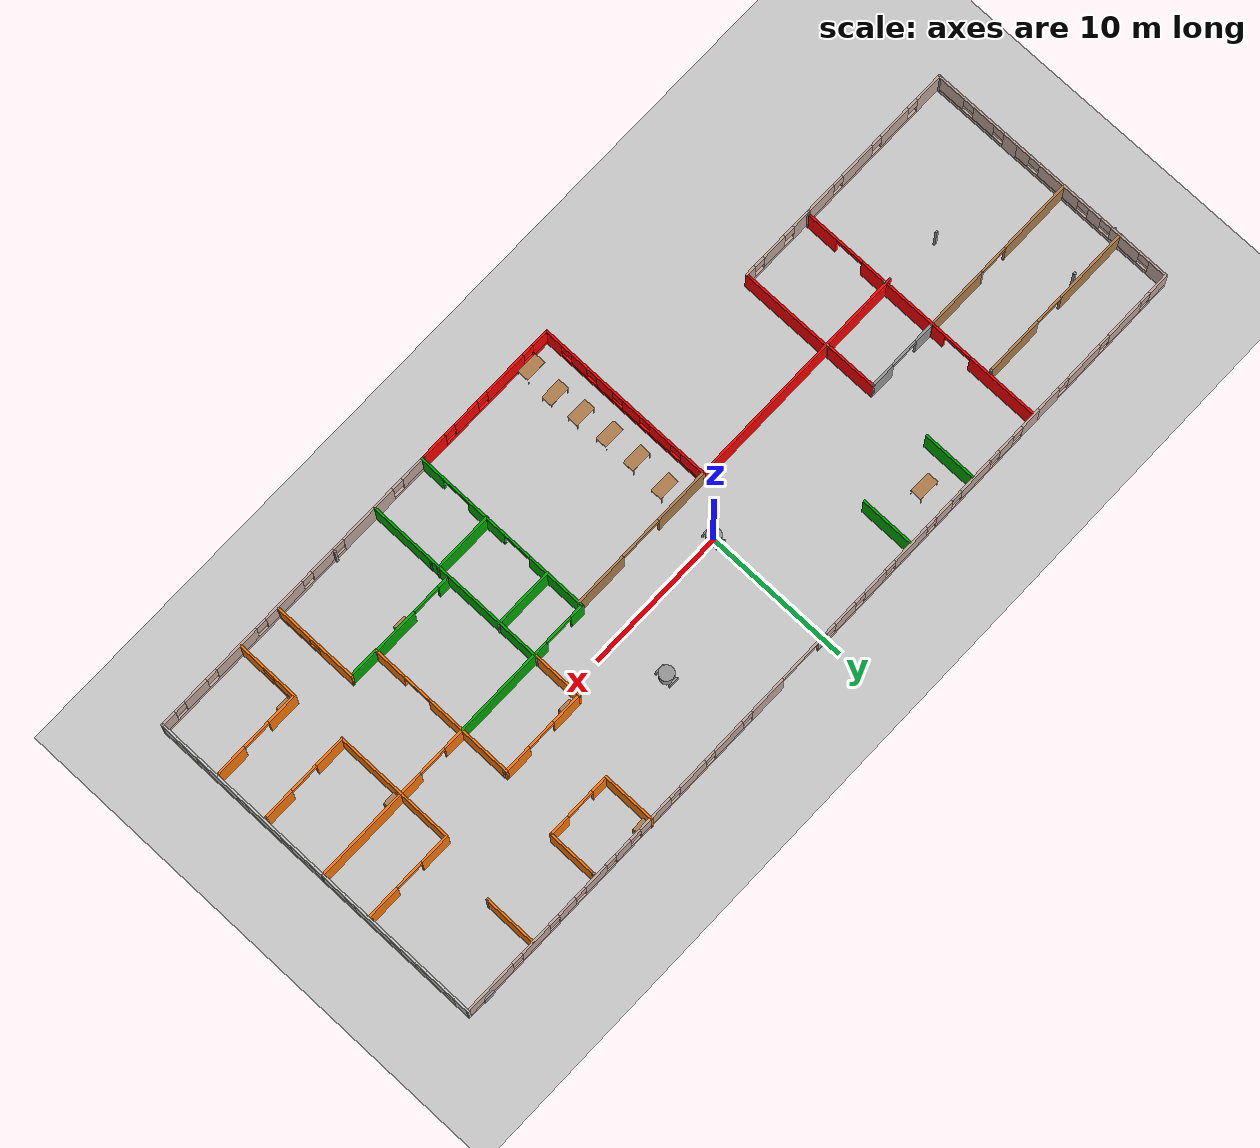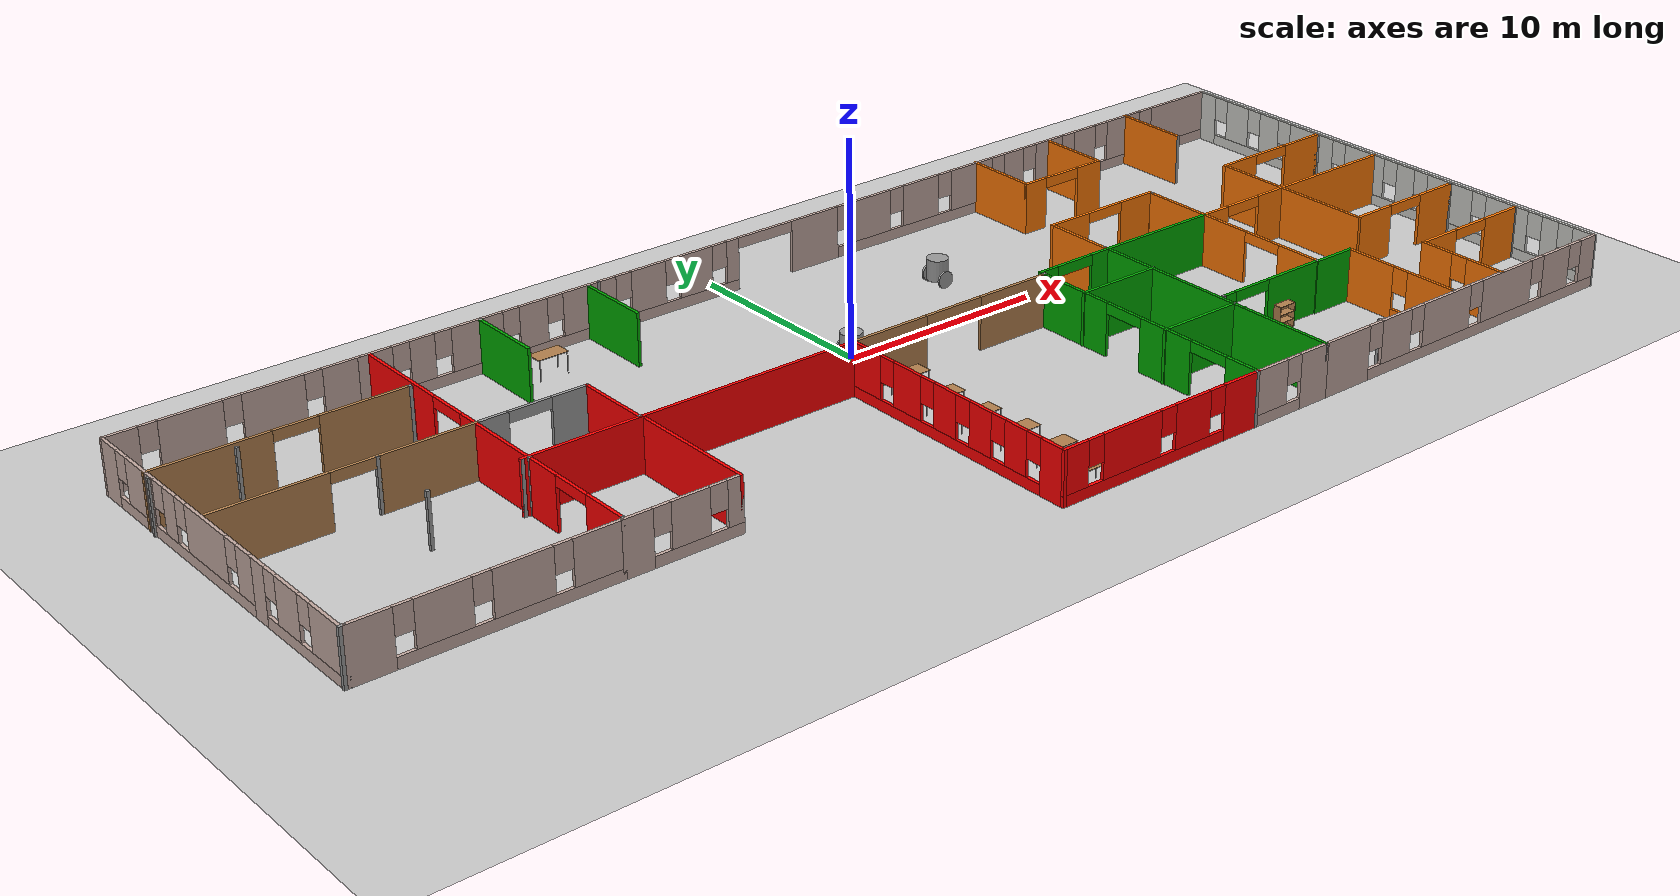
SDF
<sdf version="1.6">
 <world name="default">
  <plugin name="welcome_message" filename="libwelcome_message.so"/>
  <light name="sun" type="directional">
   <pose>0 0 10 0 -0 0</pose>
   <diffuse>0.8 0.8 0.8 1</diffuse>
   <specular>0.2 0.2 0.2 1</specular>
   <attenuation>
    <range>1000</range>
    <constant>0.9</constant>
    <linear>0.01</linear>
    <quadratic>0.001</quadratic>
   </attenuation>
   <direction>-0.5 0.1 -0.9</direction>
  </light>
  <model name="ground_plane">
   <static>1</static>
   <link name="link">
    <collision name="collision">
     <geometry><plane><normal>0 0 1</normal><size>100 100</size></plane></geometry>
     <surface><friction><ode><mu>100</mu><mu2>50</mu2></ode></friction></surface>
    </collision>
    <visual name="visual">
     <cast_shadows>0</cast_shadows>
     <geometry><plane><normal>0 0 1</normal><size>100 100</size></plane></geometry>
     <material>
      <script><uri>file://media/materials/scripts/gazebo.material</uri><name>Gazebo/Grey</name></script>
     </material>
    </visual>
   </link>
  </model>
  <gravity>0 0 -9.8</gravity>
  <magnetic_field>6e-06 2.3e-05 -4.2e-05</magnetic_field>
  <atmosphere type="adiabatic"/>
  <physics name="default_physics" default="0" type="ode">
   <max_step_size>0.001</max_step_size>
   <real_time_factor>1</real_time_factor>
   <real_time_update_rate>1000</real_time_update_rate>
  </physics>
  <scene><ambient>0.4 0.4 0.4 1</ambient><background>0.7 0.7 0.7 1</background><shadows>1</shadows></scene>
  <spherical_coordinates>
   <surface_model>EARTH_WGS84</surface_model>
   <latitude_deg>0</latitude_deg>
   <longitude_deg>0</longitude_deg>
   <elevation>0</elevation>
   <heading_deg>0</heading_deg>
  </spherical_coordinates>
  <model name="robot">
   <link name="link_1">
    <inertial>
     <mass>1</mass>
     <inertia><ixx>0.145833</ixx><ixy>0</ixy><ixz>0</ixz><iyy>0.145833</iyy><iyz>0</iyz><izz>0.125</izz></inertia>
    </inertial>
    <visual name="visual">
     <pose>0 0 0.4 0 -0 0</pose>
     <geometry><cylinder><radius>0.5</radius><length>1</length></cylinder></geometry>
     <material>
      <lighting>1</lighting>
      <script><uri>file://media/materials/scripts/gazebo.material</uri><name>Gazebo/Grey</name></script>
      <shader type="pixel"><normal_map>__default__</normal_map></shader>
      <ambient>0.3 0.3 0.3 1</ambient>
      <diffuse>0.7 0.7 0.7 1</diffuse>
      <specular>0.01 0.01 0.01 1</specular>
      <emissive>0 0 0 1</emissive>
     </material>
    </visual>
    <collision name="collision">
     <pose>0 0 0.4 0 -0 0</pose>
     <geometry><cylinder><radius>0.5</radius><length>1</length></cylinder></geometry>
     <surface>
      <friction>
       <ode><mu>1</mu><mu2>1</mu2><fdir1>0 0 0</fdir1><slip1>0</slip1><slip2>0</slip2></ode>
       <torsional>
        <coefficient>1</coefficient>
        <patch_radius>0</patch_radius>
        <surface_radius>0</surface_radius>
        <use_patch_radius>1</use_patch_radius>
        <ode><slip>0</slip></ode>
       </torsional>
      </friction>
      <bounce><restitution_coefficient>0</restitution_coefficient><threshold>1e+06</threshold></bounce>
      <contact>
       <collide_without_contact>0</collide_without_contact>
       <collide_without_contact_bitmask>1</collide_without_contact_bitmask>
       <collide_bitmask>1</collide_bitmask>
       <ode>
        <soft_cfm>0</soft_cfm>
        <soft_erp>0.2</soft_erp>
        <kp>1e+13</kp>
        <kd>1</kd>
        <max_vel>0.01</max_vel>
        <min_depth>0</min_depth>
       </ode>
       <bullet>
        <split_impulse>1</split_impulse>
        <split_impulse_penetration_threshold>-0.01</split_impulse_penetration_threshold>
        <soft_cfm>0</soft_cfm>
        <soft_erp>0.2</soft_erp>
        <kp>1e+13</kp>
        <kd>1</kd>
       </bullet>
      </contact>
     </surface>
    </collision>
   </link>
   <link name="link_1_clone">
    <inertial>
     <mass>1</mass>
     <inertia><ixx>0.145833</ixx><ixy>0</ixy><ixz>0</ixz><iyy>0.145833</iyy><iyz>0</iyz><izz>0.125</izz></inertia>
    </inertial>
    <pose>0 -0.550039 0 1.5707 -0 0</pose>
    <visual name="visual">
     <geometry><cylinder><radius>0.4</radius><length>0.1</length></cylinder></geometry>
     <material>
      <lighting>1</lighting>
      <script><uri>file://media/materials/scripts/gazebo.material</uri><name>Gazebo/Grey</name></script>
      <shader type="pixel"><normal_map>__default__</normal_map></shader>
      <ambient>0.3 0.3 0.3 1</ambient>
      <diffuse>0.7 0.7 0.7 1</diffuse>
      <specular>0.01 0.01 0.01 1</specular>
      <emissive>0 0 0 1</emissive>
     </material>
    </visual>
    <collision name="collision">
     <geometry><cylinder><radius>0.4</radius><length>0.1</length></cylinder></geometry>
     <surface>
      <friction>
       <ode><mu>1</mu><mu2>1</mu2><fdir1>0 0 0</fdir1><slip1>0</slip1><slip2>0</slip2></ode>
       <torsional>
        <coefficient>1</coefficient>
        <patch_radius>0</patch_radius>
        <surface_radius>0</surface_radius>
        <use_patch_radius>1</use_patch_radius>
        <ode><slip>0</slip></ode>
       </torsional>
      </friction>
      <bounce><restitution_coefficient>0</restitution_coefficient><threshold>1e+06</threshold></bounce>
      <contact>
       <collide_without_contact>0</collide_without_contact>
       <collide_without_contact_bitmask>1</collide_without_contact_bitmask>
       <collide_bitmask>1</collide_bitmask>
       <ode>
        <soft_cfm>0</soft_cfm>
        <soft_erp>0.2</soft_erp>
        <kp>1e+13</kp>
        <kd>1</kd>
        <max_vel>0.01</max_vel>
        <min_depth>0</min_depth>
       </ode>
       <bullet>
        <split_impulse>1</split_impulse>
        <split_impulse_penetration_threshold>-0.01</split_impulse_penetration_threshold>
        <soft_cfm>0</soft_cfm>
        <soft_erp>0.2</soft_erp>
        <kp>1e+13</kp>
        <kd>1</kd>
       </bullet>
      </contact>
     </surface>
    </collision>
   </link>
   <link name="link_1_clone_clone">
    <inertial>
     <mass>1</mass>
     <inertia><ixx>0.145833</ixx><ixy>0</ixy><ixz>0</ixz><iyy>0.145833</iyy><iyz>0</iyz><izz>0.125</izz></inertia>
    </inertial>
    <pose>0 0.550039 0 1.5707 -0 0</pose>
    <visual name="visual">
     <geometry><cylinder><radius>0.4</radius><length>0.1</length></cylinder></geometry>
     <material>
      <lighting>1</lighting>
      <script><uri>file://media/materials/scripts/gazebo.material</uri><name>Gazebo/Grey</name></script>
      <shader type="pixel"><normal_map>__default__</normal_map></shader>
      <ambient>0.3 0.3 0.3 1</ambient>
      <diffuse>0.7 0.7 0.7 1</diffuse>
      <specular>0.01 0.01 0.01 1</specular>
      <emissive>0 0 0 1</emissive>
     </material>
    </visual>
    <collision name="collision">
     <geometry><cylinder><radius>0.4</radius><length>0.1</length></cylinder></geometry>
     <surface>
      <friction>
       <ode><mu>1</mu><mu2>1</mu2><fdir1>0 0 0</fdir1><slip1>0</slip1><slip2>0</slip2></ode>
       <torsional>
        <coefficient>1</coefficient>
        <patch_radius>0</patch_radius>
        <surface_radius>0</surface_radius>
        <use_patch_radius>1</use_patch_radius>
        <ode><slip>0</slip></ode>
       </torsional>
      </friction>
      <bounce><restitution_coefficient>0</restitution_coefficient><threshold>1e+06</threshold></bounce>
      <contact>
       <collide_without_contact>0</collide_without_contact>
       <collide_without_contact_bitmask>1</collide_without_contact_bitmask>
       <collide_bitmask>1</collide_bitmask>
       <ode>
        <soft_cfm>0</soft_cfm>
        <soft_erp>0.2</soft_erp>
        <kp>1e+13</kp>
        <kd>1</kd>
        <max_vel>0.01</max_vel>
        <min_depth>0</min_depth>
       </ode>
       <bullet>
        <split_impulse>1</split_impulse>
        <split_impulse_penetration_threshold>-0.01</split_impulse_penetration_threshold>
        <soft_cfm>0</soft_cfm>
        <soft_erp>0.2</soft_erp>
        <kp>1e+13</kp>
        <kd>1</kd>
       </bullet>
      </contact>
     </surface>
    </collision>
   </link>
   <joint name="link_1_JOINT_2" type="revolute">
    <parent>link_1</parent>
    <child>link_1_clone</child>
    <axis>
     <xyz>0 0 1</xyz>
     <use_parent_model_frame>0</use_parent_model_frame>
     <limit>
      <lower>-1.79769e+308</lower>
      <upper>1.79769e+308</upper>
      <effort>-1</effort>
      <velocity>-1</velocity>
     </limit>
     <dynamics>
      <spring_reference>0</spring_reference>
      <spring_stiffness>0</spring_stiffness>
      <damping>0</damping>
     </dynamics>
    </axis>
    <physics>
     <ode><limit><cfm>0</cfm><erp>0.2</erp></limit><suspension><cfm>0</cfm><erp>0.2</erp></suspension></ode>
    </physics>
   </joint>
   <joint name="link_1_JOINT_4" type="revolute">
    <parent>link_1</parent>
    <child>link_1_clone_clone</child>
    <axis>
     <xyz>0 0 1</xyz>
     <use_parent_model_frame>0</use_parent_model_frame>
     <limit>
      <lower>-1.79769e+308</lower>
      <upper>1.79769e+308</upper>
      <effort>-1</effort>
      <velocity>-1</velocity>
     </limit>
     <dynamics>
      <spring_reference>0</spring_reference>
      <spring_stiffness>0</spring_stiffness>
      <damping>0</damping>
     </dynamics>
    </axis>
    <physics>
     <ode><limit><cfm>0</cfm><erp>0.2</erp></limit><suspension><cfm>0</cfm><erp>0.2</erp></suspension></ode>
    </physics>
   </joint>
   <static>0</static>
   <pose>0 0 0.4 0 -0 0</pose>
  </model>
  <model name="robot_clone">
   <link name="link_1">
    <inertial>
     <mass>1</mass>
     <inertia><ixx>0.145833</ixx><ixy>0</ixy><ixz>0</ixz><iyy>0.145833</iyy><iyz>0</iyz><izz>0.125</izz></inertia>
    </inertial>
    <visual name="visual">
     <pose>0 0 0.4 0 -0 0</pose>
     <geometry><cylinder><radius>0.5</radius><length>1</length></cylinder></geometry>
     <material>
      <lighting>1</lighting>
      <script><uri>file://media/materials/scripts/gazebo.material</uri><name>Gazebo/Grey</name></script>
      <shader type="pixel"><normal_map>__default__</normal_map></shader>
      <ambient>0.3 0.3 0.3 1</ambient>
      <diffuse>0.7 0.7 0.7 1</diffuse>
      <specular>0.01 0.01 0.01 1</specular>
      <emissive>0 0 0 1</emissive>
     </material>
    </visual>
    <collision name="collision">
     <pose>0 0 0.4 0 -0 0</pose>
     <geometry><cylinder><radius>0.5</radius><length>1</length></cylinder></geometry>
     <surface>
      <friction>
       <ode><mu>1</mu><mu2>1</mu2><fdir1>0 0 0</fdir1><slip1>0</slip1><slip2>0</slip2></ode>
       <torsional>
        <coefficient>1</coefficient>
        <patch_radius>0</patch_radius>
        <surface_radius>0</surface_radius>
        <use_patch_radius>1</use_patch_radius>
        <ode><slip>0</slip></ode>
       </torsional>
      </friction>
      <bounce><restitution_coefficient>0</restitution_coefficient><threshold>1e+06</threshold></bounce>
      <contact>
       <collide_without_contact>0</collide_without_contact>
       <collide_without_contact_bitmask>1</collide_without_contact_bitmask>
       <collide_bitmask>1</collide_bitmask>
       <ode>
        <soft_cfm>0</soft_cfm>
        <soft_erp>0.2</soft_erp>
        <kp>1e+13</kp>
        <kd>1</kd>
        <max_vel>0.01</max_vel>
        <min_depth>0</min_depth>
       </ode>
       <bullet>
        <split_impulse>1</split_impulse>
        <split_impulse_penetration_threshold>-0.01</split_impulse_penetration_threshold>
        <soft_cfm>0</soft_cfm>
        <soft_erp>0.2</soft_erp>
        <kp>1e+13</kp>
        <kd>1</kd>
       </bullet>
      </contact>
     </surface>
    </collision>
   </link>
   <link name="link_1_clone">
    <inertial>
     <mass>1</mass>
     <inertia><ixx>0.145833</ixx><ixy>0</ixy><ixz>0</ixz><iyy>0.145833</iyy><iyz>0</iyz><izz>0.125</izz></inertia>
    </inertial>
    <pose>0 -0.550039 0 1.5707 -0 0</pose>
    <visual name="visual">
     <geometry><cylinder><radius>0.4</radius><length>0.1</length></cylinder></geometry>
     <material>
      <lighting>1</lighting>
      <script><uri>file://media/materials/scripts/gazebo.material</uri><name>Gazebo/Grey</name></script>
      <shader type="pixel"><normal_map>__default__</normal_map></shader>
      <ambient>0.3 0.3 0.3 1</ambient>
      <diffuse>0.7 0.7 0.7 1</diffuse>
      <specular>0.01 0.01 0.01 1</specular>
      <emissive>0 0 0 1</emissive>
     </material>
    </visual>
    <collision name="collision">
     <geometry><cylinder><radius>0.4</radius><length>0.1</length></cylinder></geometry>
     <surface>
      <friction>
       <ode><mu>1</mu><mu2>1</mu2><fdir1>0 0 0</fdir1><slip1>0</slip1><slip2>0</slip2></ode>
       <torsional>
        <coefficient>1</coefficient>
        <patch_radius>0</patch_radius>
        <surface_radius>0</surface_radius>
        <use_patch_radius>1</use_patch_radius>
        <ode><slip>0</slip></ode>
       </torsional>
      </friction>
      <bounce><restitution_coefficient>0</restitution_coefficient><threshold>1e+06</threshold></bounce>
      <contact>
       <collide_without_contact>0</collide_without_contact>
       <collide_without_contact_bitmask>1</collide_without_contact_bitmask>
       <collide_bitmask>1</collide_bitmask>
       <ode>
        <soft_cfm>0</soft_cfm>
        <soft_erp>0.2</soft_erp>
        <kp>1e+13</kp>
        <kd>1</kd>
        <max_vel>0.01</max_vel>
        <min_depth>0</min_depth>
       </ode>
       <bullet>
        <split_impulse>1</split_impulse>
        <split_impulse_penetration_threshold>-0.01</split_impulse_penetration_threshold>
        <soft_cfm>0</soft_cfm>
        <soft_erp>0.2</soft_erp>
        <kp>1e+13</kp>
        <kd>1</kd>
       </bullet>
      </contact>
     </surface>
    </collision>
   </link>
   <link name="link_1_clone_clone">
    <inertial>
     <mass>1</mass>
     <inertia><ixx>0.145833</ixx><ixy>0</ixy><ixz>0</ixz><iyy>0.145833</iyy><iyz>0</iyz><izz>0.125</izz></inertia>
    </inertial>
    <pose>0 0.550039 0 1.5707 -0 0</pose>
    <visual name="visual">
     <geometry><cylinder><radius>0.4</radius><length>0.1</length></cylinder></geometry>
     <material>
      <lighting>1</lighting>
      <script><uri>file://media/materials/scripts/gazebo.material</uri><name>Gazebo/Grey</name></script>
      <shader type="pixel"><normal_map>__default__</normal_map></shader>
      <ambient>0.3 0.3 0.3 1</ambient>
      <diffuse>0.7 0.7 0.7 1</diffuse>
      <specular>0.01 0.01 0.01 1</specular>
      <emissive>0 0 0 1</emissive>
     </material>
    </visual>
    <collision name="collision">
     <geometry><cylinder><radius>0.4</radius><length>0.1</length></cylinder></geometry>
     <surface>
      <friction>
       <ode><mu>1</mu><mu2>1</mu2><fdir1>0 0 0</fdir1><slip1>0</slip1><slip2>0</slip2></ode>
       <torsional>
        <coefficient>1</coefficient>
        <patch_radius>0</patch_radius>
        <surface_radius>0</surface_radius>
        <use_patch_radius>1</use_patch_radius>
        <ode><slip>0</slip></ode>
       </torsional>
      </friction>
      <bounce><restitution_coefficient>0</restitution_coefficient><threshold>1e+06</threshold></bounce>
      <contact>
       <collide_without_contact>0</collide_without_contact>
       <collide_without_contact_bitmask>1</collide_without_contact_bitmask>
       <collide_bitmask>1</collide_bitmask>
       <ode>
        <soft_cfm>0</soft_cfm>
        <soft_erp>0.2</soft_erp>
        <kp>1e+13</kp>
        <kd>1</kd>
        <max_vel>0.01</max_vel>
        <min_depth>0</min_depth>
       </ode>
       <bullet>
        <split_impulse>1</split_impulse>
        <split_impulse_penetration_threshold>-0.01</split_impulse_penetration_threshold>
        <soft_cfm>0</soft_cfm>
        <soft_erp>0.2</soft_erp>
        <kp>1e+13</kp>
        <kd>1</kd>
       </bullet>
      </contact>
     </surface>
    </collision>
   </link>
   <joint name="link_1_JOINT_2" type="revolute">
    <parent>link_1</parent>
    <child>link_1_clone</child>
    <axis>
     <xyz>0 0 1</xyz>
     <use_parent_model_frame>0</use_parent_model_frame>
     <limit>
      <lower>-1.79769e+308</lower>
      <upper>1.79769e+308</upper>
      <effort>-1</effort>
      <velocity>-1</velocity>
     </limit>
     <dynamics>
      <spring_reference>0</spring_reference>
      <spring_stiffness>0</spring_stiffness>
      <damping>0</damping>
     </dynamics>
    </axis>
    <physics>
     <ode><limit><cfm>0</cfm><erp>0.2</erp></limit><suspension><cfm>0</cfm><erp>0.2</erp></suspension></ode>
    </physics>
   </joint>
   <joint name="link_1_JOINT_4" type="revolute">
    <parent>link_1</parent>
    <child>link_1_clone_clone</child>
    <axis>
     <xyz>0 0 1</xyz>
     <use_parent_model_frame>0</use_parent_model_frame>
     <limit>
      <lower>-1.79769e+308</lower>
      <upper>1.79769e+308</upper>
      <effort>-1</effort>
      <velocity>-1</velocity>
     </limit>
     <dynamics>
      <spring_reference>0</spring_reference>
      <spring_stiffness>0</spring_stiffness>
      <damping>0</damping>
     </dynamics>
    </axis>
    <physics>
     <ode><limit><cfm>0</cfm><erp>0.2</erp></limit><suspension><cfm>0</cfm><erp>0.2</erp></suspension></ode>
    </physics>
   </joint>
   <static>0</static>
   <pose>7.91244 3.62277 0.4 0 -0 0</pose>
  </model>
  <model name="FloorPlan">
   <pose>0.309467 -3.19534 0 0 -0 0</pose>
   <link name="Wall_0">
    <pose>5.59242 12.1499 0 0 -0 7e-06</pose>
    <visual name="Wall_0_Visual_0">
     <pose>-23.5744 0 1.25 0 -0 0</pose>
     <geometry><box><size>1.60129 0.15 2.5</size></box></geometry>
     <material>
      <script><uri>file://media/materials/scripts/gazebo.material</uri><name>Gazebo/Grey</name></script>
      <ambient>0.760784 0.662745 0.627451 1</ambient>
     </material>
     <meta><layer>0</layer></meta>
    </visual>
    <collision name="Wall_0_Collision_0">
     <geometry><box><size>1.60129 0.15 2.5</size></box></geometry>
     <pose>-23.5744 0 1.25 0 -0 0</pose>
    </collision>
    <visual name="Wall_0_Visual_1">
     <pose>-0.824166 0 1.25 0 -0 0</pose>
     <geometry><box><size>2.64767 0.15 2.5</size></box></geometry>
     <material>
      <script><uri>file://media/materials/scripts/gazebo.material</uri><name>Gazebo/Grey</name></script>
      <ambient>0.760784 0.662745 0.627451 1</ambient>
     </material>
     <meta><layer>0</layer></meta>
    </visual>
    <collision name="Wall_0_Collision_1">
     <geometry><box><size>2.64767 0.15 2.5</size></box></geometry>
     <pose>-0.824166 0 1.25 0 -0 0</pose>
    </collision>
    <visual name="Wall_0_Visual_2">
     <pose>-13.9609 0 0.25 0 -0 0</pose>
     <geometry><box><size>17.6257 0.15 0.5</size></box></geometry>
     <material>
      <script><uri>file://media/materials/scripts/gazebo.material</uri><name>Gazebo/Grey</name></script>
      <ambient>0.760784 0.662745 0.627451 1</ambient>
     </material>
     <meta><layer>0</layer></meta>
    </visual>
    <collision name="Wall_0_Collision_2">
     <geometry><box><size>17.6257 0.15 0.5</size></box></geometry>
     <pose>-13.9609 0 0.25 0 -0 0</pose>
    </collision>
    <visual name="Wall_0_Visual_3">
     <pose>12.4373 0 0.25 0 -0 0</pose>
     <geometry><box><size>23.8753 0.15 0.5</size></box></geometry>
     <material>
      <script><uri>file://media/materials/scripts/gazebo.material</uri><name>Gazebo/Grey</name></script>
      <ambient>0.760784 0.662745 0.627451 1</ambient>
     </material>
     <meta><layer>0</layer></meta>
    </visual>
    <collision name="Wall_0_Collision_3">
     <geometry><box><size>23.8753 0.15 0.5</size></box></geometry>
     <pose>12.4373 0 0.25 0 -0 0</pose>
    </collision>
    <visual name="Wall_0_Visual_4">
     <pose>-21.3839 0 1.5 0 -0 0</pose>
     <geometry><box><size>1.17957 0.15 2</size></box></geometry>
     <material>
      <script><uri>file://media/materials/scripts/gazebo.material</uri><name>Gazebo/Grey</name></script>
      <ambient>0.760784 0.662745 0.627451 1</ambient>
     </material>
     <meta><layer>0</layer></meta>
    </visual>
    <collision name="Wall_0_Collision_4">
     <geometry><box><size>1.17957 0.15 2</size></box></geometry>
     <pose>-21.3839 0 1.5 0 -0 0</pose>
    </collision>
    <visual name="Wall_0_Visual_5">
     <pose>-18.7356 0 1.5 0 -0 0</pose>
     <geometry><box><size>2.51713 0.15 2</size></box></geometry>
     <material>
      <script><uri>file://media/materials/scripts/gazebo.material</uri><name>Gazebo/Grey</name></script>
      <ambient>0.760784 0.662745 0.627451 1</ambient>
     </material>
     <meta><layer>0</layer></meta>
    </visual>
    <collision name="Wall_0_Collision_5">
     <geometry><box><size>2.51713 0.15 2</size></box></geometry>
     <pose>-18.7356 0 1.5 0 -0 0</pose>
    </collision>
    <visual name="Wall_0_Visual_6">
     <pose>-15.9802 0 1.5 0 -0 0</pose>
     <geometry><box><size>1.39358 0.15 2</size></box></geometry>
     <material>
      <script><uri>file://media/materials/scripts/gazebo.material</uri><name>Gazebo/Grey</name></script>
      <ambient>0.760784 0.662745 0.627451 1</ambient>
     </material>
     <meta><layer>0</layer></meta>
    </visual>
    <collision name="Wall_0_Collision_6">
     <geometry><box><size>1.39358 0.15 2</size></box></geometry>
     <pose>-15.9802 0 1.5 0 -0 0</pose>
    </collision>
    <visual name="Wall_0_Visual_7">
     <pose>-13.1179 0 1.5 0 -0 0</pose>
     <geometry><box><size>2.73113 0.15 2</size></box></geometry>
     <material>
      <script><uri>file://media/materials/scripts/gazebo.material</uri><name>Gazebo/Grey</name></script>
      <ambient>0.760784 0.662745 0.627451 1</ambient>
     </material>
     <meta><layer>0</layer></meta>
    </visual>
    <collision name="Wall_0_Collision_7">
     <geometry><box><size>2.73113 0.15 2</size></box></geometry>
     <pose>-13.1179 0 1.5 0 -0 0</pose>
    </collision>
    <visual name="Wall_0_Visual_8">
     <pose>-10.0415 0 1.5 0 -0 0</pose>
     <geometry><box><size>1.8216 0.15 2</size></box></geometry>
     <material>
      <script><uri>file://media/materials/scripts/gazebo.material</uri><name>Gazebo/Grey</name></script>
      <ambient>0.760784 0.662745 0.627451 1</ambient>
     </material>
     <meta><layer>0</layer></meta>
    </visual>
    <collision name="Wall_0_Collision_8">
     <geometry><box><size>1.8216 0.15 2</size></box></geometry>
     <pose>-10.0415 0 1.5 0 -0 0</pose>
    </collision>
    <visual name="Wall_0_Visual_9">
     <pose>-7.4734 0 1.5 0 -0 0</pose>
     <geometry><box><size>1.7146 0.15 2</size></box></geometry>
     <material>
      <script><uri>file://media/materials/scripts/gazebo.material</uri><name>Gazebo/Grey</name></script>
      <ambient>0.760784 0.662745 0.627451 1</ambient>
     </material>
     <meta><layer>0</layer></meta>
    </visual>
    <collision name="Wall_0_Collision_9">
     <geometry><box><size>1.7146 0.15 2</size></box></geometry>
     <pose>-7.4734 0 1.5 0 -0 0</pose>
    </collision>
    <visual name="Wall_0_Visual_10">
     <pose>-5.48205 0 1.5 0 -0 0</pose>
     <geometry><box><size>0.668097 0.15 2</size></box></geometry>
     <material>
      <script><uri>file://media/materials/scripts/gazebo.material</uri><name>Gazebo/Grey</name></script>
      <ambient>0.760784 0.662745 0.627451 1</ambient>
     </material>
     <meta><layer>0</layer></meta>
    </visual>
    <collision name="Wall_0_Collision_10">
     <geometry><box><size>0.668097 0.15 2</size></box></geometry>
     <pose>-5.48205 0 1.5 0 -0 0</pose>
    </collision>
    <visual name="Wall_0_Visual_11">
     <pose>-5.48205 0 1.5 0 -0 0</pose>
     <geometry><box><size>0.668097 0.15 2</size></box></geometry>
     <material>
      <script><uri>file://media/materials/scripts/gazebo.material</uri><name>Gazebo/Grey</name></script>
      <ambient>0.760784 0.662745 0.627451 1</ambient>
     </material>
     <meta><layer>0</layer></meta>
    </visual>
    <collision name="Wall_0_Collision_11">
     <geometry><box><size>0.668097 0.15 2</size></box></geometry>
     <pose>-5.48205 0 1.5 0 -0 0</pose>
    </collision>
    <visual name="Wall_0_Visual_12">
     <pose>2.47798 0 1.5 0 -0 0</pose>
     <geometry><box><size>2.35662 0.15 2</size></box></geometry>
     <material>
      <script><uri>file://media/materials/scripts/gazebo.material</uri><name>Gazebo/Grey</name></script>
      <ambient>0.760784 0.662745 0.627451 1</ambient>
     </material>
     <meta><layer>0</layer></meta>
    </visual>
    <collision name="Wall_0_Collision_12">
     <geometry><box><size>2.35662 0.15 2</size></box></geometry>
     <pose>2.47798 0 1.5 0 -0 0</pose>
    </collision>
    <visual name="Wall_0_Visual_13">
     <pose>5.5276 0 1.5 0 -0 0</pose>
     <geometry><box><size>2.14261 0.15 2</size></box></geometry>
     <material>
      <script><uri>file://media/materials/scripts/gazebo.material</uri><name>Gazebo/Grey</name></script>
      <ambient>0.760784 0.662745 0.627451 1</ambient>
     </material>
     <meta><layer>0</layer></meta>
    </visual>
    <collision name="Wall_0_Collision_13">
     <geometry><box><size>2.14261 0.15 2</size></box></geometry>
     <pose>5.5276 0 1.5 0 -0 0</pose>
    </collision>
    <visual name="Wall_0_Visual_14">
     <pose>8.68422 0 1.5 0 -0 0</pose>
     <geometry><box><size>2.57063 0.15 2</size></box></geometry>
     <material>
      <script><uri>file://media/materials/scripts/gazebo.material</uri><name>Gazebo/Grey</name></script>
      <ambient>0.760784 0.662745 0.627451 1</ambient>
     </material>
     <meta><layer>0</layer></meta>
    </visual>
    <collision name="Wall_0_Collision_14">
     <geometry><box><size>2.57063 0.15 2</size></box></geometry>
     <pose>8.68422 0 1.5 0 -0 0</pose>
    </collision>
    <visual name="Wall_0_Visual_15">
     <pose>11.3861 0 1.5 0 -0 0</pose>
     <geometry><box><size>1.23308 0.15 2</size></box></geometry>
     <material>
      <script><uri>file://media/materials/scripts/gazebo.material</uri><name>Gazebo/Grey</name></script>
      <ambient>0.760784 0.662745 0.627451 1</ambient>
     </material>
     <meta><layer>0</layer></meta>
    </visual>
    <collision name="Wall_0_Collision_15">
     <geometry><box><size>1.23308 0.15 2</size></box></geometry>
     <pose>11.3861 0 1.5 0 -0 0</pose>
    </collision>
    <visual name="Wall_0_Visual_16">
     <pose>13.6867 0 1.5 0 -0 0</pose>
     <geometry><box><size>1.7681 0.15 2</size></box></geometry>
     <material>
      <script><uri>file://media/materials/scripts/gazebo.material</uri><name>Gazebo/Grey</name></script>
      <ambient>0.760784 0.662745 0.627451 1</ambient>
     </material>
     <meta><layer>0</layer></meta>
    </visual>
    <collision name="Wall_0_Collision_16">
     <geometry><box><size>1.7681 0.15 2</size></box></geometry>
     <pose>13.6867 0 1.5 0 -0 0</pose>
    </collision>
    <visual name="Wall_0_Visual_17">
     <pose>16.0675 0 1.5 0 -0 0</pose>
     <geometry><box><size>1.39358 0.15 2</size></box></geometry>
     <material>
      <script><uri>file://media/materials/scripts/gazebo.material</uri><name>Gazebo/Grey</name></script>
      <ambient>0.760784 0.662745 0.627451 1</ambient>
     </material>
     <meta><layer>0</layer></meta>
    </visual>
    <collision name="Wall_0_Collision_17">
     <geometry><box><size>1.39358 0.15 2</size></box></geometry>
     <pose>16.0675 0 1.5 0 -0 0</pose>
    </collision>
    <visual name="Wall_0_Visual_18">
     <pose>18.6891 0 1.5 0 -0 0</pose>
     <geometry><box><size>2.24962 0.15 2</size></box></geometry>
     <material>
      <script><uri>file://media/materials/scripts/gazebo.material</uri><name>Gazebo/Grey</name></script>
      <ambient>0.760784 0.662745 0.627451 1</ambient>
     </material>
     <meta><layer>0</layer></meta>
    </visual>
    <collision name="Wall_0_Collision_18">
     <geometry><box><size>2.24962 0.15 2</size></box></geometry>
     <pose>18.6891 0 1.5 0 -0 0</pose>
    </collision>
    <visual name="Wall_0_Visual_19">
     <pose>22.4945 0 1.5 0 -0 0</pose>
     <geometry><box><size>3.7611 0.15 2</size></box></geometry>
     <material>
      <script><uri>file://media/materials/scripts/gazebo.material</uri><name>Gazebo/Grey</name></script>
      <ambient>0.760784 0.662745 0.627451 1</ambient>
     </material>
     <meta><layer>0</layer></meta>
    </visual>
    <collision name="Wall_0_Collision_19">
     <geometry><box><size>3.7611 0.15 2</size></box></geometry>
     <pose>22.4945 0 1.5 0 -0 0</pose>
    </collision>
    <visual name="Wall_0_Visual_20">
     <pose>-22.3737 0 1.9 0 -0 0</pose>
     <geometry><box><size>0.8 0.15 1.2</size></box></geometry>
     <material>
      <script><uri>file://media/materials/scripts/gazebo.material</uri><name>Gazebo/Grey</name></script>
      <ambient>0.760784 0.662745 0.627451 1</ambient>
     </material>
     <meta><layer>0</layer></meta>
    </visual>
    <collision name="Wall_0_Collision_20">
     <geometry><box><size>0.8 0.15 1.2</size></box></geometry>
     <pose>-22.3737 0 1.9 0 -0 0</pose>
    </collision>
    <visual name="Wall_0_Visual_21">
     <pose>0.89967 0 1.9 0 -0 0</pose>
     <geometry><box><size>0.8 0.15 1.2</size></box></geometry>
     <material>
      <script><uri>file://media/materials/scripts/gazebo.material</uri><name>Gazebo/Grey</name></script>
      <ambient>0.760784 0.662745 0.627451 1</ambient>
     </material>
     <meta><layer>0</layer></meta>
    </visual>
    <collision name="Wall_0_Collision_21">
     <geometry><box><size>0.8 0.15 1.2</size></box></geometry>
     <pose>0.89967 0 1.9 0 -0 0</pose>
    </collision>
    <visual name="Wall_0_Visual_22">
     <pose>-20.3941 0 1.9 0 -0 0</pose>
     <geometry><box><size>0.8 0.15 1.2</size></box></geometry>
     <material>
      <script><uri>file://media/materials/scripts/gazebo.material</uri><name>Gazebo/Grey</name></script>
      <ambient>0.760784 0.662745 0.627451 1</ambient>
     </material>
     <meta><layer>0</layer></meta>
    </visual>
    <collision name="Wall_0_Collision_22">
     <geometry><box><size>0.8 0.15 1.2</size></box></geometry>
     <pose>-20.3941 0 1.9 0 -0 0</pose>
    </collision>
    <visual name="Wall_0_Visual_23">
     <pose>-17.077 0 1.9 0 -0 0</pose>
     <geometry><box><size>0.8 0.15 1.2</size></box></geometry>
     <material>
      <script><uri>file://media/materials/scripts/gazebo.material</uri><name>Gazebo/Grey</name></script>
      <ambient>0.760784 0.662745 0.627451 1</ambient>
     </material>
     <meta><layer>0</layer></meta>
    </visual>
    <collision name="Wall_0_Collision_23">
     <geometry><box><size>0.8 0.15 1.2</size></box></geometry>
     <pose>-17.077 0 1.9 0 -0 0</pose>
    </collision>
    <visual name="Wall_0_Visual_24">
     <pose>-14.8834 0 1.9 0 -0 0</pose>
     <geometry><box><size>0.8 0.15 1.2</size></box></geometry>
     <material>
      <script><uri>file://media/materials/scripts/gazebo.material</uri><name>Gazebo/Grey</name></script>
      <ambient>0.760784 0.662745 0.627451 1</ambient>
     </material>
     <meta><layer>0</layer></meta>
    </visual>
    <collision name="Wall_0_Collision_24">
     <geometry><box><size>0.8 0.15 1.2</size></box></geometry>
     <pose>-14.8834 0 1.9 0 -0 0</pose>
    </collision>
    <visual name="Wall_0_Visual_25">
     <pose>-11.3523 0 1.9 0 -0 0</pose>
     <geometry><box><size>0.8 0.15 1.2</size></box></geometry>
     <material>
      <script><uri>file://media/materials/scripts/gazebo.material</uri><name>Gazebo/Grey</name></script>
      <ambient>0.760784 0.662745 0.627451 1</ambient>
     </material>
     <meta><layer>0</layer></meta>
    </visual>
    <collision name="Wall_0_Collision_25">
     <geometry><box><size>0.8 0.15 1.2</size></box></geometry>
     <pose>-11.3523 0 1.9 0 -0 0</pose>
    </collision>
    <visual name="Wall_0_Visual_26">
     <pose>-8.7307 0 1.9 0 -0 0</pose>
     <geometry><box><size>0.8 0.15 1.2</size></box></geometry>
     <material>
      <script><uri>file://media/materials/scripts/gazebo.material</uri><name>Gazebo/Grey</name></script>
      <ambient>0.760784 0.662745 0.627451 1</ambient>
     </material>
     <meta><layer>0</layer></meta>
    </visual>
    <collision name="Wall_0_Collision_26">
     <geometry><box><size>0.8 0.15 1.2</size></box></geometry>
     <pose>-8.7307 0 1.9 0 -0 0</pose>
    </collision>
    <visual name="Wall_0_Visual_27">
     <pose>-6.2161 0 1.9 0 -0 0</pose>
     <geometry><box><size>0.8 0.15 1.2</size></box></geometry>
     <material>
      <script><uri>file://media/materials/scripts/gazebo.material</uri><name>Gazebo/Grey</name></script>
      <ambient>0.760784 0.662745 0.627451 1</ambient>
     </material>
     <meta><layer>0</layer></meta>
    </visual>
    <collision name="Wall_0_Collision_27">
     <geometry><box><size>0.8 0.15 1.2</size></box></geometry>
     <pose>-6.2161 0 1.9 0 -0 0</pose>
    </collision>
    <visual name="Wall_0_Visual_28">
     <pose>4.05629 0 1.9 0 -0 0</pose>
     <geometry><box><size>0.8 0.15 1.2</size></box></geometry>
     <material>
      <script><uri>file://media/materials/scripts/gazebo.material</uri><name>Gazebo/Grey</name></script>
      <ambient>0.760784 0.662745 0.627451 1</ambient>
     </material>
     <meta><layer>0</layer></meta>
    </visual>
    <collision name="Wall_0_Collision_28">
     <geometry><box><size>0.8 0.15 1.2</size></box></geometry>
     <pose>4.05629 0 1.9 0 -0 0</pose>
    </collision>
    <visual name="Wall_0_Visual_29">
     <pose>6.9989 0 1.9 0 -0 0</pose>
     <geometry><box><size>0.8 0.15 1.2</size></box></geometry>
     <material>
      <script><uri>file://media/materials/scripts/gazebo.material</uri><name>Gazebo/Grey</name></script>
      <ambient>0.760784 0.662745 0.627451 1</ambient>
     </material>
     <meta><layer>0</layer></meta>
    </visual>
    <collision name="Wall_0_Collision_29">
     <geometry><box><size>0.8 0.15 1.2</size></box></geometry>
     <pose>6.9989 0 1.9 0 -0 0</pose>
    </collision>
    <visual name="Wall_0_Visual_30">
     <pose>10.3695 0 1.9 0 -0 0</pose>
     <geometry><box><size>0.8 0.15 1.2</size></box></geometry>
     <material>
      <script><uri>file://media/materials/scripts/gazebo.material</uri><name>Gazebo/Grey</name></script>
      <ambient>0.760784 0.662745 0.627451 1</ambient>
     </material>
     <meta><layer>0</layer></meta>
    </visual>
    <collision name="Wall_0_Collision_30">
     <geometry><box><size>0.8 0.15 1.2</size></box></geometry>
     <pose>10.3695 0 1.9 0 -0 0</pose>
    </collision>
    <visual name="Wall_0_Visual_31">
     <pose>12.4026 0 1.9 0 -0 0</pose>
     <geometry><box><size>0.8 0.15 1.2</size></box></geometry>
     <material>
      <script><uri>file://media/materials/scripts/gazebo.material</uri><name>Gazebo/Grey</name></script>
      <ambient>0.760784 0.662745 0.627451 1</ambient>
     </material>
     <meta><layer>0</layer></meta>
    </visual>
    <collision name="Wall_0_Collision_31">
     <geometry><box><size>0.8 0.15 1.2</size></box></geometry>
     <pose>12.4026 0 1.9 0 -0 0</pose>
    </collision>
    <visual name="Wall_0_Visual_32">
     <pose>14.9707 0 1.9 0 -0 0</pose>
     <geometry><box><size>0.8 0.15 1.2</size></box></geometry>
     <material>
      <script><uri>file://media/materials/scripts/gazebo.material</uri><name>Gazebo/Grey</name></script>
      <ambient>0.760784 0.662745 0.627451 1</ambient>
     </material>
     <meta><layer>0</layer></meta>
    </visual>
    <collision name="Wall_0_Collision_32">
     <geometry><box><size>0.8 0.15 1.2</size></box></geometry>
     <pose>14.9707 0 1.9 0 -0 0</pose>
    </collision>
    <visual name="Wall_0_Visual_33">
     <pose>17.1643 0 1.9 0 -0 0</pose>
     <geometry><box><size>0.8 0.15 1.2</size></box></geometry>
     <material>
      <script><uri>file://media/materials/scripts/gazebo.material</uri><name>Gazebo/Grey</name></script>
      <ambient>0.760784 0.662745 0.627451 1</ambient>
     </material>
     <meta><layer>0</layer></meta>
    </visual>
    <collision name="Wall_0_Collision_33">
     <geometry><box><size>0.8 0.15 1.2</size></box></geometry>
     <pose>17.1643 0 1.9 0 -0 0</pose>
    </collision>
    <visual name="Wall_0_Visual_34">
     <pose>20.2139 0 1.9 0 -0 0</pose>
     <geometry><box><size>0.8 0.15 1.2</size></box></geometry>
     <material>
      <script><uri>file://media/materials/scripts/gazebo.material</uri><name>Gazebo/Grey</name></script>
      <ambient>0.760784 0.662745 0.627451 1</ambient>
     </material>
     <meta><layer>0</layer></meta>
    </visual>
    <collision name="Wall_0_Collision_34">
     <geometry><box><size>0.8 0.15 1.2</size></box></geometry>
     <pose>20.2139 0 1.9 0 -0 0</pose>
    </collision>
    <visual name="Wall_0_Visual_35">
     <pose>-3.648 0 2.25 0 -0 0</pose>
     <geometry><box><size>3 0.15 0.5</size></box></geometry>
     <material>
      <script><uri>file://media/materials/scripts/gazebo.material</uri><name>Gazebo/Grey</name></script>
      <ambient>0.760784 0.662745 0.627451 1</ambient>
     </material>
     <meta><layer>0</layer></meta>
    </visual>
    <collision name="Wall_0_Collision_35">
     <geometry><box><size>3 0.15 0.5</size></box></geometry>
     <pose>-3.648 0 2.25 0 -0 0</pose>
    </collision>
    <visual name="Wall_0_Visual_36">
     <pose>-3.648 0 2.25 0 -0 0</pose>
     <geometry><box><size>3 0.15 0.5</size></box></geometry>
     <material>
      <script><uri>file://media/materials/scripts/gazebo.material</uri><name>Gazebo/Grey</name></script>
      <ambient>0.760784 0.662745 0.627451 1</ambient>
     </material>
     <meta><layer>0</layer></meta>
    </visual>
    <collision name="Wall_0_Collision_36">
     <geometry><box><size>3 0.15 0.5</size></box></geometry>
     <pose>-3.648 0 2.25 0 -0 0</pose>
    </collision>
   </link>
   <link name="Wall_1">
    <pose>29.8922 -0.024899 0 0 -0 -1.5708</pose>
    <visual name="Wall_1_Visual_0">
     <pose>-11.6902 0 1.25 0 -0 0</pose>
     <geometry><box><size>1.11957 0.15 2.5</size></box></geometry>
     <material>
      <script><uri>file://media/materials/scripts/gazebo.material</uri><name>Gazebo/CeilingTiled</name></script>
      <ambient>0.760784 0.662745 0.627451 1</ambient>
     </material>
     <meta><layer>0</layer></meta>
    </visual>
    <collision name="Wall_1_Collision_0">
     <geometry><box><size>1.11957 0.15 2.5</size></box></geometry>
     <pose>-11.6902 0 1.25 0 -0 0</pose>
    </collision>
    <visual name="Wall_1_Visual_1">
     <pose>0.559784 0 0.25 0 -0 0</pose>
     <geometry><box><size>23.3804 0.15 0.5</size></box></geometry>
     <material>
      <script><uri>file://media/materials/scripts/gazebo.material</uri><name>Gazebo/CeilingTiled</name></script>
      <ambient>0.760784 0.662745 0.627451 1</ambient>
     </material>
     <meta><layer>0</layer></meta>
    </visual>
    <collision name="Wall_1_Collision_1">
     <geometry><box><size>23.3804 0.15 0.5</size></box></geometry>
     <pose>0.559784 0 0.25 0 -0 0</pose>
    </collision>
    <visual name="Wall_1_Visual_2">
     <pose>-9.60688 0 1.5 0 -0 0</pose>
     <geometry><box><size>1.44711 0.15 2</size></box></geometry>
     <material>
      <script><uri>file://media/materials/scripts/gazebo.material</uri><name>Gazebo/CeilingTiled</name></script>
      <ambient>0.760784 0.662745 0.627451 1</ambient>
     </material>
     <meta><layer>0</layer></meta>
    </visual>
    <collision name="Wall_1_Collision_2">
     <geometry><box><size>1.44711 0.15 2</size></box></geometry>
     <pose>-9.60688 0 1.5 0 -0 0</pose>
    </collision>
    <visual name="Wall_1_Visual_3">
     <pose>-7.46678 0 1.5 0 -0 0</pose>
     <geometry><box><size>1.2331 0.15 2</size></box></geometry>
     <material>
      <script><uri>file://media/materials/scripts/gazebo.material</uri><name>Gazebo/CeilingTiled</name></script>
      <ambient>0.760784 0.662745 0.627451 1</ambient>
     </material>
     <meta><layer>0</layer></meta>
    </visual>
    <collision name="Wall_1_Collision_3">
     <geometry><box><size>1.2331 0.15 2</size></box></geometry>
     <pose>-7.46678 0 1.5 0 -0 0</pose>
    </collision>
    <visual name="Wall_1_Visual_4">
     <pose>-4.6579 0 1.5 0 -0 0</pose>
     <geometry><box><size>2.78467 0.15 2</size></box></geometry>
     <material>
      <script><uri>file://media/materials/scripts/gazebo.material</uri><name>Gazebo/CeilingTiled</name></script>
      <ambient>0.760784 0.662745 0.627451 1</ambient>
     </material>
     <meta><layer>0</layer></meta>
    </visual>
    <collision name="Wall_1_Collision_4">
     <geometry><box><size>2.78467 0.15 2</size></box></geometry>
     <pose>-4.6579 0 1.5 0 -0 0</pose>
    </collision>
    <visual name="Wall_1_Visual_5">
     <pose>-1.23374 0 1.5 0 -0 0</pose>
     <geometry><box><size>2.46365 0.15 2</size></box></geometry>
     <material>
      <script><uri>file://media/materials/scripts/gazebo.material</uri><name>Gazebo/CeilingTiled</name></script>
      <ambient>0.760784 0.662745 0.627451 1</ambient>
     </material>
     <meta><layer>0</layer></meta>
    </visual>
    <collision name="Wall_1_Collision_5">
     <geometry><box><size>2.46365 0.15 2</size></box></geometry>
     <pose>-1.23374 0 1.5 0 -0 0</pose>
    </collision>
    <visual name="Wall_1_Visual_6">
     <pose>1.33438 0 1.5 0 -0 0</pose>
     <geometry><box><size>1.07259 0.15 2</size></box></geometry>
     <material>
      <script><uri>file://media/materials/scripts/gazebo.material</uri><name>Gazebo/CeilingTiled</name></script>
      <ambient>0.760784 0.662745 0.627451 1</ambient>
     </material>
     <meta><layer>0</layer></meta>
    </visual>
    <collision name="Wall_1_Collision_6">
     <geometry><box><size>1.07259 0.15 2</size></box></geometry>
     <pose>1.33438 0 1.5 0 -0 0</pose>
    </collision>
    <visual name="Wall_1_Visual_7">
     <pose>4.00951 0 1.5 0 -0 0</pose>
     <geometry><box><size>2.67766 0.15 2</size></box></geometry>
     <material>
      <script><uri>file://media/materials/scripts/gazebo.material</uri><name>Gazebo/CeilingTiled</name></script>
      <ambient>0.760784 0.662745 0.627451 1</ambient>
     </material>
     <meta><layer>0</layer></meta>
    </visual>
    <collision name="Wall_1_Collision_7">
     <geometry><box><size>2.67766 0.15 2</size></box></geometry>
     <pose>4.00951 0 1.5 0 -0 0</pose>
    </collision>
    <visual name="Wall_1_Visual_8">
     <pose>7.35341 0 1.5 0 -0 0</pose>
     <geometry><box><size>2.41015 0.15 2</size></box></geometry>
     <material>
      <script><uri>file://media/materials/scripts/gazebo.material</uri><name>Gazebo/CeilingTiled</name></script>
      <ambient>0.760784 0.662745 0.627451 1</ambient>
     </material>
     <meta><layer>0</layer></meta>
    </visual>
    <collision name="Wall_1_Collision_8">
     <geometry><box><size>2.41015 0.15 2</size></box></geometry>
     <pose>7.35341 0 1.5 0 -0 0</pose>
    </collision>
    <visual name="Wall_1_Visual_9">
     <pose>9.81453 0 1.5 0 -0 0</pose>
     <geometry><box><size>0.91208 0.15 2</size></box></geometry>
     <material>
      <script><uri>file://media/materials/scripts/gazebo.material</uri><name>Gazebo/CeilingTiled</name></script>
      <ambient>0.760784 0.662745 0.627451 1</ambient>
     </material>
     <meta><layer>0</layer></meta>
    </visual>
    <collision name="Wall_1_Collision_9">
     <geometry><box><size>0.91208 0.15 2</size></box></geometry>
     <pose>9.81453 0 1.5 0 -0 0</pose>
    </collision>
    <visual name="Wall_1_Visual_10">
     <pose>11.6603 0 1.5 0 -0 0</pose>
     <geometry><box><size>1.17943 0.15 2</size></box></geometry>
     <material>
      <script><uri>file://media/materials/scripts/gazebo.material</uri><name>Gazebo/CeilingTiled</name></script>
      <ambient>0.760784 0.662745 0.627451 1</ambient>
     </material>
     <meta><layer>0</layer></meta>
    </visual>
    <collision name="Wall_1_Collision_10">
     <geometry><box><size>1.17943 0.15 2</size></box></geometry>
     <pose>11.6603 0 1.5 0 -0 0</pose>
    </collision>
    <visual name="Wall_1_Visual_11">
     <pose>-10.7304 0 1.9 0 -0 0</pose>
     <geometry><box><size>0.8 0.15 1.2</size></box></geometry>
     <material>
      <script><uri>file://media/materials/scripts/gazebo.material</uri><name>Gazebo/CeilingTiled</name></script>
      <ambient>0.760784 0.662745 0.627451 1</ambient>
     </material>
     <meta><layer>0</layer></meta>
    </visual>
    <collision name="Wall_1_Collision_11">
     <geometry><box><size>0.8 0.15 1.2</size></box></geometry>
     <pose>-10.7304 0 1.9 0 -0 0</pose>
    </collision>
    <visual name="Wall_1_Visual_12">
     <pose>-8.48333 0 1.9 0 -0 0</pose>
     <geometry><box><size>0.8 0.15 1.2</size></box></geometry>
     <material>
      <script><uri>file://media/materials/scripts/gazebo.material</uri><name>Gazebo/CeilingTiled</name></script>
      <ambient>0.760784 0.662745 0.627451 1</ambient>
     </material>
     <meta><layer>0</layer></meta>
    </visual>
    <collision name="Wall_1_Collision_12">
     <geometry><box><size>0.8 0.15 1.2</size></box></geometry>
     <pose>-8.48333 0 1.9 0 -0 0</pose>
    </collision>
    <visual name="Wall_1_Visual_13">
     <pose>-6.45023 0 1.9 0 -0 0</pose>
     <geometry><box><size>0.8 0.15 1.2</size></box></geometry>
     <material>
      <script><uri>file://media/materials/scripts/gazebo.material</uri><name>Gazebo/CeilingTiled</name></script>
      <ambient>0.760784 0.662745 0.627451 1</ambient>
     </material>
     <meta><layer>0</layer></meta>
    </visual>
    <collision name="Wall_1_Collision_13">
     <geometry><box><size>0.8 0.15 1.2</size></box></geometry>
     <pose>-6.45023 0 1.9 0 -0 0</pose>
    </collision>
    <visual name="Wall_1_Visual_14">
     <pose>-2.86557 0 1.9 0 -0 0</pose>
     <geometry><box><size>0.8 0.15 1.2</size></box></geometry>
     <material>
      <script><uri>file://media/materials/scripts/gazebo.material</uri><name>Gazebo/CeilingTiled</name></script>
      <ambient>0.760784 0.662745 0.627451 1</ambient>
     </material>
     <meta><layer>0</layer></meta>
    </visual>
    <collision name="Wall_1_Collision_14">
     <geometry><box><size>0.8 0.15 1.2</size></box></geometry>
     <pose>-2.86557 0 1.9 0 -0 0</pose>
    </collision>
    <visual name="Wall_1_Visual_15">
     <pose>0.398088 0 1.9 0 -0 0</pose>
     <geometry><box><size>0.8 0.15 1.2</size></box></geometry>
     <material>
      <script><uri>file://media/materials/scripts/gazebo.material</uri><name>Gazebo/CeilingTiled</name></script>
      <ambient>0.760784 0.662745 0.627451 1</ambient>
     </material>
     <meta><layer>0</layer></meta>
    </visual>
    <collision name="Wall_1_Collision_15">
     <geometry><box><size>0.8 0.15 1.2</size></box></geometry>
     <pose>0.398088 0 1.9 0 -0 0</pose>
    </collision>
    <visual name="Wall_1_Visual_16">
     <pose>2.27068 0 1.9 0 -0 0</pose>
     <geometry><box><size>0.8 0.15 1.2</size></box></geometry>
     <material>
      <script><uri>file://media/materials/scripts/gazebo.material</uri><name>Gazebo/CeilingTiled</name></script>
      <ambient>0.760784 0.662745 0.627451 1</ambient>
     </material>
     <meta><layer>0</layer></meta>
    </visual>
    <collision name="Wall_1_Collision_16">
     <geometry><box><size>0.8 0.15 1.2</size></box></geometry>
     <pose>2.27068 0 1.9 0 -0 0</pose>
    </collision>
    <visual name="Wall_1_Visual_17">
     <pose>5.74834 0 1.9 0 -0 0</pose>
     <geometry><box><size>0.8 0.15 1.2</size></box></geometry>
     <material>
      <script><uri>file://media/materials/scripts/gazebo.material</uri><name>Gazebo/CeilingTiled</name></script>
      <ambient>0.760784 0.662745 0.627451 1</ambient>
     </material>
     <meta><layer>0</layer></meta>
    </visual>
    <collision name="Wall_1_Collision_17">
     <geometry><box><size>0.8 0.15 1.2</size></box></geometry>
     <pose>5.74834 0 1.9 0 -0 0</pose>
    </collision>
    <visual name="Wall_1_Visual_18">
     <pose>8.95849 0 1.9 0 -0 0</pose>
     <geometry><box><size>0.8 0.15 1.2</size></box></geometry>
     <material>
      <script><uri>file://media/materials/scripts/gazebo.material</uri><name>Gazebo/CeilingTiled</name></script>
      <ambient>0.760784 0.662745 0.627451 1</ambient>
     </material>
     <meta><layer>0</layer></meta>
    </visual>
    <collision name="Wall_1_Collision_18">
     <geometry><box><size>0.8 0.15 1.2</size></box></geometry>
     <pose>8.95849 0 1.9 0 -0 0</pose>
    </collision>
    <visual name="Wall_1_Visual_19">
     <pose>10.6706 0 1.9 0 -0 0</pose>
     <geometry><box><size>0.8 0.15 1.2</size></box></geometry>
     <material>
      <script><uri>file://media/materials/scripts/gazebo.material</uri><name>Gazebo/CeilingTiled</name></script>
      <ambient>0.760784 0.662745 0.627451 1</ambient>
     </material>
     <meta><layer>0</layer></meta>
    </visual>
    <collision name="Wall_1_Collision_19">
     <geometry><box><size>0.8 0.15 1.2</size></box></geometry>
     <pose>10.6706 0 1.9 0 -0 0</pose>
    </collision>
   </link>
   <link name="Wall_101">
    <collision name="Wall_101_Collision">
     <geometry><box><size>13 0.15 2.5</size></box></geometry>
     <pose>0 0 1.25 0 -0 0</pose>
    </collision>
    <visual name="Wall_101_Visual">
     <pose>0 0 1.25 0 -0 0</pose>
     <geometry><box><size>13 0.15 2.5</size></box></geometry>
     <material>
      <script><uri>file://media/materials/scripts/gazebo.material</uri><name>Gazebo/Grey</name></script>
      <ambient>0 0.666667 0 1</ambient>
     </material>
     <meta><layer>0</layer></meta>
    </visual>
    <pose>12.2171 -5.77826 0 0 -0 -1.5708</pose>
   </link>
   <link name="Wall_102">
    <collision name="Wall_102_Collision">
     <geometry><box><size>0.15 0.15 2.5</size></box></geometry>
     <pose>0 0 1.25 0 -0 0</pose>
    </collision>
    <visual name="Wall_102_Visual">
     <pose>0 0 1.25 0 -0 0</pose>
     <geometry><box><size>0.15 0.15 2.5</size></box></geometry>
     <material>
      <script><uri>file://media/materials/scripts/gazebo.material</uri><name>Gazebo/Grey</name></script>
      <ambient>1 1 1 1</ambient>
     </material>
     <meta><layer>0</layer></meta>
    </visual>
    <pose>12.2171 -12.2033 0 0 -0 0</pose>
   </link>
   <link name="Wall_103">
    <pose>10.1671 -12.2033 0 0 -0 3.14159</pose>
    <visual name="Wall_103_Visual_0">
     <pose>-1.32445 0 1.25 0 -0 0</pose>
     <geometry><box><size>1.60109 0.15 2.5</size></box></geometry>
     <material>
      <script><uri>file://media/materials/scripts/gazebo.material</uri><name>Gazebo/Grey</name></script>
      <ambient>0.760784 0.662745 0.627451 1</ambient>
     </material>
     <meta><layer>0</layer></meta>
    </visual>
    <collision name="Wall_103_Collision_0">
     <geometry><box><size>1.60109 0.15 2.5</size></box></geometry>
     <pose>-1.32445 0 1.25 0 -0 0</pose>
    </collision>
    <visual name="Wall_103_Visual_1">
     <pose>0.800545 0 0.25 0 -0 0</pose>
     <geometry><box><size>2.64891 0.15 0.5</size></box></geometry>
     <material>
      <script><uri>file://media/materials/scripts/gazebo.material</uri><name>Gazebo/Grey</name></script>
      <ambient>0.760784 0.662745 0.627451 1</ambient>
     </material>
     <meta><layer>0</layer></meta>
    </visual>
    <collision name="Wall_103_Collision_1">
     <geometry><box><size>2.64891 0.15 0.5</size></box></geometry>
     <pose>0.800545 0 0.25 0 -0 0</pose>
    </collision>
    <visual name="Wall_103_Visual_2">
     <pose>1.20054 0 1.5 0 -0 0</pose>
     <geometry><box><size>1.84891 0.15 2</size></box></geometry>
     <material>
      <script><uri>file://media/materials/scripts/gazebo.material</uri><name>Gazebo/Grey</name></script>
      <ambient>0.760784 0.662745 0.627451 1</ambient>
     </material>
     <meta><layer>0</layer></meta>
    </visual>
    <collision name="Wall_103_Collision_2">
     <geometry><box><size>1.84891 0.15 2</size></box></geometry>
     <pose>1.20054 0 1.5 0 -0 0</pose>
    </collision>
    <visual name="Wall_103_Visual_3">
     <pose>-0.12391 0 1.9 0 -0 0</pose>
     <geometry><box><size>0.8 0.15 1.2</size></box></geometry>
     <material>
      <script><uri>file://media/materials/scripts/gazebo.material</uri><name>Gazebo/Grey</name></script>
      <ambient>0.760784 0.662745 0.627451 1</ambient>
     </material>
     <meta><layer>0</layer></meta>
    </visual>
    <collision name="Wall_103_Collision_3">
     <geometry><box><size>0.8 0.15 1.2</size></box></geometry>
     <pose>-0.12391 0 1.9 0 -0 0</pose>
    </collision>
   </link>
   <link name="Wall_104">
    <collision name="Wall_104_Collision">
     <geometry><box><size>0.16 0.15 2.5</size></box></geometry>
     <pose>0 0 1.25 0 -0 0</pose>
    </collision>
    <visual name="Wall_104_Visual">
     <pose>0 0 1.25 0 -0 0</pose>
     <geometry><box><size>0.16 0.15 2.5</size></box></geometry>
     <material>
      <script><uri>file://media/materials/scripts/gazebo.material</uri><name>Gazebo/Grey</name></script>
      <ambient>1 1 1 1</ambient>
     </material>
     <meta><layer>0</layer></meta>
    </visual>
    <pose>8.12208 -12.2033 0 0 -0 0</pose>
   </link>
   <link name="Wall_106">
    <pose>2.89263 0.399775 0 0 -0 0</pose>
    <visual name="Wall_106_Visual_0">
     <pose>-3.40324 0 1.25 0 -0 0</pose>
     <geometry><box><size>3.94351 0.15 2.5</size></box></geometry>
     <material>
      <script><uri>file://media/materials/scripts/gazebo.material</uri><name>Gazebo/Wood</name></script>
      <ambient>1 1 1 1</ambient>
     </material>
     <meta><layer>0</layer></meta>
    </visual>
    <collision name="Wall_106_Collision_0">
     <geometry><box><size>3.94351 0.15 2.5</size></box></geometry>
     <pose>-3.40324 0 1.25 0 -0 0</pose>
    </collision>
    <visual name="Wall_106_Visual_1">
     <pose>3.47176 0 1.25 0 -0 0</pose>
     <geometry><box><size>3.80649 0.15 2.5</size></box></geometry>
     <material>
      <script><uri>file://media/materials/scripts/gazebo.material</uri><name>Gazebo/Wood</name></script>
      <ambient>1 1 1 1</ambient>
     </material>
     <meta><layer>0</layer></meta>
    </visual>
    <collision name="Wall_106_Collision_1">
     <geometry><box><size>3.80649 0.15 2.5</size></box></geometry>
     <pose>3.47176 0 1.25 0 -0 0</pose>
    </collision>
    <visual name="Wall_106_Visual_2">
     <pose>0.068513 0 2.25 0 -0 0</pose>
     <geometry><box><size>3 0.15 0.5</size></box></geometry>
     <material>
      <script><uri>file://media/materials/scripts/gazebo.material</uri><name>Gazebo/Wood</name></script>
      <ambient>1 1 1 1</ambient>
     </material>
     <meta><layer>0</layer></meta>
    </visual>
    <collision name="Wall_106_Collision_2">
     <geometry><box><size>3 0.15 0.5</size></box></geometry>
     <pose>0.068513 0 2.25 0 -0 0</pose>
    </collision>
   </link>
   <link name="Wall_107">
    <collision name="Wall_107_Collision">
     <geometry><box><size>0.16 0.15 2.5</size></box></geometry>
     <pose>0 0 1.25 0 -0 0</pose>
    </collision>
    <visual name="Wall_107_Visual">
     <pose>0 0 1.25 0 -0 0</pose>
     <geometry><box><size>0.16 0.15 2.5</size></box></geometry>
     <material>
      <script><uri>file://media/materials/scripts/gazebo.material</uri><name>Gazebo/Grey</name></script>
      <ambient>1 1 1 1</ambient>
     </material>
     <meta><layer>0</layer></meta>
    </visual>
    <pose>8.19763 0.399775 0 0 -0 0</pose>
   </link>
   <link name="Wall_11">
    <pose>-18.2258 6.2811 0 0 -0 -1.5708</pose>
    <visual name="Wall_11_Visual_0">
     <pose>-3.31145 0 1.25 0 -0 0</pose>
     <geometry><box><size>4.97711 0.15 2.5</size></box></geometry>
     <material>
      <script><uri>file://media/materials/scripts/gazebo.material</uri><name>Gazebo/Grey</name></script>
      <ambient>1 0 0 1</ambient>
     </material>
     <meta><layer>0</layer></meta>
    </visual>
    <collision name="Wall_11_Collision_0">
     <geometry><box><size>4.97711 0.15 2.5</size></box></geometry>
     <pose>-3.31145 0 1.25 0 -0 0</pose>
    </collision>
    <visual name="Wall_11_Visual_1">
     <pose>3.48855 0 1.25 0 -0 0</pose>
     <geometry><box><size>4.62289 0.15 2.5</size></box></geometry>
     <material>
      <script><uri>file://media/materials/scripts/gazebo.material</uri><name>Gazebo/Grey</name></script>
      <ambient>1 0 0 1</ambient>
     </material>
     <meta><layer>0</layer></meta>
    </visual>
    <collision name="Wall_11_Collision_1">
     <geometry><box><size>4.62289 0.15 2.5</size></box></geometry>
     <pose>3.48855 0 1.25 0 -0 0</pose>
    </collision>
    <visual name="Wall_11_Visual_2">
     <pose>0.177109 0 2.25 0 -0 0</pose>
     <geometry><box><size>2 0.15 0.5</size></box></geometry>
     <material>
      <script><uri>file://media/materials/scripts/gazebo.material</uri><name>Gazebo/Grey</name></script>
      <ambient>1 0 0 1</ambient>
     </material>
     <meta><layer>0</layer></meta>
    </visual>
    <collision name="Wall_11_Collision_2">
     <geometry><box><size>2 0.15 0.5</size></box></geometry>
     <pose>0.177109 0 2.25 0 -0 0</pose>
    </collision>
   </link>
   <link name="Wall_110">
    <collision name="Wall_110_Collision">
     <geometry><box><size>0.15 0.15 2.5</size></box></geometry>
     <pose>0 0 1.25 0 -0 0</pose>
    </collision>
    <visual name="Wall_110_Visual">
     <pose>0 0 1.25 0 -0 0</pose>
     <geometry><box><size>0.15 0.15 2.5</size></box></geometry>
     <material>
      <script><uri>file://media/materials/scripts/gazebo.material</uri><name>Gazebo/Grey</name></script>
      <ambient>0 0.666667 0 1</ambient>
     </material>
     <meta><layer>0</layer></meta>
    </visual>
    <pose>12.2509 -7.59265 0 0 -0 0</pose>
   </link>
   <link name="Wall_112">
    <collision name="Wall_112_Collision">
     <geometry><box><size>4.25 0.15 2.5</size></box></geometry>
     <pose>0 0 1.25 0 -0 0</pose>
    </collision>
    <visual name="Wall_112_Visual">
     <pose>0 0 1.25 0 -0 0</pose>
     <geometry><box><size>4.25 0.15 2.5</size></box></geometry>
     <material>
      <script><uri>file://media/materials/scripts/gazebo.material</uri><name>Gazebo/Grey</name></script>
      <ambient>0 0.666667 0 1</ambient>
     </material>
     <meta><layer>0</layer></meta>
    </visual>
    <pose>10.2009 -2.13539 0 0 -0 0</pose>
   </link>
   <link name="Wall_113">
    <collision name="Wall_113_Collision">
     <geometry><box><size>0.16 0.15 2.5</size></box></geometry>
     <pose>0 0 1.25 0 -0 0</pose>
    </collision>
    <visual name="Wall_113_Visual">
     <pose>0 0 1.25 0 -0 0</pose>
     <geometry><box><size>0.16 0.15 2.5</size></box></geometry>
     <material>
      <script><uri>file://media/materials/scripts/gazebo.material</uri><name>Gazebo/Grey</name></script>
      <ambient>1 1 1 1</ambient>
     </material>
     <meta><layer>0</layer></meta>
    </visual>
    <pose>12.2559 -2.13539 0 0 -0 0</pose>
   </link>
   <link name="Wall_115">
    <collision name="Wall_115_Collision">
     <geometry><box><size>4.25 0.15 2.5</size></box></geometry>
     <pose>0 0 1.25 0 -0 0</pose>
    </collision>
    <visual name="Wall_115_Visual">
     <pose>0 0 1.25 0 -0 0</pose>
     <geometry><box><size>4.25 0.15 2.5</size></box></geometry>
     <material>
      <script><uri>file://media/materials/scripts/gazebo.material</uri><name>Gazebo/Grey</name></script>
      <ambient>0 0.666667 0 1</ambient>
     </material>
     <meta><layer>0</layer></meta>
    </visual>
    <pose>10.2009 -7.00412 0 0 -0 0</pose>
   </link>
   <link name="Wall_116">
    <collision name="Wall_116_Collision">
     <geometry><box><size>0.16 0.15 2.5</size></box></geometry>
     <pose>0 0 1.25 0 -0 0</pose>
    </collision>
    <visual name="Wall_116_Visual">
     <pose>0 0 1.25 0 -0 0</pose>
     <geometry><box><size>0.16 0.15 2.5</size></box></geometry>
     <material>
      <script><uri>file://media/materials/scripts/gazebo.material</uri><name>Gazebo/Grey</name></script>
      <ambient>1 1 1 1</ambient>
     </material>
     <meta><layer>0</layer></meta>
    </visual>
    <pose>12.2559 -7.00412 0 0 -0 0</pose>
   </link>
   <link name="Wall_117">
    <collision name="Wall_117_Collision">
     <geometry><box><size>0.16 0.15 2.5</size></box></geometry>
     <pose>0 0 1.25 0 -0 0</pose>
    </collision>
    <visual name="Wall_117_Visual">
     <pose>0 0 1.25 0 -0 0</pose>
     <geometry><box><size>0.16 0.15 2.5</size></box></geometry>
     <material>
      <script><uri>file://media/materials/scripts/gazebo.material</uri><name>Gazebo/Grey</name></script>
      <ambient>0 0.666667 0 1</ambient>
     </material>
     <meta><layer>0</layer></meta>
    </visual>
    <pose>12.2659 -7.00412 0 0 -0 0</pose>
   </link>
   <link name="Wall_123">
    <collision name="Wall_123_Collision">
     <geometry><box><size>0.15 0.15 2.5</size></box></geometry>
     <pose>0 0 1.25 0 -0 0</pose>
    </collision>
    <visual name="Wall_123_Visual">
     <pose>0 0 1.25 0 -0 0</pose>
     <geometry><box><size>0.15 0.15 2.5</size></box></geometry>
     <material>
      <script><uri>file://media/materials/scripts/gazebo.material</uri><name>Gazebo/Grey</name></script>
      <ambient>1 1 1 1</ambient>
     </material>
     <meta><layer>0</layer></meta>
    </visual>
    <pose>29.8852 4.1779 0 0 -0 0</pose>
   </link>
   <link name="Wall_128">
    <pose>24.0926 0.649775 0 0 -0 0</pose>
    <visual name="Wall_128_Visual_0">
     <pose>-5.09508 0 1.25 0 -0 0</pose>
     <geometry><box><size>1.55985 0.15 2.5</size></box></geometry>
     <material>
      <script><uri>file://media/materials/scripts/gazebo.material</uri><name>Gazebo/Grey</name></script>
      <ambient>0.996078 0.47451 0.0196078 1</ambient>
     </material>
     <meta><layer>0</layer></meta>
    </visual>
    <collision name="Wall_128_Collision_0">
     <geometry><box><size>1.55985 0.15 2.5</size></box></geometry>
     <pose>-5.09508 0 1.25 0 -0 0</pose>
    </collision>
    <visual name="Wall_128_Visual_1">
     <pose>1.77992 0 1.25 0 -0 0</pose>
     <geometry><box><size>8.19015 0.15 2.5</size></box></geometry>
     <material>
      <script><uri>file://media/materials/scripts/gazebo.material</uri><name>Gazebo/Grey</name></script>
      <ambient>0.996078 0.47451 0.0196078 1</ambient>
     </material>
     <meta><layer>0</layer></meta>
    </visual>
    <collision name="Wall_128_Collision_1">
     <geometry><box><size>8.19015 0.15 2.5</size></box></geometry>
     <pose>1.77992 0 1.25 0 -0 0</pose>
    </collision>
    <visual name="Wall_128_Visual_2">
     <pose>-3.31515 0 2.25 0 -0 0</pose>
     <geometry><box><size>2 0.15 0.5</size></box></geometry>
     <material>
      <script><uri>file://media/materials/scripts/gazebo.material</uri><name>Gazebo/Grey</name></script>
      <ambient>0.996078 0.47451 0.0196078 1</ambient>
     </material>
     <meta><layer>0</layer></meta>
    </visual>
    <collision name="Wall_128_Collision_2">
     <geometry><box><size>2 0.15 0.5</size></box></geometry>
     <pose>-3.31515 0 2.25 0 -0 0</pose>
    </collision>
   </link>
   <link name="Wall_129">
    <collision name="Wall_129_Collision">
     <geometry><box><size>0.15 0.15 2.5</size></box></geometry>
     <pose>0 0 1.25 0 -0 0</pose>
    </collision>
    <visual name="Wall_129_Visual">
     <pose>0 0 1.25 0 -0 0</pose>
     <geometry><box><size>0.15 0.15 2.5</size></box></geometry>
     <material>
      <script><uri>file://media/materials/scripts/gazebo.material</uri><name>Gazebo/Grey</name></script>
      <ambient>1 1 1 1</ambient>
     </material>
     <meta><layer>0</layer></meta>
    </visual>
    <pose>29.8926 0.649775 0 0 -0 0</pose>
   </link>
   <link name="Wall_13">
    <pose>-24.2574 12.1498 0 0 -0 3.14159</pose>
    <visual name="Wall_13_Visual_0">
     <pose>-4.7442 0 1.25 0 -0 0</pose>
     <geometry><box><size>1.7616 0.15 2.5</size></box></geometry>
     <material>
      <script><uri>file://media/materials/scripts/gazebo.material</uri><name>Gazebo/Grey</name></script>
      <ambient>0.760784 0.662745 0.627451 1</ambient>
     </material>
     <meta><layer>0</layer></meta>
    </visual>
    <collision name="Wall_13_Collision_0">
     <geometry><box><size>1.7616 0.15 2.5</size></box></geometry>
     <pose>-4.7442 0 1.25 0 -0 0</pose>
    </collision>
    <visual name="Wall_13_Visual_1">
     <pose>0.880798 0 0.25 0 -0 0</pose>
     <geometry><box><size>9.4884 0.15 0.5</size></box></geometry>
     <material>
      <script><uri>file://media/materials/scripts/gazebo.material</uri><name>Gazebo/Grey</name></script>
      <ambient>0.760784 0.662745 0.627451 1</ambient>
     </material>
     <meta><layer>0</layer></meta>
    </visual>
    <collision name="Wall_13_Collision_1">
     <geometry><box><size>9.4884 0.15 0.5</size></box></geometry>
     <pose>0.880798 0 0.25 0 -0 0</pose>
    </collision>
    <visual name="Wall_13_Visual_2">
     <pose>-1.67107 0 1.5 0 -0 0</pose>
     <geometry><box><size>2.78467 0.15 2</size></box></geometry>
     <material>
      <script><uri>file://media/materials/scripts/gazebo.material</uri><name>Gazebo/Grey</name></script>
      <ambient>0.760784 0.662745 0.627451 1</ambient>
     </material>
     <meta><layer>0</layer></meta>
    </visual>
    <collision name="Wall_13_Collision_2">
     <geometry><box><size>2.78467 0.15 2</size></box></geometry>
     <pose>-1.67107 0 1.5 0 -0 0</pose>
    </collision>
    <visual name="Wall_13_Visual_3">
     <pose>1.9136 0 1.5 0 -0 0</pose>
     <geometry><box><size>2.78467 0.15 2</size></box></geometry>
     <material>
      <script><uri>file://media/materials/scripts/gazebo.material</uri><name>Gazebo/Grey</name></script>
      <ambient>0.760784 0.662745 0.627451 1</ambient>
     </material>
     <meta><layer>0</layer></meta>
    </visual>
    <collision name="Wall_13_Collision_3">
     <geometry><box><size>2.78467 0.15 2</size></box></geometry>
     <pose>1.9136 0 1.5 0 -0 0</pose>
    </collision>
    <visual name="Wall_13_Visual_4">
     <pose>4.86547 0 1.5 0 -0 0</pose>
     <geometry><box><size>1.51907 0.15 2</size></box></geometry>
     <material>
      <script><uri>file://media/materials/scripts/gazebo.material</uri><name>Gazebo/Grey</name></script>
      <ambient>0.760784 0.662745 0.627451 1</ambient>
     </material>
     <meta><layer>0</layer></meta>
    </visual>
    <collision name="Wall_13_Collision_4">
     <geometry><box><size>1.51907 0.15 2</size></box></geometry>
     <pose>4.86547 0 1.5 0 -0 0</pose>
    </collision>
    <visual name="Wall_13_Visual_5">
     <pose>-3.4634 0 1.9 0 -0 0</pose>
     <geometry><box><size>0.8 0.15 1.2</size></box></geometry>
     <material>
      <script><uri>file://media/materials/scripts/gazebo.material</uri><name>Gazebo/Grey</name></script>
      <ambient>0.760784 0.662745 0.627451 1</ambient>
     </material>
     <meta><layer>0</layer></meta>
    </visual>
    <collision name="Wall_13_Collision_5">
     <geometry><box><size>0.8 0.15 1.2</size></box></geometry>
     <pose>-3.4634 0 1.9 0 -0 0</pose>
    </collision>
    <visual name="Wall_13_Visual_6">
     <pose>0.121265 0 1.9 0 -0 0</pose>
     <geometry><box><size>0.8 0.15 1.2</size></box></geometry>
     <material>
      <script><uri>file://media/materials/scripts/gazebo.material</uri><name>Gazebo/Grey</name></script>
      <ambient>0.760784 0.662745 0.627451 1</ambient>
     </material>
     <meta><layer>0</layer></meta>
    </visual>
    <collision name="Wall_13_Collision_6">
     <geometry><box><size>0.8 0.15 1.2</size></box></geometry>
     <pose>0.121265 0 1.9 0 -0 0</pose>
    </collision>
    <visual name="Wall_13_Visual_7">
     <pose>3.70593 0 1.9 0 -0 0</pose>
     <geometry><box><size>0.8 0.15 1.2</size></box></geometry>
     <material>
      <script><uri>file://media/materials/scripts/gazebo.material</uri><name>Gazebo/Grey</name></script>
      <ambient>0.760784 0.662745 0.627451 1</ambient>
     </material>
     <meta><layer>0</layer></meta>
    </visual>
    <collision name="Wall_13_Collision_7">
     <geometry><box><size>0.8 0.15 1.2</size></box></geometry>
     <pose>3.70593 0 1.9 0 -0 0</pose>
    </collision>
   </link>
   <link name="Wall_131">
    <collision name="Wall_131_Collision">
     <geometry><box><size>3.5 0.15 2.5</size></box></geometry>
     <pose>0 0 1.25 0 -0 0</pose>
    </collision>
    <visual name="Wall_131_Visual">
     <pose>0 0 1.25 0 -0 0</pose>
     <geometry><box><size>3.5 0.15 2.5</size></box></geometry>
     <material>
      <script><uri>file://media/materials/scripts/gazebo.material</uri><name>Gazebo/Grey</name></script>
      <ambient>0.996078 0.47451 0.0196078 1</ambient>
     </material>
     <meta><layer>0</layer></meta>
    </visual>
    <pose>18.2926 2.32477 0 0 -0 1.5708</pose>
   </link>
   <link name="Wall_132">
    <collision name="Wall_132_Collision">
     <geometry><box><size>0.16 0.15 2.5</size></box></geometry>
     <pose>0 0 1.25 0 -0 0</pose>
    </collision>
    <visual name="Wall_132_Visual">
     <pose>0 0 1.25 0 -0 0</pose>
     <geometry><box><size>0.16 0.15 2.5</size></box></geometry>
     <material>
      <script><uri>file://media/materials/scripts/gazebo.material</uri><name>Gazebo/Grey</name></script>
      <ambient>1 1 1 1</ambient>
     </material>
     <meta><layer>0</layer></meta>
    </visual>
    <pose>18.2976 3.99978 0 0 -0 0</pose>
   </link>
   <link name="Wall_134">
    <collision name="Wall_134_Collision">
     <geometry><box><size>8.5 0.15 2.5</size></box></geometry>
     <pose>0 0 1.25 0 -0 0</pose>
    </collision>
    <visual name="Wall_134_Visual">
     <pose>0 0 1.25 0 -0 0</pose>
     <geometry><box><size>8.5 0.15 2.5</size></box></geometry>
     <material>
      <script><uri>file://media/materials/scripts/gazebo.material</uri><name>Gazebo/Grey</name></script>
      <ambient>0.996078 0.47451 0.0196078 1</ambient>
     </material>
     <meta><layer>0</layer></meta>
    </visual>
    <pose>23.3991 0.109907 0 0 -0 -1.5708</pose>
   </link>
   <link name="Wall_135">
    <pose>26.5741 -4.06509 0 0 -0 0</pose>
    <visual name="Wall_135_Visual_0">
     <pose>-2.12495 0 1.25 0 -0 0</pose>
     <geometry><box><size>2.25011 0.15 2.5</size></box></geometry>
     <material>
      <script><uri>file://media/materials/scripts/gazebo.material</uri><name>Gazebo/Grey</name></script>
      <ambient>0.996078 0.47451 0.0196078 1</ambient>
     </material>
     <meta><layer>0</layer></meta>
    </visual>
    <collision name="Wall_135_Collision_0">
     <geometry><box><size>2.25011 0.15 2.5</size></box></geometry>
     <pose>-2.12495 0 1.25 0 -0 0</pose>
    </collision>
    <visual name="Wall_135_Visual_1">
     <pose>2.12505 0 1.25 0 -0 0</pose>
     <geometry><box><size>2.24989 0.15 2.5</size></box></geometry>
     <material>
      <script><uri>file://media/materials/scripts/gazebo.material</uri><name>Gazebo/Grey</name></script>
      <ambient>0.996078 0.47451 0.0196078 1</ambient>
     </material>
     <meta><layer>0</layer></meta>
    </visual>
    <collision name="Wall_135_Collision_1">
     <geometry><box><size>2.24989 0.15 2.5</size></box></geometry>
     <pose>2.12505 0 1.25 0 -0 0</pose>
    </collision>
    <visual name="Wall_135_Visual_2">
     <pose>0.000105 0 2.25 0 -0 0</pose>
     <geometry><box><size>2 0.15 0.5</size></box></geometry>
     <material>
      <script><uri>file://media/materials/scripts/gazebo.material</uri><name>Gazebo/Grey</name></script>
      <ambient>0.996078 0.47451 0.0196078 1</ambient>
     </material>
     <meta><layer>0</layer></meta>
    </visual>
    <collision name="Wall_135_Collision_2">
     <geometry><box><size>2 0.15 0.5</size></box></geometry>
     <pose>0.000105 0 2.25 0 -0 0</pose>
    </collision>
   </link>
   <link name="Wall_136">
    <collision name="Wall_136_Collision">
     <geometry><box><size>0.16 0.15 2.5</size></box></geometry>
     <pose>0 0 1.25 0 -0 0</pose>
    </collision>
    <visual name="Wall_136_Visual">
     <pose>0 0 1.25 0 -0 0</pose>
     <geometry><box><size>0.16 0.15 2.5</size></box></geometry>
     <material>
      <script><uri>file://media/materials/scripts/gazebo.material</uri><name>Gazebo/Grey</name></script>
      <ambient>1 1 1 1</ambient>
     </material>
     <meta><layer>0</layer></meta>
    </visual>
    <pose>29.7541 -4.06509 0 0 -0 0</pose>
   </link>
   <link name="Wall_14">
    <pose>-29.8074 6.22478 0 0 -0 -1.5708</pose>
    <visual name="Wall_14_Visual_0">
     <pose>-5.33321 0 1.25 0 -0 0</pose>
     <geometry><box><size>1.33358 0.15 2.5</size></box></geometry>
     <material>
      <script><uri>file://media/materials/scripts/gazebo.material</uri><name>Gazebo/Grey</name></script>
      <ambient>0.760784 0.662745 0.627451 1</ambient>
     </material>
     <meta><layer>0</layer></meta>
    </visual>
    <collision name="Wall_14_Collision_0">
     <geometry><box><size>1.33358 0.15 2.5</size></box></geometry>
     <pose>-5.33321 0 1.25 0 -0 0</pose>
    </collision>
    <visual name="Wall_14_Visual_1">
     <pose>0.666789 0 0.25 0 -0 0</pose>
     <geometry><box><size>10.6664 0.15 0.5</size></box></geometry>
     <material>
      <script><uri>file://media/materials/scripts/gazebo.material</uri><name>Gazebo/Grey</name></script>
      <ambient>0.760784 0.662745 0.627451 1</ambient>
     </material>
     <meta><layer>0</layer></meta>
    </visual>
    <collision name="Wall_14_Collision_1">
     <geometry><box><size>10.6664 0.15 0.5</size></box></geometry>
     <pose>0.666789 0 0.25 0 -0 0</pose>
    </collision>
    <visual name="Wall_14_Visual_2">
     <pose>-2.7416 0 1.5 0 -0 0</pose>
     <geometry><box><size>2.24964 0.15 2</size></box></geometry>
     <material>
      <script><uri>file://media/materials/scripts/gazebo.material</uri><name>Gazebo/Grey</name></script>
      <ambient>0.760784 0.662745 0.627451 1</ambient>
     </material>
     <meta><layer>0</layer></meta>
    </visual>
    <collision name="Wall_14_Collision_2">
     <geometry><box><size>2.24964 0.15 2</size></box></geometry>
     <pose>-2.7416 0 1.5 0 -0 0</pose>
    </collision>
    <visual name="Wall_14_Visual_3">
     <pose>-0.333988 0 1.5 0 -0 0</pose>
     <geometry><box><size>0.965583 0.15 2</size></box></geometry>
     <material>
      <script><uri>file://media/materials/scripts/gazebo.material</uri><name>Gazebo/Grey</name></script>
      <ambient>0.760784 0.662745 0.627451 1</ambient>
     </material>
     <meta><layer>0</layer></meta>
    </visual>
    <collision name="Wall_14_Collision_3">
     <geometry><box><size>0.965583 0.15 2</size></box></geometry>
     <pose>-0.333988 0 1.5 0 -0 0</pose>
    </collision>
    <visual name="Wall_14_Visual_4">
     <pose>2.50164 0 1.5 0 -0 0</pose>
     <geometry><box><size>3.10568 0.15 2</size></box></geometry>
     <material>
      <script><uri>file://media/materials/scripts/gazebo.material</uri><name>Gazebo/Grey</name></script>
      <ambient>0.760784 0.662745 0.627451 1</ambient>
     </material>
     <meta><layer>0</layer></meta>
    </visual>
    <collision name="Wall_14_Collision_4">
     <geometry><box><size>3.10568 0.15 2</size></box></geometry>
     <pose>2.50164 0 1.5 0 -0 0</pose>
    </collision>
    <visual name="Wall_14_Visual_5">
     <pose>5.42724 0 1.5 0 -0 0</pose>
     <geometry><box><size>1.14552 0.15 2</size></box></geometry>
     <material>
      <script><uri>file://media/materials/scripts/gazebo.material</uri><name>Gazebo/Grey</name></script>
      <ambient>0.760784 0.662745 0.627451 1</ambient>
     </material>
     <meta><layer>0</layer></meta>
    </visual>
    <collision name="Wall_14_Collision_5">
     <geometry><box><size>1.14552 0.15 2</size></box></geometry>
     <pose>5.42724 0 1.5 0 -0 0</pose>
    </collision>
    <visual name="Wall_14_Visual_6">
     <pose>-4.26642 0 1.9 0 -0 0</pose>
     <geometry><box><size>0.8 0.15 1.2</size></box></geometry>
     <material>
      <script><uri>file://media/materials/scripts/gazebo.material</uri><name>Gazebo/Grey</name></script>
      <ambient>0.760784 0.662745 0.627451 1</ambient>
     </material>
     <meta><layer>0</layer></meta>
    </visual>
    <collision name="Wall_14_Collision_6">
     <geometry><box><size>0.8 0.15 1.2</size></box></geometry>
     <pose>-4.26642 0 1.9 0 -0 0</pose>
    </collision>
    <visual name="Wall_14_Visual_7">
     <pose>-1.21678 0 1.9 0 -0 0</pose>
     <geometry><box><size>0.8 0.15 1.2</size></box></geometry>
     <material>
      <script><uri>file://media/materials/scripts/gazebo.material</uri><name>Gazebo/Grey</name></script>
      <ambient>0.760784 0.662745 0.627451 1</ambient>
     </material>
     <meta><layer>0</layer></meta>
    </visual>
    <collision name="Wall_14_Collision_7">
     <geometry><box><size>0.8 0.15 1.2</size></box></geometry>
     <pose>-1.21678 0 1.9 0 -0 0</pose>
    </collision>
    <visual name="Wall_14_Visual_8">
     <pose>0.548803 0 1.9 0 -0 0</pose>
     <geometry><box><size>0.8 0.15 1.2</size></box></geometry>
     <material>
      <script><uri>file://media/materials/scripts/gazebo.material</uri><name>Gazebo/Grey</name></script>
      <ambient>0.760784 0.662745 0.627451 1</ambient>
     </material>
     <meta><layer>0</layer></meta>
    </visual>
    <collision name="Wall_14_Collision_8">
     <geometry><box><size>0.8 0.15 1.2</size></box></geometry>
     <pose>0.548803 0 1.9 0 -0 0</pose>
    </collision>
    <visual name="Wall_14_Visual_9">
     <pose>4.45449 0 1.9 0 -0 0</pose>
     <geometry><box><size>0.8 0.15 1.2</size></box></geometry>
     <material>
      <script><uri>file://media/materials/scripts/gazebo.material</uri><name>Gazebo/Grey</name></script>
      <ambient>0.760784 0.662745 0.627451 1</ambient>
     </material>
     <meta><layer>0</layer></meta>
    </visual>
    <collision name="Wall_14_Collision_9">
     <geometry><box><size>0.8 0.15 1.2</size></box></geometry>
     <pose>4.45449 0 1.9 0 -0 0</pose>
    </collision>
   </link>
   <link name="Wall_141">
    <pose>23.4526 -10.0189 0 0 -0 1.5708</pose>
    <visual name="Wall_141_Visual_0">
     <pose>-1.2622 0 1.25 0 -0 0</pose>
     <geometry><box><size>1.97561 0.15 2.5</size></box></geometry>
     <material>
      <script><uri>file://media/materials/scripts/gazebo.material</uri><name>Gazebo/Grey</name></script>
      <ambient>0.996078 0.47451 0.0196078 1</ambient>
     </material>
     <meta><layer>0</layer></meta>
    </visual>
    <collision name="Wall_141_Collision_0">
     <geometry><box><size>1.97561 0.15 2.5</size></box></geometry>
     <pose>-1.2622 0 1.25 0 -0 0</pose>
    </collision>
    <visual name="Wall_141_Visual_1">
     <pose>0.987804 0 0.25 0 -0 0</pose>
     <geometry><box><size>2.52439 0.15 0.5</size></box></geometry>
     <material>
      <script><uri>file://media/materials/scripts/gazebo.material</uri><name>Gazebo/Grey</name></script>
      <ambient>0.996078 0.47451 0.0196078 1</ambient>
     </material>
     <meta><layer>0</layer></meta>
    </visual>
    <collision name="Wall_141_Collision_1">
     <geometry><box><size>2.52439 0.15 0.5</size></box></geometry>
     <pose>0.987804 0 0.25 0 -0 0</pose>
    </collision>
    <visual name="Wall_141_Visual_2">
     <pose>1.3878 0 1.5 0 -0 0</pose>
     <geometry><box><size>1.72439 0.15 2</size></box></geometry>
     <material>
      <script><uri>file://media/materials/scripts/gazebo.material</uri><name>Gazebo/Grey</name></script>
      <ambient>0.996078 0.47451 0.0196078 1</ambient>
     </material>
     <meta><layer>0</layer></meta>
    </visual>
    <collision name="Wall_141_Collision_2">
     <geometry><box><size>1.72439 0.15 2</size></box></geometry>
     <pose>1.3878 0 1.5 0 -0 0</pose>
    </collision>
    <visual name="Wall_141_Visual_3">
     <pose>0.125608 0 1.9 0 -0 0</pose>
     <geometry><box><size>0.8 0.15 1.2</size></box></geometry>
     <material>
      <script><uri>file://media/materials/scripts/gazebo.material</uri><name>Gazebo/Grey</name></script>
      <ambient>0.996078 0.47451 0.0196078 1</ambient>
     </material>
     <meta><layer>0</layer></meta>
    </visual>
    <collision name="Wall_141_Collision_3">
     <geometry><box><size>0.8 0.15 1.2</size></box></geometry>
     <pose>0.125608 0 1.9 0 -0 0</pose>
    </collision>
   </link>
   <link name="Wall_142">
    <pose>26.6276 -7.84386 0 0 -0 0</pose>
    <visual name="Wall_142_Visual_0">
     <pose>-2.13418 0 1.25 0 -0 0</pose>
     <geometry><box><size>2.23165 0.15 2.5</size></box></geometry>
     <material>
      <script><uri>file://media/materials/scripts/gazebo.material</uri><name>Gazebo/Grey</name></script>
      <ambient>0.996078 0.47451 0.0196078 1</ambient>
     </material>
     <meta><layer>0</layer></meta>
    </visual>
    <collision name="Wall_142_Collision_0">
     <geometry><box><size>2.23165 0.15 2.5</size></box></geometry>
     <pose>-2.13418 0 1.25 0 -0 0</pose>
    </collision>
    <visual name="Wall_142_Visual_1">
     <pose>2.11582 0 1.25 0 -0 0</pose>
     <geometry><box><size>2.26835 0.15 2.5</size></box></geometry>
     <material>
      <script><uri>file://media/materials/scripts/gazebo.material</uri><name>Gazebo/Grey</name></script>
      <ambient>0.996078 0.47451 0.0196078 1</ambient>
     </material>
     <meta><layer>0</layer></meta>
    </visual>
    <collision name="Wall_142_Collision_1">
     <geometry><box><size>2.26835 0.15 2.5</size></box></geometry>
     <pose>2.11582 0 1.25 0 -0 0</pose>
    </collision>
    <visual name="Wall_142_Visual_2">
     <pose>-0.018353 0 2.25 0 -0 0</pose>
     <geometry><box><size>2 0.15 0.5</size></box></geometry>
     <material>
      <script><uri>file://media/materials/scripts/gazebo.material</uri><name>Gazebo/Grey</name></script>
      <ambient>0.996078 0.47451 0.0196078 1</ambient>
     </material>
     <meta><layer>0</layer></meta>
    </visual>
    <collision name="Wall_142_Collision_2">
     <geometry><box><size>2 0.15 0.5</size></box></geometry>
     <pose>-0.018353 0 2.25 0 -0 0</pose>
    </collision>
   </link>
   <link name="Wall_143">
    <collision name="Wall_143_Collision">
     <geometry><box><size>0.15 0.15 2.5</size></box></geometry>
     <pose>0 0 1.25 0 -0 0</pose>
    </collision>
    <visual name="Wall_143_Visual">
     <pose>0 0 1.25 0 -0 0</pose>
     <geometry><box><size>0.15 0.15 2.5</size></box></geometry>
     <material>
      <script><uri>file://media/materials/scripts/gazebo.material</uri><name>Gazebo/Grey</name></script>
      <ambient>1 1 1 1</ambient>
     </material>
     <meta><layer>0</layer></meta>
    </visual>
    <pose>29.8026 -7.84386 0 0 -0 0</pose>
   </link>
   <link name="Wall_148">
    <collision name="Wall_148_Collision">
     <geometry><box><size>2.25 0.15 2.5</size></box></geometry>
     <pose>0 0 1.25 0 -0 0</pose>
    </collision>
    <visual name="Wall_148_Visual">
     <pose>0 0 1.25 0 -0 0</pose>
     <geometry><box><size>2.25 0.15 2.5</size></box></geometry>
     <material>
      <script><uri>file://media/materials/scripts/gazebo.material</uri><name>Gazebo/Grey</name></script>
      <ambient>0 0.666667 0 1</ambient>
     </material>
     <meta><layer>0</layer></meta>
    </visual>
    <pose>19.3129 -6.25509 0 0 -0 0</pose>
   </link>
   <link name="Wall_149">
    <pose>20.3629 -9.18009 0 0 -0 -1.5708</pose>
    <visual name="Wall_149_Visual_0">
     <pose>-1.69118 0 1.25 0 -0 0</pose>
     <geometry><box><size>2.61764 0.15 2.5</size></box></geometry>
     <material>
      <script><uri>file://media/materials/scripts/gazebo.material</uri><name>Gazebo/Grey</name></script>
      <ambient>0.996078 0.47451 0.0196078 1</ambient>
     </material>
     <meta><layer>0</layer></meta>
    </visual>
    <collision name="Wall_149_Collision_0">
     <geometry><box><size>2.61764 0.15 2.5</size></box></geometry>
     <pose>-1.69118 0 1.25 0 -0 0</pose>
    </collision>
    <visual name="Wall_149_Visual_1">
     <pose>1.30882 0 0.25 0 -0 0</pose>
     <geometry><box><size>3.38236 0.15 0.5</size></box></geometry>
     <material>
      <script><uri>file://media/materials/scripts/gazebo.material</uri><name>Gazebo/Grey</name></script>
      <ambient>0.996078 0.47451 0.0196078 1</ambient>
     </material>
     <meta><layer>0</layer></meta>
    </visual>
    <collision name="Wall_149_Collision_1">
     <geometry><box><size>3.38236 0.15 0.5</size></box></geometry>
     <pose>1.30882 0 0.25 0 -0 0</pose>
    </collision>
    <visual name="Wall_149_Visual_2">
     <pose>1.70882 0 1.5 0 -0 0</pose>
     <geometry><box><size>2.58236 0.15 2</size></box></geometry>
     <material>
      <script><uri>file://media/materials/scripts/gazebo.material</uri><name>Gazebo/Grey</name></script>
      <ambient>0.996078 0.47451 0.0196078 1</ambient>
     </material>
     <meta><layer>0</layer></meta>
    </visual>
    <collision name="Wall_149_Collision_2">
     <geometry><box><size>2.58236 0.15 2</size></box></geometry>
     <pose>1.70882 0 1.5 0 -0 0</pose>
    </collision>
    <visual name="Wall_149_Visual_3">
     <pose>0.017638 0 1.9 0 -0 0</pose>
     <geometry><box><size>0.8 0.15 1.2</size></box></geometry>
     <material>
      <script><uri>file://media/materials/scripts/gazebo.material</uri><name>Gazebo/Grey</name></script>
      <ambient>0.996078 0.47451 0.0196078 1</ambient>
     </material>
     <meta><layer>0</layer></meta>
    </visual>
    <collision name="Wall_149_Collision_3">
     <geometry><box><size>0.8 0.15 1.2</size></box></geometry>
     <pose>0.017638 0 1.9 0 -0 0</pose>
    </collision>
   </link>
   <link name="Wall_150">
    <collision name="Wall_150_Collision">
     <geometry><box><size>0.16 0.15 2.5</size></box></geometry>
     <pose>0 0 1.25 0 -0 0</pose>
    </collision>
    <visual name="Wall_150_Visual">
     <pose>0 0 1.25 0 -0 0</pose>
     <geometry><box><size>0.16 0.15 2.5</size></box></geometry>
     <material>
      <script><uri>file://media/materials/scripts/gazebo.material</uri><name>Gazebo/Grey</name></script>
      <ambient>1 1 1 1</ambient>
     </material>
     <meta><layer>0</layer></meta>
    </visual>
    <pose>20.3679 -12.1051 0 0 -0 0</pose>
   </link>
   <link name="Wall_157">
    <collision name="Wall_157_Collision">
     <geometry><box><size>3.75 0.15 2.5</size></box></geometry>
     <pose>0 0 1.25 0 -0 0</pose>
    </collision>
    <visual name="Wall_157_Visual">
     <pose>0 0 1.25 0 -0 0</pose>
     <geometry><box><size>3.75 0.15 2.5</size></box></geometry>
     <material>
      <script><uri>file://media/materials/scripts/gazebo.material</uri><name>Gazebo/Grey</name></script>
      <ambient>0.996078 0.47451 0.0196078 1</ambient>
     </material>
     <meta><layer>0</layer></meta>
    </visual>
    <pose>14.6247 10.4033 0 0 -0 -1.5708</pose>
   </link>
   <link name="Wall_158">
    <pose>16.9247 8.60328 0 0 -0 0</pose>
    <visual name="Wall_158_Visual_0">
     <pose>-1.7407 0 1.25 0 -0 0</pose>
     <geometry><box><size>1.2686 0.15 2.5</size></box></geometry>
     <material>
      <script><uri>file://media/materials/scripts/gazebo.material</uri><name>Gazebo/Grey</name></script>
      <ambient>0.996078 0.47451 0.0196078 1</ambient>
     </material>
     <meta><layer>0</layer></meta>
    </visual>
    <collision name="Wall_158_Collision_0">
     <geometry><box><size>1.2686 0.15 2.5</size></box></geometry>
     <pose>-1.7407 0 1.25 0 -0 0</pose>
    </collision>
    <visual name="Wall_158_Visual_1">
     <pose>1.6343 0 1.25 0 -0 0</pose>
     <geometry><box><size>1.4814 0.15 2.5</size></box></geometry>
     <material>
      <script><uri>file://media/materials/scripts/gazebo.material</uri><name>Gazebo/Grey</name></script>
      <ambient>0.996078 0.47451 0.0196078 1</ambient>
     </material>
     <meta><layer>0</layer></meta>
    </visual>
    <collision name="Wall_158_Collision_1">
     <geometry><box><size>1.4814 0.15 2.5</size></box></geometry>
     <pose>1.6343 0 1.25 0 -0 0</pose>
    </collision>
    <visual name="Wall_158_Visual_2">
     <pose>-0.106397 0 2.25 0 -0 0</pose>
     <geometry><box><size>2 0.15 0.5</size></box></geometry>
     <material>
      <script><uri>file://media/materials/scripts/gazebo.material</uri><name>Gazebo/Grey</name></script>
      <ambient>0.996078 0.47451 0.0196078 1</ambient>
     </material>
     <meta><layer>0</layer></meta>
    </visual>
    <collision name="Wall_158_Collision_2">
     <geometry><box><size>2 0.15 0.5</size></box></geometry>
     <pose>-0.106397 0 2.25 0 -0 0</pose>
    </collision>
   </link>
   <link name="Wall_159">
    <collision name="Wall_159_Collision">
     <geometry><box><size>3.5 0.15 2.5</size></box></geometry>
     <pose>0 0 1.25 0 -0 0</pose>
    </collision>
    <visual name="Wall_159_Visual">
     <pose>0 0 1.25 0 -0 0</pose>
     <geometry><box><size>3.5 0.15 2.5</size></box></geometry>
     <material>
      <script><uri>file://media/materials/scripts/gazebo.material</uri><name>Gazebo/Grey</name></script>
      <ambient>0.996078 0.47451 0.0196078 1</ambient>
     </material>
     <meta><layer>0</layer></meta>
    </visual>
    <pose>19.2247 10.2783 0 0 -0 1.5708</pose>
   </link>
   <link name="Wall_16">
    <collision name="Wall_16_Collision">
     <geometry><box><size>0.16 0.15 2.5</size></box></geometry>
     <pose>0 0 1.25 0 -0 0</pose>
    </collision>
    <visual name="Wall_16_Visual">
     <pose>0 0 1.25 0 -0 0</pose>
     <geometry><box><size>0.16 0.15 2.5</size></box></geometry>
     <material>
      <script><uri>file://media/materials/scripts/gazebo.material</uri><name>Gazebo/Grey</name></script>
      <ambient>1 1 1 1</ambient>
     </material>
     <meta><layer>0</layer></meta>
    </visual>
    <pose>-18.2024 0.299775 0 0 -0 0</pose>
   </link>
   <link name="Wall_160">
    <collision name="Wall_160_Collision">
     <geometry><box><size>0.16 0.15 2.5</size></box></geometry>
     <pose>0 0 1.25 0 -0 0</pose>
    </collision>
    <visual name="Wall_160_Visual">
     <pose>0 0 1.25 0 -0 0</pose>
     <geometry><box><size>0.16 0.15 2.5</size></box></geometry>
     <material>
      <script><uri>file://media/materials/scripts/gazebo.material</uri><name>Gazebo/Grey</name></script>
      <ambient>1 1 1 1</ambient>
     </material>
     <meta><layer>0</layer></meta>
    </visual>
    <pose>19.2297 11.9533 0 0 -0 0</pose>
   </link>
   <link name="Wall_169">
    <collision name="Wall_169_Collision">
     <geometry><box><size>3.5 0.15 2.5</size></box></geometry>
     <pose>0 0 1.25 0 -0 0</pose>
    </collision>
    <visual name="Wall_169_Visual">
     <pose>0 0 1.25 0 -0 0</pose>
     <geometry><box><size>3.5 0.15 2.5</size></box></geometry>
     <material>
      <script><uri>file://media/materials/scripts/gazebo.material</uri><name>Gazebo/Grey</name></script>
      <ambient>0.996078 0.47451 0.0196078 1</ambient>
     </material>
     <meta><layer>0</layer></meta>
    </visual>
    <pose>12.1852 2.5029 0 0 -0 -1.5708</pose>
   </link>
   <link name="Wall_170">
    <collision name="Wall_170_Collision">
     <geometry><box><size>0.16 0.15 2.5</size></box></geometry>
     <pose>0 0 1.25 0 -0 0</pose>
    </collision>
    <visual name="Wall_170_Visual">
     <pose>0 0 1.25 0 -0 0</pose>
     <geometry><box><size>0.16 0.15 2.5</size></box></geometry>
     <material>
      <script><uri>file://media/materials/scripts/gazebo.material</uri><name>Gazebo/Grey</name></script>
      <ambient>1 1 1 1</ambient>
     </material>
     <meta><layer>0</layer></meta>
    </visual>
    <pose>12.1902 0.827902 0 0 -0 0</pose>
   </link>
   <link name="Wall_172">
    <pose>15.2352 4.1779 0 0 -0 0</pose>
    <visual name="Wall_172_Visual_0">
     <pose>-1.99324 0 1.25 0 -0 0</pose>
     <geometry><box><size>2.26353 0.15 2.5</size></box></geometry>
     <material>
      <script><uri>file://media/materials/scripts/gazebo.material</uri><name>Gazebo/Grey</name></script>
      <ambient>0.996078 0.47451 0.0196078 1</ambient>
     </material>
     <meta><layer>0</layer></meta>
    </visual>
    <collision name="Wall_172_Collision_0">
     <geometry><box><size>2.26353 0.15 2.5</size></box></geometry>
     <pose>-1.99324 0 1.25 0 -0 0</pose>
    </collision>
    <visual name="Wall_172_Visual_1">
     <pose>2.13176 0 1.25 0 -0 0</pose>
     <geometry><box><size>1.98647 0.15 2.5</size></box></geometry>
     <material>
      <script><uri>file://media/materials/scripts/gazebo.material</uri><name>Gazebo/Grey</name></script>
      <ambient>0.996078 0.47451 0.0196078 1</ambient>
     </material>
     <meta><layer>0</layer></meta>
    </visual>
    <collision name="Wall_172_Collision_1">
     <geometry><box><size>1.98647 0.15 2.5</size></box></geometry>
     <pose>2.13176 0 1.25 0 -0 0</pose>
    </collision>
    <visual name="Wall_172_Visual_2">
     <pose>0.138528 0 2.25 0 -0 0</pose>
     <geometry><box><size>2 0.15 0.5</size></box></geometry>
     <material>
      <script><uri>file://media/materials/scripts/gazebo.material</uri><name>Gazebo/Grey</name></script>
      <ambient>0.996078 0.47451 0.0196078 1</ambient>
     </material>
     <meta><layer>0</layer></meta>
    </visual>
    <collision name="Wall_172_Collision_2">
     <geometry><box><size>2 0.15 0.5</size></box></geometry>
     <pose>0.138528 0 2.25 0 -0 0</pose>
    </collision>
   </link>
   <link name="Wall_173">
    <collision name="Wall_173_Collision">
     <geometry><box><size>0.16 0.15 2.5</size></box></geometry>
     <pose>0 0 1.25 0 -0 0</pose>
    </collision>
    <visual name="Wall_173_Visual">
     <pose>0 0 1.25 0 -0 0</pose>
     <geometry><box><size>0.16 0.15 2.5</size></box></geometry>
     <material>
      <script><uri>file://media/materials/scripts/gazebo.material</uri><name>Gazebo/Grey</name></script>
      <ambient>0.996078 0.47451 0.0196078 1</ambient>
     </material>
     <meta><layer>0</layer></meta>
    </visual>
    <pose>18.2902 4.1779 0 0 -0 0</pose>
   </link>
   <link name="Wall_175">
    <pose>26.5741 4.28491 0 0 -0 0</pose>
    <visual name="Wall_175_Visual_0">
     <pose>-2.16093 0 1.25 0 -0 0</pose>
     <geometry><box><size>2.17814 0.15 2.5</size></box></geometry>
     <material>
      <script><uri>file://media/materials/scripts/gazebo.material</uri><name>Gazebo/Grey</name></script>
      <ambient>0.996078 0.47451 0.0196078 1</ambient>
     </material>
     <meta><layer>0</layer></meta>
    </visual>
    <collision name="Wall_175_Collision_0">
     <geometry><box><size>2.17814 0.15 2.5</size></box></geometry>
     <pose>-2.16093 0 1.25 0 -0 0</pose>
    </collision>
    <visual name="Wall_175_Visual_1">
     <pose>2.08907 0 1.25 0 -0 0</pose>
     <geometry><box><size>2.32186 0.15 2.5</size></box></geometry>
     <material>
      <script><uri>file://media/materials/scripts/gazebo.material</uri><name>Gazebo/Grey</name></script>
      <ambient>0.996078 0.47451 0.0196078 1</ambient>
     </material>
     <meta><layer>0</layer></meta>
    </visual>
    <collision name="Wall_175_Collision_1">
     <geometry><box><size>2.32186 0.15 2.5</size></box></geometry>
     <pose>2.08907 0 1.25 0 -0 0</pose>
    </collision>
    <visual name="Wall_175_Visual_2">
     <pose>-0.071856 0 2.25 0 -0 0</pose>
     <geometry><box><size>2 0.15 0.5</size></box></geometry>
     <material>
      <script><uri>file://media/materials/scripts/gazebo.material</uri><name>Gazebo/Grey</name></script>
      <ambient>0.996078 0.47451 0.0196078 1</ambient>
     </material>
     <meta><layer>0</layer></meta>
    </visual>
    <collision name="Wall_175_Collision_2">
     <geometry><box><size>2 0.15 0.5</size></box></geometry>
     <pose>-0.071856 0 2.25 0 -0 0</pose>
    </collision>
   </link>
   <link name="Wall_176">
    <collision name="Wall_176_Collision">
     <geometry><box><size>0.16 0.15 2.5</size></box></geometry>
     <pose>0 0 1.25 0 -0 0</pose>
    </collision>
    <visual name="Wall_176_Visual">
     <pose>0 0 1.25 0 -0 0</pose>
     <geometry><box><size>0.16 0.15 2.5</size></box></geometry>
     <material>
      <script><uri>file://media/materials/scripts/gazebo.material</uri><name>Gazebo/Grey</name></script>
      <ambient>1 1 1 1</ambient>
     </material>
     <meta><layer>0</layer></meta>
    </visual>
    <pose>29.7541 4.28491 0 0 -0 0</pose>
   </link>
   <link name="Wall_178">
    <collision name="Wall_178_Collision">
     <geometry><box><size>3.75 0.15 2.5</size></box></geometry>
     <pose>0 0 1.25 0 -0 0</pose>
    </collision>
    <visual name="Wall_178_Visual">
     <pose>0 0 1.25 0 -0 0</pose>
     <geometry><box><size>3.75 0.15 2.5</size></box></geometry>
     <material>
      <script><uri>file://media/materials/scripts/gazebo.material</uri><name>Gazebo/Grey</name></script>
      <ambient>0.996078 0.47451 0.0196078 1</ambient>
     </material>
     <meta><layer>0</layer></meta>
    </visual>
    <pose>24.4691 10.3498 0 0 -0 -1.5708</pose>
   </link>
   <link name="Wall_179">
    <collision name="Wall_179_Collision">
     <geometry><box><size>0.16 0.15 2.5</size></box></geometry>
     <pose>0 0 1.25 0 -0 0</pose>
    </collision>
    <visual name="Wall_179_Visual">
     <pose>0 0 1.25 0 -0 0</pose>
     <geometry><box><size>0.16 0.15 2.5</size></box></geometry>
     <material>
      <script><uri>file://media/materials/scripts/gazebo.material</uri><name>Gazebo/Grey</name></script>
      <ambient>1 1 1 1</ambient>
     </material>
     <meta><layer>0</layer></meta>
    </visual>
    <pose>24.4741 8.54978 0 0 -0 0</pose>
   </link>
   <link name="Wall_181">
    <pose>18.2926 -2.77522 0 0 -0 -1.5708</pose>
    <visual name="Wall_181_Visual_0">
     <pose>-2.16865 0 1.25 0 -0 0</pose>
     <geometry><box><size>2.6627 0.15 2.5</size></box></geometry>
     <material>
      <script><uri>file://media/materials/scripts/gazebo.material</uri><name>Gazebo/Grey</name></script>
      <ambient>0.996078 0.47451 0.0196078 1</ambient>
     </material>
     <meta><layer>0</layer></meta>
    </visual>
    <collision name="Wall_181_Collision_0">
     <geometry><box><size>2.6627 0.15 2.5</size></box></geometry>
     <pose>-2.16865 0 1.25 0 -0 0</pose>
    </collision>
    <visual name="Wall_181_Visual_1">
     <pose>2.33135 0 1.25 0 -0 0</pose>
     <geometry><box><size>2.3373 0.15 2.5</size></box></geometry>
     <material>
      <script><uri>file://media/materials/scripts/gazebo.material</uri><name>Gazebo/Grey</name></script>
      <ambient>0.996078 0.47451 0.0196078 1</ambient>
     </material>
     <meta><layer>0</layer></meta>
    </visual>
    <collision name="Wall_181_Collision_1">
     <geometry><box><size>2.3373 0.15 2.5</size></box></geometry>
     <pose>2.33135 0 1.25 0 -0 0</pose>
    </collision>
    <visual name="Wall_181_Visual_2">
     <pose>0.162705 0 2.25 0 -0 0</pose>
     <geometry><box><size>2 0.15 0.5</size></box></geometry>
     <material>
      <script><uri>file://media/materials/scripts/gazebo.material</uri><name>Gazebo/Grey</name></script>
      <ambient>0.996078 0.47451 0.0196078 1</ambient>
     </material>
     <meta><layer>0</layer></meta>
    </visual>
    <collision name="Wall_181_Collision_2">
     <geometry><box><size>2 0.15 0.5</size></box></geometry>
     <pose>0.162705 0 2.25 0 -0 0</pose>
    </collision>
   </link>
   <link name="Wall_182">
    <collision name="Wall_182_Collision">
     <geometry><box><size>0.16 0.15 2.5</size></box></geometry>
     <pose>0 0 1.25 0 -0 0</pose>
    </collision>
    <visual name="Wall_182_Visual">
     <pose>0 0 1.25 0 -0 0</pose>
     <geometry><box><size>0.16 0.15 2.5</size></box></geometry>
     <material>
      <script><uri>file://media/materials/scripts/gazebo.material</uri><name>Gazebo/Grey</name></script>
      <ambient>1 1 1 1</ambient>
     </material>
     <meta><layer>0</layer></meta>
    </visual>
    <pose>18.2976 -6.20023 0 0 -0 0</pose>
   </link>
   <link name="Wall_187">
    <collision name="Wall_187_Collision">
     <geometry><box><size>0.16 0.15 2.5</size></box></geometry>
     <pose>0 0 1.25 0 -0 0</pose>
    </collision>
    <visual name="Wall_187_Visual">
     <pose>0 0 1.25 0 -0 0</pose>
     <geometry><box><size>0.16 0.15 2.5</size></box></geometry>
     <material>
      <script><uri>file://media/materials/scripts/gazebo.material</uri><name>Gazebo/Grey</name></script>
      <ambient>1 1 1 1</ambient>
     </material>
     <meta><layer>0</layer></meta>
    </visual>
    <pose>15.7076 -12.0502 0 0 -0 0</pose>
   </link>
   <link name="Wall_19">
    <collision name="Wall_19_Collision">
     <geometry><box><size>0.15 0.15 2.5</size></box></geometry>
     <pose>0 0 1.25 0 -0 0</pose>
    </collision>
    <visual name="Wall_19_Visual">
     <pose>0 0 1.25 0 -0 0</pose>
     <geometry><box><size>0.15 0.15 2.5</size></box></geometry>
     <material>
      <script><uri>file://media/materials/scripts/gazebo.material</uri><name>Gazebo/Grey</name></script>
      <ambient>1 1 1 1</ambient>
     </material>
     <meta><layer>0</layer></meta>
    </visual>
    <pose>-29.9047 8.03008 0 0 -0 0</pose>
   </link>
   <link name="Wall_191">
    <pose>21.0546 -12.2016 0 0 -0 0.00019</pose>
    <visual name="Wall_191_Visual_0">
     <pose>-7.55039 0 1.25 0 -0 0</pose>
     <geometry><box><size>2.72478 0.15 2.5</size></box></geometry>
     <material>
      <script><uri>file://media/materials/scripts/gazebo.material</uri><name>Gazebo/Grey</name></script>
      <ambient>0.760784 0.662745 0.627451 1</ambient>
     </material>
     <meta><layer>0</layer></meta>
    </visual>
    <collision name="Wall_191_Collision_0">
     <geometry><box><size>2.72478 0.15 2.5</size></box></geometry>
     <pose>-7.55039 0 1.25 0 -0 0</pose>
    </collision>
    <visual name="Wall_191_Visual_1">
     <pose>1.36239 0 0.25 0 -0 0</pose>
     <geometry><box><size>15.1008 0.15 0.5</size></box></geometry>
     <material>
      <script><uri>file://media/materials/scripts/gazebo.material</uri><name>Gazebo/Grey</name></script>
      <ambient>0.760784 0.662745 0.627451 1</ambient>
     </material>
     <meta><layer>0</layer></meta>
    </visual>
    <collision name="Wall_191_Collision_1">
     <geometry><box><size>15.1008 0.15 0.5</size></box></geometry>
     <pose>1.36239 0 0.25 0 -0 0</pose>
    </collision>
    <visual name="Wall_191_Visual_2">
     <pose>-4.4772 0 1.5 0 -0 0</pose>
     <geometry><box><size>1.82158 0.15 2</size></box></geometry>
     <material>
      <script><uri>file://media/materials/scripts/gazebo.material</uri><name>Gazebo/Grey</name></script>
      <ambient>0.760784 0.662745 0.627451 1</ambient>
     </material>
     <meta><layer>0</layer></meta>
    </visual>
    <collision name="Wall_191_Collision_2">
     <geometry><box><size>1.82158 0.15 2</size></box></geometry>
     <pose>-4.4772 0 1.5 0 -0 0</pose>
    </collision>
    <visual name="Wall_191_Visual_3">
     <pose>-1.24038 0 1.5 0 -0 0</pose>
     <geometry><box><size>3.05207 0.15 2</size></box></geometry>
     <material>
      <script><uri>file://media/materials/scripts/gazebo.material</uri><name>Gazebo/Grey</name></script>
      <ambient>0.760784 0.662745 0.627451 1</ambient>
     </material>
     <meta><layer>0</layer></meta>
    </visual>
    <collision name="Wall_191_Collision_3">
     <geometry><box><size>3.05207 0.15 2</size></box></geometry>
     <pose>-1.24038 0 1.5 0 -0 0</pose>
    </collision>
    <visual name="Wall_191_Visual_4">
     <pose>2.74544 0 1.5 0 -0 0</pose>
     <geometry><box><size>3.31959 0.15 2</size></box></geometry>
     <material>
      <script><uri>file://media/materials/scripts/gazebo.material</uri><name>Gazebo/Grey</name></script>
      <ambient>0.760784 0.662745 0.627451 1</ambient>
     </material>
     <meta><layer>0</layer></meta>
    </visual>
    <collision name="Wall_191_Collision_4">
     <geometry><box><size>3.31959 0.15 2</size></box></geometry>
     <pose>2.74544 0 1.5 0 -0 0</pose>
    </collision>
    <visual name="Wall_191_Visual_5">
     <pose>6.116 0 1.5 0 -0 0</pose>
     <geometry><box><size>1.82153 0.15 2</size></box></geometry>
     <material>
      <script><uri>file://media/materials/scripts/gazebo.material</uri><name>Gazebo/Grey</name></script>
      <ambient>0.760784 0.662745 0.627451 1</ambient>
     </material>
     <meta><layer>0</layer></meta>
    </visual>
    <collision name="Wall_191_Collision_5">
     <geometry><box><size>1.82153 0.15 2</size></box></geometry>
     <pose>6.116 0 1.5 0 -0 0</pose>
    </collision>
    <visual name="Wall_191_Visual_6">
     <pose>8.36977 0 1.5 0 -0 0</pose>
     <geometry><box><size>1.08601 0.15 2</size></box></geometry>
     <material>
      <script><uri>file://media/materials/scripts/gazebo.material</uri><name>Gazebo/Grey</name></script>
      <ambient>0.760784 0.662745 0.627451 1</ambient>
     </material>
     <meta><layer>0</layer></meta>
    </visual>
    <collision name="Wall_191_Collision_6">
     <geometry><box><size>1.08601 0.15 2</size></box></geometry>
     <pose>8.36977 0 1.5 0 -0 0</pose>
    </collision>
    <visual name="Wall_191_Visual_7">
     <pose>-5.78799 0 1.9 0 -0 0</pose>
     <geometry><box><size>0.8 0.15 1.2</size></box></geometry>
     <material>
      <script><uri>file://media/materials/scripts/gazebo.material</uri><name>Gazebo/Grey</name></script>
      <ambient>0.760784 0.662745 0.627451 1</ambient>
     </material>
     <meta><layer>0</layer></meta>
    </visual>
    <collision name="Wall_191_Collision_7">
     <geometry><box><size>0.8 0.15 1.2</size></box></geometry>
     <pose>-5.78799 0 1.9 0 -0 0</pose>
    </collision>
    <visual name="Wall_191_Visual_8">
     <pose>-3.16642 0 1.9 0 -0 0</pose>
     <geometry><box><size>0.8 0.15 1.2</size></box></geometry>
     <material>
      <script><uri>file://media/materials/scripts/gazebo.material</uri><name>Gazebo/Grey</name></script>
      <ambient>0.760784 0.662745 0.627451 1</ambient>
     </material>
     <meta><layer>0</layer></meta>
    </visual>
    <collision name="Wall_191_Collision_8">
     <geometry><box><size>0.8 0.15 1.2</size></box></geometry>
     <pose>-3.16642 0 1.9 0 -0 0</pose>
    </collision>
    <visual name="Wall_191_Visual_9">
     <pose>0.685652 0 1.9 0 -0 0</pose>
     <geometry><box><size>0.8 0.15 1.2</size></box></geometry>
     <material>
      <script><uri>file://media/materials/scripts/gazebo.material</uri><name>Gazebo/Grey</name></script>
      <ambient>0.760784 0.662745 0.627451 1</ambient>
     </material>
     <meta><layer>0</layer></meta>
    </visual>
    <collision name="Wall_191_Collision_9">
     <geometry><box><size>0.8 0.15 1.2</size></box></geometry>
     <pose>0.685652 0 1.9 0 -0 0</pose>
    </collision>
    <visual name="Wall_191_Visual_10">
     <pose>4.80524 0 1.9 0 -0 0</pose>
     <geometry><box><size>0.8 0.15 1.2</size></box></geometry>
     <material>
      <script><uri>file://media/materials/scripts/gazebo.material</uri><name>Gazebo/Grey</name></script>
      <ambient>0.760784 0.662745 0.627451 1</ambient>
     </material>
     <meta><layer>0</layer></meta>
    </visual>
    <collision name="Wall_191_Collision_10">
     <geometry><box><size>0.8 0.15 1.2</size></box></geometry>
     <pose>4.80524 0 1.9 0 -0 0</pose>
    </collision>
    <visual name="Wall_191_Visual_11">
     <pose>7.42677 0 1.9 0 -0 0</pose>
     <geometry><box><size>0.8 0.15 1.2</size></box></geometry>
     <material>
      <script><uri>file://media/materials/scripts/gazebo.material</uri><name>Gazebo/Grey</name></script>
      <ambient>0.760784 0.662745 0.627451 1</ambient>
     </material>
     <meta><layer>0</layer></meta>
    </visual>
    <collision name="Wall_191_Collision_11">
     <geometry><box><size>0.8 0.15 1.2</size></box></geometry>
     <pose>7.42677 0 1.9 0 -0 0</pose>
    </collision>
   </link>
   <link name="Wall_192">
    <collision name="Wall_192_Collision">
     <geometry><box><size>0.16 0.15 2.5</size></box></geometry>
     <pose>0 0 1.25 0 -0 0</pose>
    </collision>
    <visual name="Wall_192_Visual">
     <pose>0 0 1.25 0 -0 0</pose>
     <geometry><box><size>0.16 0.15 2.5</size></box></geometry>
     <material>
      <script><uri>file://media/materials/scripts/gazebo.material</uri><name>Gazebo/Grey</name></script>
      <ambient>1 1 1 1</ambient>
     </material>
     <meta><layer>0</layer></meta>
    </visual>
    <pose>29.8974 -12.2001 0 0 -0 -0.03128</pose>
   </link>
   <link name="Wall_194">
    <pose>15.3676 -6.20022 0 0 -0 3.14159</pose>
    <visual name="Wall_194_Visual_0">
     <pose>-1.38777 0 1.25 0 -0 0</pose>
     <geometry><box><size>3.22446 0.15 2.5</size></box></geometry>
     <material>
      <script><uri>file://media/materials/scripts/gazebo.material</uri><name>Gazebo/Grey</name></script>
      <ambient>0 0.666667 0 1</ambient>
     </material>
     <meta><layer>0</layer></meta>
    </visual>
    <collision name="Wall_194_Collision_0">
     <geometry><box><size>3.22446 0.15 2.5</size></box></geometry>
     <pose>-1.38777 0 1.25 0 -0 0</pose>
    </collision>
    <visual name="Wall_194_Visual_1">
     <pose>2.61223 0 1.25 0 -0 0</pose>
     <geometry><box><size>0.775536 0.15 2.5</size></box></geometry>
     <material>
      <script><uri>file://media/materials/scripts/gazebo.material</uri><name>Gazebo/Grey</name></script>
      <ambient>0 0.666667 0 1</ambient>
     </material>
     <meta><layer>0</layer></meta>
    </visual>
    <collision name="Wall_194_Collision_1">
     <geometry><box><size>0.775536 0.15 2.5</size></box></geometry>
     <pose>2.61223 0 1.25 0 -0 0</pose>
    </collision>
    <visual name="Wall_194_Visual_2">
     <pose>1.22446 0 2.25 0 -0 0</pose>
     <geometry><box><size>2 0.15 0.5</size></box></geometry>
     <material>
      <script><uri>file://media/materials/scripts/gazebo.material</uri><name>Gazebo/Grey</name></script>
      <ambient>0 0.666667 0 1</ambient>
     </material>
     <meta><layer>0</layer></meta>
    </visual>
    <collision name="Wall_194_Collision_2">
     <geometry><box><size>2 0.15 0.5</size></box></geometry>
     <pose>1.22446 0 2.25 0 -0 0</pose>
    </collision>
   </link>
   <link name="Wall_195">
    <collision name="Wall_195_Collision">
     <geometry><box><size>0.16 0.15 2.5</size></box></geometry>
     <pose>0 0 1.25 0 -0 0</pose>
    </collision>
    <visual name="Wall_195_Visual">
     <pose>0 0 1.25 0 -0 0</pose>
     <geometry><box><size>0.16 0.15 2.5</size></box></geometry>
     <material>
      <script><uri>file://media/materials/scripts/gazebo.material</uri><name>Gazebo/Grey</name></script>
      <ambient>1 1 1 1</ambient>
     </material>
     <meta><layer>0</layer></meta>
    </visual>
    <pose>12.4476 -6.20023 0 0 -0 0</pose>
   </link>
   <link name="Wall_23">
    <collision name="Wall_23_Collision">
     <geometry><box><size>0.15 0.15 2.5</size></box></geometry>
     <pose>0 0 1.25 0 -0 0</pose>
    </collision>
    <visual name="Wall_23_Visual">
     <pose>0 0 1.25 0 -0 0</pose>
     <geometry><box><size>0.15 0.15 2.5</size></box></geometry>
     <material>
      <script><uri>file://media/materials/scripts/gazebo.material</uri><name>Gazebo/Grey</name></script>
      <ambient>1 1 1 1</ambient>
     </material>
     <meta><layer>0</layer></meta>
    </visual>
    <pose>-26.2408 8.12916 0 0 -0 0</pose>
   </link>
   <link name="Wall_34">
    <pose>-23.9824 4.0709 0 0 -0 0</pose>
    <visual name="Wall_34_Visual_0">
     <pose>-3.2427 0 1.25 0 -0 0</pose>
     <geometry><box><size>5.26459 0.15 2.5</size></box></geometry>
     <material>
      <script><uri>file://media/materials/scripts/gazebo.material</uri><name>Gazebo/Wood</name></script>
      <ambient>1 1 1 1</ambient>
     </material>
     <meta><layer>0</layer></meta>
    </visual>
    <collision name="Wall_34_Collision_0">
     <geometry><box><size>5.26459 0.15 2.5</size></box></geometry>
     <pose>-3.2427 0 1.25 0 -0 0</pose>
    </collision>
    <visual name="Wall_34_Visual_1">
     <pose>3.6323 0 1.25 0 -0 0</pose>
     <geometry><box><size>4.48541 0.15 2.5</size></box></geometry>
     <material>
      <script><uri>file://media/materials/scripts/gazebo.material</uri><name>Gazebo/Wood</name></script>
      <ambient>1 1 1 1</ambient>
     </material>
     <meta><layer>0</layer></meta>
    </visual>
    <collision name="Wall_34_Collision_1">
     <geometry><box><size>4.48541 0.15 2.5</size></box></geometry>
     <pose>3.6323 0 1.25 0 -0 0</pose>
    </collision>
    <visual name="Wall_34_Visual_2">
     <pose>0.389591 0 2.25 0 -0 0</pose>
     <geometry><box><size>2 0.15 0.5</size></box></geometry>
     <material>
      <script><uri>file://media/materials/scripts/gazebo.material</uri><name>Gazebo/Wood</name></script>
      <ambient>1 1 1 1</ambient>
     </material>
     <meta><layer>0</layer></meta>
    </visual>
    <collision name="Wall_34_Collision_2">
     <geometry><box><size>2 0.15 0.5</size></box></geometry>
     <pose>0.389591 0 2.25 0 -0 0</pose>
    </collision>
   </link>
   <link name="Wall_35">
    <collision name="Wall_35_Collision">
     <geometry><box><size>0.16 0.15 2.5</size></box></geometry>
     <pose>0 0 1.25 0 -0 0</pose>
    </collision>
    <visual name="Wall_35_Visual">
     <pose>0 0 1.25 0 -0 0</pose>
     <geometry><box><size>0.16 0.15 2.5</size></box></geometry>
     <material>
      <script><uri>file://media/materials/scripts/gazebo.material</uri><name>Gazebo/Grey</name></script>
      <ambient>1 1 1 1</ambient>
     </material>
     <meta><layer>0</layer></meta>
    </visual>
    <pose>-18.1774 4.0709 0 0 -0 0</pose>
   </link>
   <link name="Wall_4">
    <pose>13.2426 0.649775 0 0 -0 3.14159</pose>
    <visual name="Wall_4_Visual_0">
     <pose>-1.53317 0 1.25 0 -0 0</pose>
     <geometry><box><size>7.18365 0.15 2.5</size></box></geometry>
     <material>
      <script><uri>file://media/materials/scripts/gazebo.material</uri><name>Gazebo/Grey</name></script>
      <ambient>0 0.666667 0 1</ambient>
     </material>
     <meta><layer>0</layer></meta>
    </visual>
    <collision name="Wall_4_Collision_0">
     <geometry><box><size>7.18365 0.15 2.5</size></box></geometry>
     <pose>-1.53317 0 1.25 0 -0 0</pose>
    </collision>
    <visual name="Wall_4_Visual_1">
     <pose>4.59183 0 1.25 0 -0 0</pose>
     <geometry><box><size>1.06635 0.15 2.5</size></box></geometry>
     <material>
      <script><uri>file://media/materials/scripts/gazebo.material</uri><name>Gazebo/Grey</name></script>
      <ambient>0 0.666667 0 1</ambient>
     </material>
     <meta><layer>0</layer></meta>
    </visual>
    <collision name="Wall_4_Collision_1">
     <geometry><box><size>1.06635 0.15 2.5</size></box></geometry>
     <pose>4.59183 0 1.25 0 -0 0</pose>
    </collision>
    <visual name="Wall_4_Visual_2">
     <pose>3.05865 0 2.25 0 -0 0</pose>
     <geometry><box><size>2 0.15 0.5</size></box></geometry>
     <material>
      <script><uri>file://media/materials/scripts/gazebo.material</uri><name>Gazebo/Grey</name></script>
      <ambient>0 0.666667 0 1</ambient>
     </material>
     <meta><layer>0</layer></meta>
    </visual>
    <collision name="Wall_4_Collision_2">
     <geometry><box><size>2 0.15 0.5</size></box></geometry>
     <pose>3.05865 0 2.25 0 -0 0</pose>
    </collision>
   </link>
   <link name="Wall_40">
    <collision name="Wall_40_Collision">
     <geometry><box><size>0.16 0.15 2.5</size></box></geometry>
     <pose>0 0 1.25 0 -0 0</pose>
    </collision>
    <visual name="Wall_40_Visual">
     <pose>0 0 1.25 0 -0 0</pose>
     <geometry><box><size>0.16 0.15 2.5</size></box></geometry>
     <material>
      <script><uri>file://media/materials/scripts/gazebo.material</uri><name>Gazebo/Grey</name></script>
      <ambient>1 1 1 1</ambient>
     </material>
     <meta><layer>0</layer></meta>
    </visual>
    <pose>-22.5545 4.0709 0 0 -0 0</pose>
   </link>
   <link name="Wall_42">
    <collision name="Wall_42_Collision">
     <geometry><box><size>0.15 0.15 2.5</size></box></geometry>
     <pose>0 0 1.25 0 -0 0</pose>
    </collision>
    <visual name="Wall_42_Visual">
     <pose>0 0 1.25 0 -0 0</pose>
     <geometry><box><size>0.15 0.15 2.5</size></box></geometry>
     <material>
      <script><uri>file://media/materials/scripts/gazebo.material</uri><name>Gazebo/Grey</name></script>
      <ambient>1 1 1 1</ambient>
     </material>
     <meta><layer>0</layer></meta>
    </visual>
    <pose>-22.5495 0.470897 0 0 -0 0</pose>
   </link>
   <link name="Wall_47">
    <collision name="Wall_47_Collision">
     <geometry><box><size>0.3 0.15 2.5</size></box></geometry>
     <pose>0 0 1.25 0 -0 0</pose>
    </collision>
    <visual name="Wall_47_Visual">
     <pose>0 0 1.25 0 -0 0</pose>
     <geometry><box><size>0.3 0.15 2.5</size></box></geometry>
     <material>
      <script><uri>file://media/materials/scripts/gazebo.material</uri><name>Gazebo/Grey</name></script>
      <ambient>1 1 1 1</ambient>
     </material>
     <meta><layer>0</layer></meta>
    </visual>
    <pose>-29.7609 -5.93407 0 0 -0 0</pose>
   </link>
   <link name="Wall_48">
    <pose>-24.0109 -5.93407 0 0 -0 0</pose>
    <visual name="Wall_48_Visual_0">
     <pose>-4.78369 0 1.25 0 -0 0</pose>
     <geometry><box><size>1.93261 0.15 2.5</size></box></geometry>
     <material>
      <script><uri>file://media/materials/scripts/gazebo.material</uri><name>Gazebo/Grey</name></script>
      <ambient>0.760784 0.662745 0.627451 1</ambient>
     </material>
     <meta><layer>0</layer></meta>
    </visual>
    <collision name="Wall_48_Collision_0">
     <geometry><box><size>1.93261 0.15 2.5</size></box></geometry>
     <pose>-4.78369 0 1.25 0 -0 0</pose>
    </collision>
    <visual name="Wall_48_Visual_1">
     <pose>0.966306 0 0.25 0 -0 0</pose>
     <geometry><box><size>9.56739 0.15 0.5</size></box></geometry>
     <material>
      <script><uri>file://media/materials/scripts/gazebo.material</uri><name>Gazebo/Grey</name></script>
      <ambient>0.760784 0.662745 0.627451 1</ambient>
     </material>
     <meta><layer>0</layer></meta>
    </visual>
    <collision name="Wall_48_Collision_1">
     <geometry><box><size>9.56739 0.15 0.5</size></box></geometry>
     <pose>0.966306 0 0.25 0 -0 0</pose>
    </collision>
    <visual name="Wall_48_Visual_2">
     <pose>-1.83906 0 1.5 0 -0 0</pose>
     <geometry><box><size>2.35665 0.15 2</size></box></geometry>
     <material>
      <script><uri>file://media/materials/scripts/gazebo.material</uri><name>Gazebo/Grey</name></script>
      <ambient>0.760784 0.662745 0.627451 1</ambient>
     </material>
     <meta><layer>0</layer></meta>
    </visual>
    <collision name="Wall_48_Collision_2">
     <geometry><box><size>2.35665 0.15 2</size></box></geometry>
     <pose>-1.83906 0 1.5 0 -0 0</pose>
    </collision>
    <visual name="Wall_48_Visual_3">
     <pose>1.42459 0 1.5 0 -0 0</pose>
     <geometry><box><size>2.57066 0.15 2</size></box></geometry>
     <material>
      <script><uri>file://media/materials/scripts/gazebo.material</uri><name>Gazebo/Grey</name></script>
      <ambient>0.760784 0.662745 0.627451 1</ambient>
     </material>
     <meta><layer>0</layer></meta>
    </visual>
    <collision name="Wall_48_Collision_3">
     <geometry><box><size>2.57066 0.15 2</size></box></geometry>
     <pose>1.42459 0 1.5 0 -0 0</pose>
    </collision>
    <visual name="Wall_48_Visual_4">
     <pose>4.62996 0 1.5 0 -0 0</pose>
     <geometry><box><size>2.24008 0.15 2</size></box></geometry>
     <material>
      <script><uri>file://media/materials/scripts/gazebo.material</uri><name>Gazebo/Grey</name></script>
      <ambient>0.760784 0.662745 0.627451 1</ambient>
     </material>
     <meta><layer>0</layer></meta>
    </visual>
    <collision name="Wall_48_Collision_4">
     <geometry><box><size>2.24008 0.15 2</size></box></geometry>
     <pose>4.62996 0 1.5 0 -0 0</pose>
    </collision>
    <visual name="Wall_48_Visual_5">
     <pose>-3.41739 0 1.9 0 -0 0</pose>
     <geometry><box><size>0.8 0.15 1.2</size></box></geometry>
     <material>
      <script><uri>file://media/materials/scripts/gazebo.material</uri><name>Gazebo/Grey</name></script>
      <ambient>0.760784 0.662745 0.627451 1</ambient>
     </material>
     <meta><layer>0</layer></meta>
    </visual>
    <collision name="Wall_48_Collision_5">
     <geometry><box><size>0.8 0.15 1.2</size></box></geometry>
     <pose>-3.41739 0 1.9 0 -0 0</pose>
    </collision>
    <visual name="Wall_48_Visual_6">
     <pose>-0.26074 0 1.9 0 -0 0</pose>
     <geometry><box><size>0.8 0.15 1.2</size></box></geometry>
     <material>
      <script><uri>file://media/materials/scripts/gazebo.material</uri><name>Gazebo/Grey</name></script>
      <ambient>0.760784 0.662745 0.627451 1</ambient>
     </material>
     <meta><layer>0</layer></meta>
    </visual>
    <collision name="Wall_48_Collision_6">
     <geometry><box><size>0.8 0.15 1.2</size></box></geometry>
     <pose>-0.26074 0 1.9 0 -0 0</pose>
    </collision>
    <visual name="Wall_48_Visual_7">
     <pose>3.10992 0 1.9 0 -0 0</pose>
     <geometry><box><size>0.8 0.15 1.2</size></box></geometry>
     <material>
      <script><uri>file://media/materials/scripts/gazebo.material</uri><name>Gazebo/Grey</name></script>
      <ambient>0.760784 0.662745 0.627451 1</ambient>
     </material>
     <meta><layer>0</layer></meta>
    </visual>
    <collision name="Wall_48_Collision_7">
     <geometry><box><size>0.8 0.15 1.2</size></box></geometry>
     <pose>3.10992 0 1.9 0 -0 0</pose>
    </collision>
   </link>
   <link name="Wall_49">
    <pose>-15.6609 -5.93407 0 0 -0 0</pose>
    <visual name="Wall_49_Visual_0">
     <pose>-2.05494 0 1.25 0 -0 0</pose>
     <geometry><box><size>1.39012 0.15 2.5</size></box></geometry>
     <material>
      <script><uri>file://media/materials/scripts/gazebo.material</uri><name>Gazebo/Grey</name></script>
      <ambient>0.760784 0.662745 0.627451 1</ambient>
     </material>
     <meta><layer>0</layer></meta>
    </visual>
    <collision name="Wall_49_Collision_0">
     <geometry><box><size>1.39012 0.15 2.5</size></box></geometry>
     <pose>-2.05494 0 1.25 0 -0 0</pose>
    </collision>
    <visual name="Wall_49_Visual_1">
     <pose>0.69506 0 0.25 0 -0 0</pose>
     <geometry><box><size>4.10988 0.15 0.5</size></box></geometry>
     <material>
      <script><uri>file://media/materials/scripts/gazebo.material</uri><name>Gazebo/Grey</name></script>
      <ambient>0.760784 0.662745 0.627451 1</ambient>
     </material>
     <meta><layer>0</layer></meta>
    </visual>
    <collision name="Wall_49_Collision_1">
     <geometry><box><size>4.10988 0.15 0.5</size></box></geometry>
     <pose>0.69506 0 0.25 0 -0 0</pose>
    </collision>
    <visual name="Wall_49_Visual_2">
     <pose>0.324179 0 1.5 0 -0 0</pose>
     <geometry><box><size>1.76812 0.15 2</size></box></geometry>
     <material>
      <script><uri>file://media/materials/scripts/gazebo.material</uri><name>Gazebo/Grey</name></script>
      <ambient>0.760784 0.662745 0.627451 1</ambient>
     </material>
     <meta><layer>0</layer></meta>
    </visual>
    <collision name="Wall_49_Collision_2">
     <geometry><box><size>1.76812 0.15 2</size></box></geometry>
     <pose>0.324179 0 1.5 0 -0 0</pose>
    </collision>
    <visual name="Wall_49_Visual_3">
     <pose>2.37912 0 1.5 0 -0 0</pose>
     <geometry><box><size>0.741762 0.15 2</size></box></geometry>
     <material>
      <script><uri>file://media/materials/scripts/gazebo.material</uri><name>Gazebo/Grey</name></script>
      <ambient>0.760784 0.662745 0.627451 1</ambient>
     </material>
     <meta><layer>0</layer></meta>
    </visual>
    <collision name="Wall_49_Collision_3">
     <geometry><box><size>0.741762 0.15 2</size></box></geometry>
     <pose>2.37912 0 1.5 0 -0 0</pose>
    </collision>
    <visual name="Wall_49_Visual_4">
     <pose>-0.959881 0 1.9 0 -0 0</pose>
     <geometry><box><size>0.8 0.15 1.2</size></box></geometry>
     <material>
      <script><uri>file://media/materials/scripts/gazebo.material</uri><name>Gazebo/Grey</name></script>
      <ambient>0.760784 0.662745 0.627451 1</ambient>
     </material>
     <meta><layer>0</layer></meta>
    </visual>
    <collision name="Wall_49_Collision_4">
     <geometry><box><size>0.8 0.15 1.2</size></box></geometry>
     <pose>-0.959881 0 1.9 0 -0 0</pose>
    </collision>
    <visual name="Wall_49_Visual_5">
     <pose>1.60824 0 1.9 0 -0 0</pose>
     <geometry><box><size>0.8 0.15 1.2</size></box></geometry>
     <material>
      <script><uri>file://media/materials/scripts/gazebo.material</uri><name>Gazebo/Grey</name></script>
      <ambient>0.760784 0.662745 0.627451 1</ambient>
     </material>
     <meta><layer>0</layer></meta>
    </visual>
    <collision name="Wall_49_Collision_5">
     <geometry><box><size>0.8 0.15 1.2</size></box></geometry>
     <pose>1.60824 0 1.9 0 -0 0</pose>
    </collision>
   </link>
   <link name="Wall_5">
    <pose>8.19263 -5.77523 0 0 -0 -1.5708</pose>
    <visual name="Wall_5_Visual_0">
     <pose>-4.36611 0 1.25 0 -0 0</pose>
     <geometry><box><size>4.26778 0.15 2.5</size></box></geometry>
     <material>
      <script><uri>file://media/materials/scripts/gazebo.material</uri><name>Gazebo/Grey</name></script>
      <ambient>0 0.666667 0 1</ambient>
     </material>
     <meta><layer>0</layer></meta>
    </visual>
    <collision name="Wall_5_Collision_0">
     <geometry><box><size>4.26778 0.15 2.5</size></box></geometry>
     <pose>-4.36611 0 1.25 0 -0 0</pose>
    </collision>
    <visual name="Wall_5_Visual_1">
     <pose>1.2289 0 1.25 0 -0 0</pose>
     <geometry><box><size>2.92223 0.15 2.5</size></box></geometry>
     <material>
      <script><uri>file://media/materials/scripts/gazebo.material</uri><name>Gazebo/Grey</name></script>
      <ambient>0 0.666667 0 1</ambient>
     </material>
     <meta><layer>0</layer></meta>
    </visual>
    <collision name="Wall_5_Collision_1">
     <geometry><box><size>2.92223 0.15 2.5</size></box></geometry>
     <pose>1.2289 0 1.25 0 -0 0</pose>
    </collision>
    <visual name="Wall_5_Visual_2">
     <pose>5.595 0 1.25 0 -0 0</pose>
     <geometry><box><size>1.80999 0.15 2.5</size></box></geometry>
     <material>
      <script><uri>file://media/materials/scripts/gazebo.material</uri><name>Gazebo/Grey</name></script>
      <ambient>0 0.666667 0 1</ambient>
     </material>
     <meta><layer>0</layer></meta>
    </visual>
    <collision name="Wall_5_Collision_2">
     <geometry><box><size>1.80999 0.15 2.5</size></box></geometry>
     <pose>5.595 0 1.25 0 -0 0</pose>
    </collision>
    <visual name="Wall_5_Visual_3">
     <pose>-1.23222 0 2.25 0 -0 0</pose>
     <geometry><box><size>2 0.15 0.5</size></box></geometry>
     <material>
      <script><uri>file://media/materials/scripts/gazebo.material</uri><name>Gazebo/Grey</name></script>
      <ambient>0 0.666667 0 1</ambient>
     </material>
     <meta><layer>0</layer></meta>
    </visual>
    <collision name="Wall_5_Collision_3">
     <geometry><box><size>2 0.15 0.5</size></box></geometry>
     <pose>-1.23222 0 2.25 0 -0 0</pose>
    </collision>
    <visual name="Wall_5_Visual_4">
     <pose>3.69001 0 2.25 0 -0 0</pose>
     <geometry><box><size>2 0.15 0.5</size></box></geometry>
     <material>
      <script><uri>file://media/materials/scripts/gazebo.material</uri><name>Gazebo/Grey</name></script>
      <ambient>0 0.666667 0 1</ambient>
     </material>
     <meta><layer>0</layer></meta>
    </visual>
    <collision name="Wall_5_Collision_4">
     <geometry><box><size>2 0.15 0.5</size></box></geometry>
     <pose>3.69001 0 2.25 0 -0 0</pose>
    </collision>
   </link>
   <link name="Wall_54">
    <collision name="Wall_54_Collision">
     <geometry><box><size>6.25 0.15 2.5</size></box></geometry>
     <pose>0 0 1.25 0 -0 0</pose>
    </collision>
    <visual name="Wall_54_Visual">
     <pose>0 0 1.25 0 -0 0</pose>
     <geometry><box><size>6.25 0.15 2.5</size></box></geometry>
     <material>
      <script><uri>file://media/materials/scripts/gazebo.material</uri><name>Gazebo/Grey</name></script>
      <ambient>1 0 0 1</ambient>
     </material>
     <meta><layer>0</layer></meta>
    </visual>
    <pose>-12.9859 -2.88407 0 0 -0 1.5708</pose>
   </link>
   <link name="Wall_56">
    <pose>-29.8074 -2.75022 0 0 -0 -1.5708</pose>
    <visual name="Wall_56_Visual_0">
     <pose>-2.60494 0 1.25 0 -0 0</pose>
     <geometry><box><size>1.04012 0.15 2.5</size></box></geometry>
     <material>
      <script><uri>file://media/materials/scripts/gazebo.material</uri><name>Gazebo/Grey</name></script>
      <ambient>0.760784 0.662745 0.627451 1</ambient>
     </material>
     <meta><layer>0</layer></meta>
    </visual>
    <collision name="Wall_56_Collision_0">
     <geometry><box><size>1.04012 0.15 2.5</size></box></geometry>
     <pose>-2.60494 0 1.25 0 -0 0</pose>
    </collision>
    <visual name="Wall_56_Visual_1">
     <pose>0.520059 0 0.25 0 -0 0</pose>
     <geometry><box><size>5.20988 0.15 0.5</size></box></geometry>
     <material>
      <script><uri>file://media/materials/scripts/gazebo.material</uri><name>Gazebo/Grey</name></script>
      <ambient>0.760784 0.662745 0.627451 1</ambient>
     </material>
     <meta><layer>0</layer></meta>
    </visual>
    <collision name="Wall_56_Collision_1">
     <geometry><box><size>5.20988 0.15 0.5</size></box></geometry>
     <pose>0.520059 0 0.25 0 -0 0</pose>
    </collision>
    <visual name="Wall_56_Visual_2">
     <pose>-0.481076 0 1.5 0 -0 0</pose>
     <geometry><box><size>1.60761 0.15 2</size></box></geometry>
     <material>
      <script><uri>file://media/materials/scripts/gazebo.material</uri><name>Gazebo/Grey</name></script>
      <ambient>0.760784 0.662745 0.627451 1</ambient>
     </material>
     <meta><layer>0</layer></meta>
    </visual>
    <collision name="Wall_56_Collision_2">
     <geometry><box><size>1.60761 0.15 2</size></box></geometry>
     <pose>-0.481076 0 1.5 0 -0 0</pose>
    </collision>
    <visual name="Wall_56_Visual_3">
     <pose>2.12386 0 1.5 0 -0 0</pose>
     <geometry><box><size>2.00227 0.15 2</size></box></geometry>
     <material>
      <script><uri>file://media/materials/scripts/gazebo.material</uri><name>Gazebo/Grey</name></script>
      <ambient>0.760784 0.662745 0.627451 1</ambient>
     </material>
     <meta><layer>0</layer></meta>
    </visual>
    <collision name="Wall_56_Collision_3">
     <geometry><box><size>2.00227 0.15 2</size></box></geometry>
     <pose>2.12386 0 1.5 0 -0 0</pose>
    </collision>
    <visual name="Wall_56_Visual_4">
     <pose>-1.68488 0 1.9 0 -0 0</pose>
     <geometry><box><size>0.8 0.15 1.2</size></box></geometry>
     <material>
      <script><uri>file://media/materials/scripts/gazebo.material</uri><name>Gazebo/Grey</name></script>
      <ambient>0.760784 0.662745 0.627451 1</ambient>
     </material>
     <meta><layer>0</layer></meta>
    </visual>
    <collision name="Wall_56_Collision_4">
     <geometry><box><size>0.8 0.15 1.2</size></box></geometry>
     <pose>-1.68488 0 1.9 0 -0 0</pose>
    </collision>
    <visual name="Wall_56_Visual_5">
     <pose>0.722731 0 1.9 0 -0 0</pose>
     <geometry><box><size>0.8 0.15 1.2</size></box></geometry>
     <material>
      <script><uri>file://media/materials/scripts/gazebo.material</uri><name>Gazebo/Grey</name></script>
      <ambient>0.760784 0.662745 0.627451 1</ambient>
     </material>
     <meta><layer>0</layer></meta>
    </visual>
    <collision name="Wall_56_Collision_5">
     <geometry><box><size>0.8 0.15 1.2</size></box></geometry>
     <pose>0.722731 0 1.9 0 -0 0</pose>
    </collision>
   </link>
   <link name="Wall_57">
    <collision name="Wall_57_Collision">
     <geometry><box><size>0.15 0.15 2.5</size></box></geometry>
     <pose>0 0 1.25 0 -0 0</pose>
    </collision>
    <visual name="Wall_57_Visual">
     <pose>0 0 1.25 0 -0 0</pose>
     <geometry><box><size>0.15 0.15 2.5</size></box></geometry>
     <material>
      <script><uri>file://media/materials/scripts/gazebo.material</uri><name>Gazebo/Grey</name></script>
      <ambient>1 1 1 1</ambient>
     </material>
     <meta><layer>0</layer></meta>
    </visual>
    <pose>-29.8074 -5.80023 0 0 -0 0</pose>
   </link>
   <link name="Wall_6">
    <pose>2.89263 -12.2002 0 0 -0 3.14159</pose>
    <visual name="Wall_6_Visual_0">
     <pose>-4.36632 0 1.25 0 -0 0</pose>
     <geometry><box><size>2.01735 0.15 2.5</size></box></geometry>
     <material>
      <script><uri>file://media/materials/scripts/gazebo.material</uri><name>Gazebo/Grey</name></script>
      <ambient>1 0 0 1</ambient>
     </material>
     <meta><layer>0</layer></meta>
    </visual>
    <collision name="Wall_6_Collision_0">
     <geometry><box><size>2.01735 0.15 2.5</size></box></geometry>
     <pose>-4.36632 0 1.25 0 -0 0</pose>
    </collision>
    <visual name="Wall_6_Visual_1">
     <pose>1.00868 0 0.25 0 -0 0</pose>
     <geometry><box><size>8.73265 0.15 0.5</size></box></geometry>
     <material>
      <script><uri>file://media/materials/scripts/gazebo.material</uri><name>Gazebo/Grey</name></script>
      <ambient>1 0 0 1</ambient>
     </material>
     <meta><layer>0</layer></meta>
    </visual>
    <collision name="Wall_6_Collision_1">
     <geometry><box><size>8.73265 0.15 0.5</size></box></geometry>
     <pose>1.00868 0 0.25 0 -0 0</pose>
    </collision>
    <visual name="Wall_6_Visual_2">
     <pose>-1.59333 0 1.5 0 -0 0</pose>
     <geometry><box><size>1.92863 0.15 2</size></box></geometry>
     <material>
      <script><uri>file://media/materials/scripts/gazebo.material</uri><name>Gazebo/Grey</name></script>
      <ambient>1 0 0 1</ambient>
     </material>
     <meta><layer>0</layer></meta>
    </visual>
    <collision name="Wall_6_Collision_2">
     <geometry><box><size>1.92863 0.15 2</size></box></geometry>
     <pose>-1.59333 0 1.5 0 -0 0</pose>
    </collision>
    <visual name="Wall_6_Visual_3">
     <pose>1.72382 0 1.5 0 -0 0</pose>
     <geometry><box><size>3.10568 0.15 2</size></box></geometry>
     <material>
      <script><uri>file://media/materials/scripts/gazebo.material</uri><name>Gazebo/Grey</name></script>
      <ambient>1 0 0 1</ambient>
     </material>
     <meta><layer>0</layer></meta>
    </visual>
    <collision name="Wall_6_Collision_3">
     <geometry><box><size>3.10568 0.15 2</size></box></geometry>
     <pose>1.72382 0 1.5 0 -0 0</pose>
    </collision>
    <visual name="Wall_6_Visual_4">
     <pose>4.72583 0 1.5 0 -0 0</pose>
     <geometry><box><size>1.29834 0.15 2</size></box></geometry>
     <material>
      <script><uri>file://media/materials/scripts/gazebo.material</uri><name>Gazebo/Grey</name></script>
      <ambient>1 0 0 1</ambient>
     </material>
     <meta><layer>0</layer></meta>
    </visual>
    <collision name="Wall_6_Collision_4">
     <geometry><box><size>1.29834 0.15 2</size></box></geometry>
     <pose>4.72583 0 1.5 0 -0 0</pose>
    </collision>
    <visual name="Wall_6_Visual_5">
     <pose>-2.95765 0 1.9 0 -0 0</pose>
     <geometry><box><size>0.8 0.15 1.2</size></box></geometry>
     <material>
      <script><uri>file://media/materials/scripts/gazebo.material</uri><name>Gazebo/Grey</name></script>
      <ambient>1 0 0 1</ambient>
     </material>
     <meta><layer>0</layer></meta>
    </visual>
    <collision name="Wall_6_Collision_5">
     <geometry><box><size>0.8 0.15 1.2</size></box></geometry>
     <pose>-2.95765 0 1.9 0 -0 0</pose>
    </collision>
    <visual name="Wall_6_Visual_6">
     <pose>-0.22902 0 1.9 0 -0 0</pose>
     <geometry><box><size>0.8 0.15 1.2</size></box></geometry>
     <material>
      <script><uri>file://media/materials/scripts/gazebo.material</uri><name>Gazebo/Grey</name></script>
      <ambient>1 0 0 1</ambient>
     </material>
     <meta><layer>0</layer></meta>
    </visual>
    <collision name="Wall_6_Collision_6">
     <geometry><box><size>0.8 0.15 1.2</size></box></geometry>
     <pose>-0.22902 0 1.9 0 -0 0</pose>
    </collision>
    <visual name="Wall_6_Visual_7">
     <pose>3.67666 0 1.9 0 -0 0</pose>
     <geometry><box><size>0.8 0.15 1.2</size></box></geometry>
     <material>
      <script><uri>file://media/materials/scripts/gazebo.material</uri><name>Gazebo/Grey</name></script>
      <ambient>1 0 0 1</ambient>
     </material>
     <meta><layer>0</layer></meta>
    </visual>
    <collision name="Wall_6_Collision_7">
     <geometry><box><size>0.8 0.15 1.2</size></box></geometry>
     <pose>3.67666 0 1.9 0 -0 0</pose>
    </collision>
   </link>
   <link name="Wall_61">
    <pose>-24.1609 8.5116 0 0 -0 0</pose>
    <visual name="Wall_61_Visual_0">
     <pose>-3.07695 0 1.25 0 -0 0</pose>
     <geometry><box><size>5.34609 0.15 2.5</size></box></geometry>
     <material>
      <script><uri>file://media/materials/scripts/gazebo.material</uri><name>Gazebo/Wood</name></script>
      <ambient>1 1 1 1</ambient>
     </material>
     <meta><layer>0</layer></meta>
    </visual>
    <collision name="Wall_61_Collision_0">
     <geometry><box><size>5.34609 0.15 2.5</size></box></geometry>
     <pose>-3.07695 0 1.25 0 -0 0</pose>
    </collision>
    <visual name="Wall_61_Visual_1">
     <pose>3.67305 0 1.25 0 -0 0</pose>
     <geometry><box><size>4.15391 0.15 2.5</size></box></geometry>
     <material>
      <script><uri>file://media/materials/scripts/gazebo.material</uri><name>Gazebo/Wood</name></script>
      <ambient>1 1 1 1</ambient>
     </material>
     <meta><layer>0</layer></meta>
    </visual>
    <collision name="Wall_61_Collision_1">
     <geometry><box><size>4.15391 0.15 2.5</size></box></geometry>
     <pose>3.67305 0 1.25 0 -0 0</pose>
    </collision>
    <visual name="Wall_61_Visual_2">
     <pose>0.596094 0 2.25 0 -0 0</pose>
     <geometry><box><size>2 0.15 0.5</size></box></geometry>
     <material>
      <script><uri>file://media/materials/scripts/gazebo.material</uri><name>Gazebo/Wood</name></script>
      <ambient>1 1 1 1</ambient>
     </material>
     <meta><layer>0</layer></meta>
    </visual>
    <collision name="Wall_61_Collision_2">
     <geometry><box><size>2 0.15 0.5</size></box></geometry>
     <pose>0.596094 0 2.25 0 -0 0</pose>
    </collision>
   </link>
   <link name="Wall_62">
    <collision name="Wall_62_Collision">
     <geometry><box><size>0.16 0.15 2.5</size></box></geometry>
     <pose>0 0 1.25 0 -0 0</pose>
    </collision>
    <visual name="Wall_62_Visual">
     <pose>0 0 1.25 0 -0 0</pose>
     <geometry><box><size>0.16 0.15 2.5</size></box></geometry>
     <material>
      <script><uri>file://media/materials/scripts/gazebo.material</uri><name>Gazebo/Grey</name></script>
      <ambient>1 1 1 1</ambient>
     </material>
     <meta><layer>0</layer></meta>
    </visual>
    <pose>-18.4809 8.5116 0 0 -0 0</pose>
   </link>
   <link name="Wall_63">
    <collision name="Wall_63_Collision">
     <geometry><box><size>0.16 0.15 2.5</size></box></geometry>
     <pose>0 0 1.25 0 -0 0</pose>
    </collision>
    <visual name="Wall_63_Visual">
     <pose>0 0 1.25 0 -0 0</pose>
     <geometry><box><size>0.16 0.15 2.5</size></box></geometry>
     <material>
      <script><uri>file://media/materials/scripts/gazebo.material</uri><name>Gazebo/Grey</name></script>
      <ambient>1 1 1 1</ambient>
     </material>
     <meta><layer>0</layer></meta>
    </visual>
    <pose>-18.4709 8.5116 0 0 -0 0</pose>
   </link>
   <link name="Wall_65">
    <pose>-18.2074 -2.75022 0 0 -0 -1.5708</pose>
    <visual name="Wall_65_Visual_0">
     <pose>-2.18266 0 1.25 0 -0 0</pose>
     <geometry><box><size>1.88469 0.15 2.5</size></box></geometry>
     <material>
      <script><uri>file://media/materials/scripts/gazebo.material</uri><name>Gazebo/Grey</name></script>
      <ambient>1 0 0 1</ambient>
     </material>
     <meta><layer>0</layer></meta>
    </visual>
    <collision name="Wall_65_Collision_0">
     <geometry><box><size>1.88469 0.15 2.5</size></box></geometry>
     <pose>-2.18266 0 1.25 0 -0 0</pose>
    </collision>
    <visual name="Wall_65_Visual_1">
     <pose>1.94234 0 1.25 0 -0 0</pose>
     <geometry><box><size>2.36531 0.15 2.5</size></box></geometry>
     <material>
      <script><uri>file://media/materials/scripts/gazebo.material</uri><name>Gazebo/Grey</name></script>
      <ambient>1 0 0 1</ambient>
     </material>
     <meta><layer>0</layer></meta>
    </visual>
    <collision name="Wall_65_Collision_1">
     <geometry><box><size>2.36531 0.15 2.5</size></box></geometry>
     <pose>1.94234 0 1.25 0 -0 0</pose>
    </collision>
    <visual name="Wall_65_Visual_2">
     <pose>-0.240314 0 2.25 0 -0 0</pose>
     <geometry><box><size>2 0.15 0.5</size></box></geometry>
     <material>
      <script><uri>file://media/materials/scripts/gazebo.material</uri><name>Gazebo/Grey</name></script>
      <ambient>1 0 0 1</ambient>
     </material>
     <meta><layer>0</layer></meta>
    </visual>
    <collision name="Wall_65_Collision_2">
     <geometry><box><size>2 0.15 0.5</size></box></geometry>
     <pose>-0.240314 0 2.25 0 -0 0</pose>
    </collision>
   </link>
   <link name="Wall_66">
    <collision name="Wall_66_Collision">
     <geometry><box><size>0.16 0.15 2.5</size></box></geometry>
     <pose>0 0 1.25 0 -0 0</pose>
    </collision>
    <visual name="Wall_66_Visual">
     <pose>0 0 1.25 0 -0 0</pose>
     <geometry><box><size>0.16 0.15 2.5</size></box></geometry>
     <material>
      <script><uri>file://media/materials/scripts/gazebo.material</uri><name>Gazebo/Grey</name></script>
      <ambient>1 1 1 1</ambient>
     </material>
     <meta><layer>0</layer></meta>
    </visual>
    <pose>-18.2024 -5.80023 0 0 -0 0</pose>
   </link>
   <link name="Wall_67">
    <collision name="Wall_67_Collision">
     <geometry><box><size>0.16 0.15 2.5</size></box></geometry>
     <pose>0 0 1.25 0 -0 0</pose>
    </collision>
    <visual name="Wall_67_Visual">
     <pose>0 0 1.25 0 -0 0</pose>
     <geometry><box><size>0.16 0.15 2.5</size></box></geometry>
     <material>
      <script><uri>file://media/materials/scripts/gazebo.material</uri><name>Gazebo/Grey</name></script>
      <ambient>1 1 1 1</ambient>
     </material>
     <meta><layer>0</layer></meta>
    </visual>
    <pose>-18.1924 -5.80023 0 0 -0 0</pose>
   </link>
   <link name="Wall_68">
    <collision name="Wall_68_Collision">
     <geometry><box><size>0.16 0.15 2.5</size></box></geometry>
     <pose>0 0 1.25 0 -0 0</pose>
    </collision>
    <visual name="Wall_68_Visual">
     <pose>0 0 1.25 0 -0 0</pose>
     <geometry><box><size>0.16 0.15 2.5</size></box></geometry>
     <material>
      <script><uri>file://media/materials/scripts/gazebo.material</uri><name>Gazebo/Grey</name></script>
      <ambient>1 1 1 1</ambient>
     </material>
     <meta><layer>0</layer></meta>
    </visual>
    <pose>-18.1924 -5.80023 0 0 -0 3.14159</pose>
   </link>
   <link name="Wall_7">
    <pose>-2.40737 -5.90023 0 0 -0 1.5708</pose>
    <visual name="Wall_7_Visual_0">
     <pose>-5.70503 0 1.25 0 -0 0</pose>
     <geometry><box><size>1.33994 0.15 2.5</size></box></geometry>
     <material>
      <script><uri>file://media/materials/scripts/gazebo.material</uri><name>Gazebo/Grey</name></script>
      <ambient>1 0 0 1</ambient>
     </material>
     <meta><layer>0</layer></meta>
    </visual>
    <collision name="Wall_7_Collision_0">
     <geometry><box><size>1.33994 0.15 2.5</size></box></geometry>
     <pose>-5.70503 0 1.25 0 -0 0</pose>
    </collision>
    <visual name="Wall_7_Visual_1">
     <pose>0.66997 0 0.25 0 -0 0</pose>
     <geometry><box><size>11.4101 0.15 0.5</size></box></geometry>
     <material>
      <script><uri>file://media/materials/scripts/gazebo.material</uri><name>Gazebo/Grey</name></script>
      <ambient>1 0 0 1</ambient>
     </material>
     <meta><layer>0</layer></meta>
    </visual>
    <collision name="Wall_7_Collision_1">
     <geometry><box><size>11.4101 0.15 0.5</size></box></geometry>
     <pose>0.66997 0 0.25 0 -0 0</pose>
    </collision>
    <visual name="Wall_7_Visual_2">
     <pose>-3.61851 0 1.5 0 -0 0</pose>
     <geometry><box><size>1.2331 0.15 2</size></box></geometry>
     <material>
      <script><uri>file://media/materials/scripts/gazebo.material</uri><name>Gazebo/Grey</name></script>
      <ambient>1 0 0 1</ambient>
     </material>
     <meta><layer>0</layer></meta>
    </visual>
    <collision name="Wall_7_Collision_2">
     <geometry><box><size>1.2331 0.15 2</size></box></geometry>
     <pose>-3.61851 0 1.5 0 -0 0</pose>
    </collision>
    <visual name="Wall_7_Visual_3">
     <pose>-1.55867 0 1.5 0 -0 0</pose>
     <geometry><box><size>1.2866 0.15 2</size></box></geometry>
     <material>
      <script><uri>file://media/materials/scripts/gazebo.material</uri><name>Gazebo/Grey</name></script>
      <ambient>1 0 0 1</ambient>
     </material>
     <meta><layer>0</layer></meta>
    </visual>
    <collision name="Wall_7_Collision_3">
     <geometry><box><size>1.2866 0.15 2</size></box></geometry>
     <pose>-1.55867 0 1.5 0 -0 0</pose>
    </collision>
    <visual name="Wall_7_Visual_4">
     <pose>0.554682 0 1.5 0 -0 0</pose>
     <geometry><box><size>1.3401 0.15 2</size></box></geometry>
     <material>
      <script><uri>file://media/materials/scripts/gazebo.material</uri><name>Gazebo/Grey</name></script>
      <ambient>1 0 0 1</ambient>
     </material>
     <meta><layer>0</layer></meta>
    </visual>
    <collision name="Wall_7_Collision_4">
     <geometry><box><size>1.3401 0.15 2</size></box></geometry>
     <pose>0.554682 0 1.5 0 -0 0</pose>
    </collision>
    <visual name="Wall_7_Visual_5">
     <pose>2.88204 0 1.5 0 -0 0</pose>
     <geometry><box><size>1.71462 0.15 2</size></box></geometry>
     <material>
      <script><uri>file://media/materials/scripts/gazebo.material</uri><name>Gazebo/Grey</name></script>
      <ambient>1 0 0 1</ambient>
     </material>
     <meta><layer>0</layer></meta>
    </visual>
    <collision name="Wall_7_Collision_5">
     <geometry><box><size>1.71462 0.15 2</size></box></geometry>
     <pose>2.88204 0 1.5 0 -0 0</pose>
    </collision>
    <visual name="Wall_7_Visual_6">
     <pose>5.45718 0 1.5 0 -0 0</pose>
     <geometry><box><size>1.83565 0.15 2</size></box></geometry>
     <material>
      <script><uri>file://media/materials/scripts/gazebo.material</uri><name>Gazebo/Grey</name></script>
      <ambient>1 0 0 1</ambient>
     </material>
     <meta><layer>0</layer></meta>
    </visual>
    <collision name="Wall_7_Collision_6">
     <geometry><box><size>1.83565 0.15 2</size></box></geometry>
     <pose>5.45718 0 1.5 0 -0 0</pose>
    </collision>
    <visual name="Wall_7_Visual_7">
     <pose>-4.63506 0 1.9 0 -0 0</pose>
     <geometry><box><size>0.8 0.15 1.2</size></box></geometry>
     <material>
      <script><uri>file://media/materials/scripts/gazebo.material</uri><name>Gazebo/Grey</name></script>
      <ambient>1 0 0 1</ambient>
     </material>
     <meta><layer>0</layer></meta>
    </visual>
    <collision name="Wall_7_Collision_7">
     <geometry><box><size>0.8 0.15 1.2</size></box></geometry>
     <pose>-4.63506 0 1.9 0 -0 0</pose>
    </collision>
    <visual name="Wall_7_Visual_8">
     <pose>-2.60196 0 1.9 0 -0 0</pose>
     <geometry><box><size>0.8 0.15 1.2</size></box></geometry>
     <material>
      <script><uri>file://media/materials/scripts/gazebo.material</uri><name>Gazebo/Grey</name></script>
      <ambient>1 0 0 1</ambient>
     </material>
     <meta><layer>0</layer></meta>
    </visual>
    <collision name="Wall_7_Collision_8">
     <geometry><box><size>0.8 0.15 1.2</size></box></geometry>
     <pose>-2.60196 0 1.9 0 -0 0</pose>
    </collision>
    <visual name="Wall_7_Visual_9">
     <pose>-0.515368 0 1.9 0 -0 0</pose>
     <geometry><box><size>0.8 0.15 1.2</size></box></geometry>
     <material>
      <script><uri>file://media/materials/scripts/gazebo.material</uri><name>Gazebo/Grey</name></script>
      <ambient>1 0 0 1</ambient>
     </material>
     <meta><layer>0</layer></meta>
    </visual>
    <collision name="Wall_7_Collision_9">
     <geometry><box><size>0.8 0.15 1.2</size></box></geometry>
     <pose>-0.515368 0 1.9 0 -0 0</pose>
    </collision>
    <visual name="Wall_7_Visual_10">
     <pose>1.62473 0 1.9 0 -0 0</pose>
     <geometry><box><size>0.8 0.15 1.2</size></box></geometry>
     <material>
      <script><uri>file://media/materials/scripts/gazebo.material</uri><name>Gazebo/Grey</name></script>
      <ambient>1 0 0 1</ambient>
     </material>
     <meta><layer>0</layer></meta>
    </visual>
    <collision name="Wall_7_Collision_10">
     <geometry><box><size>0.8 0.15 1.2</size></box></geometry>
     <pose>1.62473 0 1.9 0 -0 0</pose>
    </collision>
    <visual name="Wall_7_Visual_11">
     <pose>4.13935 0 1.9 0 -0 0</pose>
     <geometry><box><size>0.8 0.15 1.2</size></box></geometry>
     <material>
      <script><uri>file://media/materials/scripts/gazebo.material</uri><name>Gazebo/Grey</name></script>
      <ambient>1 0 0 1</ambient>
     </material>
     <meta><layer>0</layer></meta>
    </visual>
    <collision name="Wall_7_Collision_11">
     <geometry><box><size>0.8 0.15 1.2</size></box></geometry>
     <pose>4.13935 0 1.9 0 -0 0</pose>
    </collision>
   </link>
   <link name="Wall_70">
    <collision name="Wall_70_Collision">
     <geometry><box><size>0.16 0.15 2.5</size></box></geometry>
     <pose>0 0 1.25 0 -0 0</pose>
    </collision>
    <visual name="Wall_70_Visual">
     <pose>0 0 1.25 0 -0 0</pose>
     <geometry><box><size>0.16 0.15 2.5</size></box></geometry>
     <material>
      <script><uri>file://media/materials/scripts/gazebo.material</uri><name>Gazebo/Grey</name></script>
      <ambient>1 1 1 1</ambient>
     </material>
     <meta><layer>0</layer></meta>
    </visual>
    <pose>-7.03882 12.1498 0 0 -0 0</pose>
   </link>
   <link name="Wall_8">
    <collision name="Wall_8_Collision">
     <geometry><box><size>16.25 0.15 2.5</size></box></geometry>
     <pose>0 0 1.25 0 -0 0</pose>
    </collision>
    <visual name="Wall_8_Visual">
     <pose>0 0 1.25 0 -0 0</pose>
     <geometry><box><size>16.25 0.15 2.5</size></box></geometry>
     <material>
      <script><uri>file://media/materials/scripts/gazebo.material</uri><name>Gazebo/Grey</name></script>
      <ambient>1 0 0 1</ambient>
     </material>
     <meta><layer>0</layer></meta>
    </visual>
    <pose>-10.4574 0.399775 0 0 -0 3.14159</pose>
   </link>
   <link name="Wall_85">
    <pose>-15.6324 4.0709 0 0 -0 0</pose>
    <visual name="Wall_85_Visual_0">
     <pose>-1.87867 0 1.25 0 -0 0</pose>
     <geometry><box><size>1.49266 0.15 2.5</size></box></geometry>
     <material>
      <script><uri>file://media/materials/scripts/gazebo.material</uri><name>Gazebo/Grey</name></script>
      <ambient>1 1 1 1</ambient>
     </material>
     <meta><layer>0</layer></meta>
    </visual>
    <collision name="Wall_85_Collision_0">
     <geometry><box><size>1.49266 0.15 2.5</size></box></geometry>
     <pose>-1.87867 0 1.25 0 -0 0</pose>
    </collision>
    <visual name="Wall_85_Visual_1">
     <pose>1.74633 0 1.25 0 -0 0</pose>
     <geometry><box><size>1.75734 0.15 2.5</size></box></geometry>
     <material>
      <script><uri>file://media/materials/scripts/gazebo.material</uri><name>Gazebo/Grey</name></script>
      <ambient>1 1 1 1</ambient>
     </material>
     <meta><layer>0</layer></meta>
    </visual>
    <collision name="Wall_85_Collision_1">
     <geometry><box><size>1.75734 0.15 2.5</size></box></geometry>
     <pose>1.74633 0 1.25 0 -0 0</pose>
    </collision>
    <visual name="Wall_85_Visual_2">
     <pose>-0.132345 0 2.25 0 -0 0</pose>
     <geometry><box><size>2 0.15 0.5</size></box></geometry>
     <material>
      <script><uri>file://media/materials/scripts/gazebo.material</uri><name>Gazebo/Grey</name></script>
      <ambient>1 1 1 1</ambient>
     </material>
     <meta><layer>0</layer></meta>
    </visual>
    <collision name="Wall_85_Collision_2">
     <geometry><box><size>2 0.15 0.5</size></box></geometry>
     <pose>-0.132345 0 2.25 0 -0 0</pose>
    </collision>
   </link>
   <link name="Wall_86">
    <collision name="Wall_86_Collision">
     <geometry><box><size>0.16 0.15 2.5</size></box></geometry>
     <pose>0 0 1.25 0 -0 0</pose>
    </collision>
    <visual name="Wall_86_Visual">
     <pose>0 0 1.25 0 -0 0</pose>
     <geometry><box><size>0.16 0.15 2.5</size></box></geometry>
     <material>
      <script><uri>file://media/materials/scripts/gazebo.material</uri><name>Gazebo/Grey</name></script>
      <ambient>1 1 1 1</ambient>
     </material>
     <meta><layer>0</layer></meta>
    </visual>
    <pose>-13.0774 4.0709 0 0 -0 0</pose>
   </link>
   <link name="Wall_87">
    <collision name="Wall_87_Collision">
     <geometry><box><size>3.75 0.15 2.5</size></box></geometry>
     <pose>0 0 1.25 0 -0 0</pose>
    </collision>
    <visual name="Wall_87_Visual">
     <pose>0 0 1.25 0 -0 0</pose>
     <geometry><box><size>3.75 0.15 2.5</size></box></geometry>
     <material>
      <script><uri>file://media/materials/scripts/gazebo.material</uri><name>Gazebo/Grey</name></script>
      <ambient>1 0 0 1</ambient>
     </material>
     <meta><layer>0</layer></meta>
    </visual>
    <pose>-13.0724 2.2709 0 0 -0 -1.5708</pose>
   </link>
   <link name="Wall_88">
    <collision name="Wall_88_Collision">
     <geometry><box><size>0.16 0.15 2.5</size></box></geometry>
     <pose>0 0 1.25 0 -0 0</pose>
    </collision>
    <visual name="Wall_88_Visual">
     <pose>0 0 1.25 0 -0 0</pose>
     <geometry><box><size>0.16 0.15 2.5</size></box></geometry>
     <material>
      <script><uri>file://media/materials/scripts/gazebo.material</uri><name>Gazebo/Grey</name></script>
      <ambient>1 1 1 1</ambient>
     </material>
     <meta><layer>0</layer></meta>
    </visual>
    <pose>-13.0674 0.470897 0 0 -0 0</pose>
   </link>
   <link name="Wall_9">
    <collision name="Wall_9_Collision">
     <geometry><box><size>0.16 0.15 2.5</size></box></geometry>
     <pose>0 0 1.25 0 -0 0</pose>
    </collision>
    <visual name="Wall_9_Visual">
     <pose>0 0 1.25 0 -0 0</pose>
     <geometry><box><size>0.16 0.15 2.5</size></box></geometry>
     <material>
      <script><uri>file://media/materials/scripts/gazebo.material</uri><name>Gazebo/Grey</name></script>
      <ambient>1 1 1 1</ambient>
     </material>
     <meta><layer>0</layer></meta>
    </visual>
    <pose>-18.5024 0.399775 0 0 -0 0</pose>
   </link>
   <link name="Wall_90">
    <collision name="Wall_90_Collision">
     <geometry><box><size>3.75 0.15 2.5</size></box></geometry>
     <pose>0 0 1.25 0 -0 0</pose>
    </collision>
    <visual name="Wall_90_Visual">
     <pose>0 0 1.25 0 -0 0</pose>
     <geometry><box><size>3.75 0.15 2.5</size></box></geometry>
     <material>
      <script><uri>file://media/materials/scripts/gazebo.material</uri><name>Gazebo/Grey</name></script>
      <ambient>0 0.666667 0 1</ambient>
     </material>
     <meta><layer>0</layer></meta>
    </visual>
    <pose>-12.9826 10.2581 0 0 -0 1.5708</pose>
   </link>
   <link name="Wall_91">
    <collision name="Wall_91_Collision">
     <geometry><box><size>0.16 0.15 2.5</size></box></geometry>
     <pose>0 0 1.25 0 -0 0</pose>
    </collision>
    <visual name="Wall_91_Visual">
     <pose>0 0 1.25 0 -0 0</pose>
     <geometry><box><size>0.16 0.15 2.5</size></box></geometry>
     <material>
      <script><uri>file://media/materials/scripts/gazebo.material</uri><name>Gazebo/Grey</name></script>
      <ambient>1 1 1 1</ambient>
     </material>
     <meta><layer>0</layer></meta>
    </visual>
    <pose>-12.9776 12.0581 0 0 -0 0</pose>
   </link>
   <link name="Wall_98">
    <collision name="Wall_98_Collision">
     <geometry><box><size>3.75 0.15 2.5</size></box></geometry>
     <pose>0 0 1.25 0 -0 0</pose>
    </collision>
    <visual name="Wall_98_Visual">
     <pose>0 0 1.25 0 -0 0</pose>
     <geometry><box><size>3.75 0.15 2.5</size></box></geometry>
     <material>
      <script><uri>file://media/materials/scripts/gazebo.material</uri><name>Gazebo/Grey</name></script>
      <ambient>0 0.666667 0 1</ambient>
     </material>
     <meta><layer>0</layer></meta>
    </visual>
    <pose>-7.57885 10.2581 0 0 -0 1.5708</pose>
   </link>
   <link name="Wall_99">
    <collision name="Wall_99_Collision">
     <geometry><box><size>0.16 0.15 2.5</size></box></geometry>
     <pose>0 0 1.25 0 -0 0</pose>
    </collision>
    <visual name="Wall_99_Visual">
     <pose>0 0 1.25 0 -0 0</pose>
     <geometry><box><size>0.16 0.15 2.5</size></box></geometry>
     <material>
      <script><uri>file://media/materials/scripts/gazebo.material</uri><name>Gazebo/Grey</name></script>
      <ambient>1 1 1 1</ambient>
     </material>
     <meta><layer>0</layer></meta>
    </visual>
    <pose>-7.57385 12.0581 0 0 -0 0</pose>
   </link>
   <link name="Window_36">
    <collision name="Window_36_Collision">
     <geometry><box><size>0.8 0.17 0.8</size></box></geometry>
     <pose>0 0 0.4 0 -0 0</pose>
    </collision>
    <visual name="Window_36_Visual">
     <pose>0 0 0.4 0 -0 0</pose>
     <geometry><box><size>0.8 0.17 0.8</size></box></geometry>
     <material>
      <script><uri>file://media/materials/scripts/gazebo.material</uri><name>Gazebo/Grey</name></script>
     </material>
    </visual>
    <pose>28.3213 12.2568 0.5 0 -0 0</pose>
   </link>
   <static>1</static>
  </model>
  <model name="bookshelf">
   <static>1</static>
   <link name="link">
    <inertial><mass>1</mass></inertial>
    <collision name="back">
     <pose>0 0.005 0.6 0 -0 0</pose>
     <geometry><box><size>0.9 0.01 1.2</size></box></geometry>
    </collision>
    <visual name="visual1">
     <pose>0 0.005 0.6 0 -0 0</pose>
     <geometry><box><size>0.9 0.01 1.2</size></box></geometry>
     <material>
      <script><uri>file://media/materials/scripts/gazebo.material</uri><name>Gazebo/Wood</name></script>
     </material>
    </visual>
    <collision name="left_side">
     <pose>0.45 -0.195 0.6 0 -0 0</pose>
     <geometry><box><size>0.02 0.4 1.2</size></box></geometry>
    </collision>
    <visual name="visual2">
     <pose>0.45 -0.195 0.6 0 -0 0</pose>
     <geometry><box><size>0.02 0.4 1.2</size></box></geometry>
     <material>
      <script><uri>file://media/materials/scripts/gazebo.material</uri><name>Gazebo/Wood</name></script>
     </material>
    </visual>
    <collision name="right_side">
     <pose>-0.45 -0.195 0.6 0 -0 0</pose>
     <geometry><box><size>0.02 0.4 1.2</size></box></geometry>
    </collision>
    <visual name="visual3">
     <pose>-0.45 -0.195 0.6 0 -0 0</pose>
     <geometry><box><size>0.02 0.4 1.2</size></box></geometry>
     <material>
      <script><uri>file://media/materials/scripts/gazebo.material</uri><name>Gazebo/Wood</name></script>
     </material>
    </visual>
    <collision name="bottom">
     <pose>0 -0.195 0.03 0 -0 0</pose>
     <geometry><box><size>0.88 0.4 0.06</size></box></geometry>
    </collision>
    <visual name="visual4">
     <pose>0 -0.195 0.03 0 -0 0</pose>
     <geometry><box><size>0.88 0.4 0.06</size></box></geometry>
     <material>
      <script><uri>file://media/materials/scripts/gazebo.material</uri><name>Gazebo/Wood</name></script>
     </material>
    </visual>
    <collision name="top">
     <pose>0 -0.195 1.19 0 -0 0</pose>
     <geometry><box><size>0.88 0.4 0.02</size></box></geometry>
    </collision>
    <visual name="visual5">
     <pose>0 -0.195 1.19 0 -0 0</pose>
     <geometry><box><size>0.88 0.4 0.02</size></box></geometry>
     <material>
      <script><uri>file://media/materials/scripts/gazebo.material</uri><name>Gazebo/Wood</name></script>
     </material>
    </visual>
    <collision name="low_shelf">
     <pose>0 -0.195 0.43 0 -0 0</pose>
     <geometry><box><size>0.88 0.4 0.02</size></box></geometry>
    </collision>
    <visual name="visual6">
     <pose>0 -0.195 0.43 0 -0 0</pose>
     <geometry><box><size>0.88 0.4 0.02</size></box></geometry>
     <material>
      <script><uri>file://media/materials/scripts/gazebo.material</uri><name>Gazebo/Wood</name></script>
     </material>
    </visual>
    <collision name="high_shelf">
     <pose>0 -0.195 0.8 0 -0 0</pose>
     <geometry><box><size>0.88 0.4 0.02</size></box></geometry>
    </collision>
    <visual name="visual7">
     <pose>0 -0.195 0.8 0 -0 0</pose>
     <geometry><box><size>0.88 0.4 0.02</size></box></geometry>
     <material>
      <script><uri>file://media/materials/scripts/gazebo.material</uri><name>Gazebo/Wood</name></script>
     </material>
    </visual>
   </link>
   <pose>13.3216 0.899877 0 0 -0 0</pose>
  </model>
  <model name="bookshelf_0">
   <static>1</static>
   <link name="link">
    <inertial><mass>1</mass></inertial>
    <collision name="back">
     <pose>0 0.005 0.6 0 -0 0</pose>
     <geometry><box><size>0.9 0.01 1.2</size></box></geometry>
    </collision>
    <visual name="visual1">
     <pose>0 0.005 0.6 0 -0 0</pose>
     <geometry><box><size>0.9 0.01 1.2</size></box></geometry>
     <material>
      <script><uri>file://media/materials/scripts/gazebo.material</uri><name>Gazebo/Wood</name></script>
     </material>
    </visual>
    <collision name="left_side">
     <pose>0.45 -0.195 0.6 0 -0 0</pose>
     <geometry><box><size>0.02 0.4 1.2</size></box></geometry>
    </collision>
    <visual name="visual2">
     <pose>0.45 -0.195 0.6 0 -0 0</pose>
     <geometry><box><size>0.02 0.4 1.2</size></box></geometry>
     <material>
      <script><uri>file://media/materials/scripts/gazebo.material</uri><name>Gazebo/Wood</name></script>
     </material>
    </visual>
    <collision name="right_side">
     <pose>-0.45 -0.195 0.6 0 -0 0</pose>
     <geometry><box><size>0.02 0.4 1.2</size></box></geometry>
    </collision>
    <visual name="visual3">
     <pose>-0.45 -0.195 0.6 0 -0 0</pose>
     <geometry><box><size>0.02 0.4 1.2</size></box></geometry>
     <material>
      <script><uri>file://media/materials/scripts/gazebo.material</uri><name>Gazebo/Wood</name></script>
     </material>
    </visual>
    <collision name="bottom">
     <pose>0 -0.195 0.03 0 -0 0</pose>
     <geometry><box><size>0.88 0.4 0.06</size></box></geometry>
    </collision>
    <visual name="visual4">
     <pose>0 -0.195 0.03 0 -0 0</pose>
     <geometry><box><size>0.88 0.4 0.06</size></box></geometry>
     <material>
      <script><uri>file://media/materials/scripts/gazebo.material</uri><name>Gazebo/Wood</name></script>
     </material>
    </visual>
    <collision name="top">
     <pose>0 -0.195 1.19 0 -0 0</pose>
     <geometry><box><size>0.88 0.4 0.02</size></box></geometry>
    </collision>
    <visual name="visual5">
     <pose>0 -0.195 1.19 0 -0 0</pose>
     <geometry><box><size>0.88 0.4 0.02</size></box></geometry>
     <material>
      <script><uri>file://media/materials/scripts/gazebo.material</uri><name>Gazebo/Wood</name></script>
     </material>
    </visual>
    <collision name="low_shelf">
     <pose>0 -0.195 0.43 0 -0 0</pose>
     <geometry><box><size>0.88 0.4 0.02</size></box></geometry>
    </collision>
    <visual name="visual6">
     <pose>0 -0.195 0.43 0 -0 0</pose>
     <geometry><box><size>0.88 0.4 0.02</size></box></geometry>
     <material>
      <script><uri>file://media/materials/scripts/gazebo.material</uri><name>Gazebo/Wood</name></script>
     </material>
    </visual>
    <collision name="high_shelf">
     <pose>0 -0.195 0.8 0 -0 0</pose>
     <geometry><box><size>0.88 0.4 0.02</size></box></geometry>
    </collision>
    <visual name="visual7">
     <pose>0 -0.195 0.8 0 -0 0</pose>
     <geometry><box><size>0.88 0.4 0.02</size></box></geometry>
     <material>
      <script><uri>file://media/materials/scripts/gazebo.material</uri><name>Gazebo/Wood</name></script>
     </material>
    </visual>
   </link>
   <pose>16.3058 -9.49449 0 0 -0 0</pose>
  </model>
  <model name="bookshelf_1">
   <static>1</static>
   <link name="link">
    <inertial><mass>1</mass></inertial>
    <collision name="back">
     <pose>0 0.005 0.6 0 -0 0</pose>
     <geometry><box><size>0.9 0.01 1.2</size></box></geometry>
    </collision>
    <visual name="visual1">
     <pose>0 0.005 0.6 0 -0 0</pose>
     <geometry><box><size>0.9 0.01 1.2</size></box></geometry>
     <material>
      <script><uri>file://media/materials/scripts/gazebo.material</uri><name>Gazebo/Wood</name></script>
     </material>
    </visual>
    <collision name="left_side">
     <pose>0.45 -0.195 0.6 0 -0 0</pose>
     <geometry><box><size>0.02 0.4 1.2</size></box></geometry>
    </collision>
    <visual name="visual2">
     <pose>0.45 -0.195 0.6 0 -0 0</pose>
     <geometry><box><size>0.02 0.4 1.2</size></box></geometry>
     <material>
      <script><uri>file://media/materials/scripts/gazebo.material</uri><name>Gazebo/Wood</name></script>
     </material>
    </visual>
    <collision name="right_side">
     <pose>-0.45 -0.195 0.6 0 -0 0</pose>
     <geometry><box><size>0.02 0.4 1.2</size></box></geometry>
    </collision>
    <visual name="visual3">
     <pose>-0.45 -0.195 0.6 0 -0 0</pose>
     <geometry><box><size>0.02 0.4 1.2</size></box></geometry>
     <material>
      <script><uri>file://media/materials/scripts/gazebo.material</uri><name>Gazebo/Wood</name></script>
     </material>
    </visual>
    <collision name="bottom">
     <pose>0 -0.195 0.03 0 -0 0</pose>
     <geometry><box><size>0.88 0.4 0.06</size></box></geometry>
    </collision>
    <visual name="visual4">
     <pose>0 -0.195 0.03 0 -0 0</pose>
     <geometry><box><size>0.88 0.4 0.06</size></box></geometry>
     <material>
      <script><uri>file://media/materials/scripts/gazebo.material</uri><name>Gazebo/Wood</name></script>
     </material>
    </visual>
    <collision name="top">
     <pose>0 -0.195 1.19 0 -0 0</pose>
     <geometry><box><size>0.88 0.4 0.02</size></box></geometry>
    </collision>
    <visual name="visual5">
     <pose>0 -0.195 1.19 0 -0 0</pose>
     <geometry><box><size>0.88 0.4 0.02</size></box></geometry>
     <material>
      <script><uri>file://media/materials/scripts/gazebo.material</uri><name>Gazebo/Wood</name></script>
     </material>
    </visual>
    <collision name="low_shelf">
     <pose>0 -0.195 0.43 0 -0 0</pose>
     <geometry><box><size>0.88 0.4 0.02</size></box></geometry>
    </collision>
    <visual name="visual6">
     <pose>0 -0.195 0.43 0 -0 0</pose>
     <geometry><box><size>0.88 0.4 0.02</size></box></geometry>
     <material>
      <script><uri>file://media/materials/scripts/gazebo.material</uri><name>Gazebo/Wood</name></script>
     </material>
    </visual>
    <collision name="high_shelf">
     <pose>0 -0.195 0.8 0 -0 0</pose>
     <geometry><box><size>0.88 0.4 0.02</size></box></geometry>
    </collision>
    <visual name="visual7">
     <pose>0 -0.195 0.8 0 -0 0</pose>
     <geometry><box><size>0.88 0.4 0.02</size></box></geometry>
     <material>
      <script><uri>file://media/materials/scripts/gazebo.material</uri><name>Gazebo/Wood</name></script>
     </material>
    </visual>
   </link>
   <pose>24.4517 -11.1284 0 0 -0 0</pose>
  </model>
  <model name="bookshelf_2">
   <static>1</static>
   <link name="link">
    <inertial><mass>1</mass></inertial>
    <collision name="back">
     <pose>0 0.005 0.6 0 -0 0</pose>
     <geometry><box><size>0.9 0.01 1.2</size></box></geometry>
    </collision>
    <visual name="visual1">
     <pose>0 0.005 0.6 0 -0 0</pose>
     <geometry><box><size>0.9 0.01 1.2</size></box></geometry>
     <material>
      <script><uri>file://media/materials/scripts/gazebo.material</uri><name>Gazebo/Wood</name></script>
     </material>
    </visual>
    <collision name="left_side">
     <pose>0.45 -0.195 0.6 0 -0 0</pose>
     <geometry><box><size>0.02 0.4 1.2</size></box></geometry>
    </collision>
    <visual name="visual2">
     <pose>0.45 -0.195 0.6 0 -0 0</pose>
     <geometry><box><size>0.02 0.4 1.2</size></box></geometry>
     <material>
      <script><uri>file://media/materials/scripts/gazebo.material</uri><name>Gazebo/Wood</name></script>
     </material>
    </visual>
    <collision name="right_side">
     <pose>-0.45 -0.195 0.6 0 -0 0</pose>
     <geometry><box><size>0.02 0.4 1.2</size></box></geometry>
    </collision>
    <visual name="visual3">
     <pose>-0.45 -0.195 0.6 0 -0 0</pose>
     <geometry><box><size>0.02 0.4 1.2</size></box></geometry>
     <material>
      <script><uri>file://media/materials/scripts/gazebo.material</uri><name>Gazebo/Wood</name></script>
     </material>
    </visual>
    <collision name="bottom">
     <pose>0 -0.195 0.03 0 -0 0</pose>
     <geometry><box><size>0.88 0.4 0.06</size></box></geometry>
    </collision>
    <visual name="visual4">
     <pose>0 -0.195 0.03 0 -0 0</pose>
     <geometry><box><size>0.88 0.4 0.06</size></box></geometry>
     <material>
      <script><uri>file://media/materials/scripts/gazebo.material</uri><name>Gazebo/Wood</name></script>
     </material>
    </visual>
    <collision name="top">
     <pose>0 -0.195 1.19 0 -0 0</pose>
     <geometry><box><size>0.88 0.4 0.02</size></box></geometry>
    </collision>
    <visual name="visual5">
     <pose>0 -0.195 1.19 0 -0 0</pose>
     <geometry><box><size>0.88 0.4 0.02</size></box></geometry>
     <material>
      <script><uri>file://media/materials/scripts/gazebo.material</uri><name>Gazebo/Wood</name></script>
     </material>
    </visual>
    <collision name="low_shelf">
     <pose>0 -0.195 0.43 0 -0 0</pose>
     <geometry><box><size>0.88 0.4 0.02</size></box></geometry>
    </collision>
    <visual name="visual6">
     <pose>0 -0.195 0.43 0 -0 0</pose>
     <geometry><box><size>0.88 0.4 0.02</size></box></geometry>
     <material>
      <script><uri>file://media/materials/scripts/gazebo.material</uri><name>Gazebo/Wood</name></script>
     </material>
    </visual>
    <collision name="high_shelf">
     <pose>0 -0.195 0.8 0 -0 0</pose>
     <geometry><box><size>0.88 0.4 0.02</size></box></geometry>
    </collision>
    <visual name="visual7">
     <pose>0 -0.195 0.8 0 -0 0</pose>
     <geometry><box><size>0.88 0.4 0.02</size></box></geometry>
     <material>
      <script><uri>file://media/materials/scripts/gazebo.material</uri><name>Gazebo/Wood</name></script>
     </material>
    </visual>
   </link>
   <pose>24.2556 -2.70502 0 0 -0 0</pose>
  </model>
  <model name="bookshelf_3">
   <static>1</static>
   <link name="link">
    <inertial><mass>1</mass></inertial>
    <collision name="back">
     <pose>0 0.005 0.6 0 -0 0</pose>
     <geometry><box><size>0.9 0.01 1.2</size></box></geometry>
    </collision>
    <visual name="visual1">
     <pose>0 0.005 0.6 0 -0 0</pose>
     <geometry><box><size>0.9 0.01 1.2</size></box></geometry>
     <material>
      <script><uri>file://media/materials/scripts/gazebo.material</uri><name>Gazebo/Wood</name></script>
     </material>
    </visual>
    <collision name="left_side">
     <pose>0.45 -0.195 0.6 0 -0 0</pose>
     <geometry><box><size>0.02 0.4 1.2</size></box></geometry>
    </collision>
    <visual name="visual2">
     <pose>0.45 -0.195 0.6 0 -0 0</pose>
     <geometry><box><size>0.02 0.4 1.2</size></box></geometry>
     <material>
      <script><uri>file://media/materials/scripts/gazebo.material</uri><name>Gazebo/Wood</name></script>
     </material>
    </visual>
    <collision name="right_side">
     <pose>-0.45 -0.195 0.6 0 -0 0</pose>
     <geometry><box><size>0.02 0.4 1.2</size></box></geometry>
    </collision>
    <visual name="visual3">
     <pose>-0.45 -0.195 0.6 0 -0 0</pose>
     <geometry><box><size>0.02 0.4 1.2</size></box></geometry>
     <material>
      <script><uri>file://media/materials/scripts/gazebo.material</uri><name>Gazebo/Wood</name></script>
     </material>
    </visual>
    <collision name="bottom">
     <pose>0 -0.195 0.03 0 -0 0</pose>
     <geometry><box><size>0.88 0.4 0.06</size></box></geometry>
    </collision>
    <visual name="visual4">
     <pose>0 -0.195 0.03 0 -0 0</pose>
     <geometry><box><size>0.88 0.4 0.06</size></box></geometry>
     <material>
      <script><uri>file://media/materials/scripts/gazebo.material</uri><name>Gazebo/Wood</name></script>
     </material>
    </visual>
    <collision name="top">
     <pose>0 -0.195 1.19 0 -0 0</pose>
     <geometry><box><size>0.88 0.4 0.02</size></box></geometry>
    </collision>
    <visual name="visual5">
     <pose>0 -0.195 1.19 0 -0 0</pose>
     <geometry><box><size>0.88 0.4 0.02</size></box></geometry>
     <material>
      <script><uri>file://media/materials/scripts/gazebo.material</uri><name>Gazebo/Wood</name></script>
     </material>
    </visual>
    <collision name="low_shelf">
     <pose>0 -0.195 0.43 0 -0 0</pose>
     <geometry><box><size>0.88 0.4 0.02</size></box></geometry>
    </collision>
    <visual name="visual6">
     <pose>0 -0.195 0.43 0 -0 0</pose>
     <geometry><box><size>0.88 0.4 0.02</size></box></geometry>
     <material>
      <script><uri>file://media/materials/scripts/gazebo.material</uri><name>Gazebo/Wood</name></script>
     </material>
    </visual>
    <collision name="high_shelf">
     <pose>0 -0.195 0.8 0 -0 0</pose>
     <geometry><box><size>0.88 0.4 0.02</size></box></geometry>
    </collision>
    <visual name="visual7">
     <pose>0 -0.195 0.8 0 -0 0</pose>
     <geometry><box><size>0.88 0.4 0.02</size></box></geometry>
     <material>
      <script><uri>file://media/materials/scripts/gazebo.material</uri><name>Gazebo/Wood</name></script>
     </material>
    </visual>
   </link>
   <pose>15.5073 8.8614 0 0 -0 0</pose>
  </model>
  <model name="table">
   <static>1</static>
   <link name="link">
    <collision name="surface">
     <pose>0 0 1 0 -0 0</pose>
     <geometry><box><size>1.5 0.8 0.03</size></box></geometry>
     <surface><friction><ode><mu>0.6</mu><mu2>0.6</mu2></ode></friction></surface>
    </collision>
    <visual name="visual1">
     <pose>0 0 1 0 -0 0</pose>
     <geometry><box><size>1.5 0.8 0.03</size></box></geometry>
     <material>
      <script><uri>file://media/materials/scripts/gazebo.material</uri><name>Gazebo/Wood</name></script>
     </material>
    </visual>
    <collision name="front_left_leg">
     <pose>0.68 0.38 0.5 0 -0 0</pose>
     <geometry><cylinder><radius>0.02</radius><length>1</length></cylinder></geometry>
    </collision>
    <visual name="front_left_leg">
     <pose>0.68 0.38 0.5 0 -0 0</pose>
     <geometry><cylinder><radius>0.02</radius><length>1</length></cylinder></geometry>
     <material>
      <script><uri>file://media/materials/scripts/gazebo.material</uri><name>Gazebo/Grey</name></script>
     </material>
    </visual>
    <collision name="front_right_leg">
     <pose>0.68 -0.38 0.5 0 -0 0</pose>
     <geometry><cylinder><radius>0.02</radius><length>1</length></cylinder></geometry>
    </collision>
    <visual name="front_right_leg">
     <pose>0.68 -0.38 0.5 0 -0 0</pose>
     <geometry><cylinder><radius>0.02</radius><length>1</length></cylinder></geometry>
     <material>
      <script><uri>file://media/materials/scripts/gazebo.material</uri><name>Gazebo/Grey</name></script>
     </material>
    </visual>
    <collision name="back_right_leg">
     <pose>-0.68 -0.38 0.5 0 -0 0</pose>
     <geometry><cylinder><radius>0.02</radius><length>1</length></cylinder></geometry>
    </collision>
    <visual name="back_right_leg">
     <pose>-0.68 -0.38 0.5 0 -0 0</pose>
     <geometry><cylinder><radius>0.02</radius><length>1</length></cylinder></geometry>
     <material>
      <script><uri>file://media/materials/scripts/gazebo.material</uri><name>Gazebo/Grey</name></script>
     </material>
    </visual>
    <collision name="back_left_leg">
     <pose>-0.68 0.38 0.5 0 -0 0</pose>
     <geometry><cylinder><radius>0.02</radius><length>1</length></cylinder></geometry>
    </collision>
    <visual name="back_left_leg">
     <pose>-0.68 0.38 0.5 0 -0 0</pose>
     <geometry><cylinder><radius>0.02</radius><length>1</length></cylinder></geometry>
     <material>
      <script><uri>file://media/materials/scripts/gazebo.material</uri><name>Gazebo/Grey</name></script>
     </material>
    </visual>
   </link>
   <pose>0.027881 -12.7345 0 0 -0 0</pose>
  </model>
  <model name="table_0">
   <static>1</static>
   <link name="link">
    <collision name="surface">
     <pose>0 0 1 0 -0 0</pose>
     <geometry><box><size>1.5 0.8 0.03</size></box></geometry>
     <surface><friction><ode><mu>0.6</mu><mu2>0.6</mu2></ode></friction></surface>
    </collision>
    <visual name="visual1">
     <pose>0 0 1 0 -0 0</pose>
     <geometry><box><size>1.5 0.8 0.03</size></box></geometry>
     <material>
      <script><uri>file://media/materials/scripts/gazebo.material</uri><name>Gazebo/Wood</name></script>
     </material>
    </visual>
    <collision name="front_left_leg">
     <pose>0.68 0.38 0.5 0 -0 0</pose>
     <geometry><cylinder><radius>0.02</radius><length>1</length></cylinder></geometry>
    </collision>
    <visual name="front_left_leg">
     <pose>0.68 0.38 0.5 0 -0 0</pose>
     <geometry><cylinder><radius>0.02</radius><length>1</length></cylinder></geometry>
     <material>
      <script><uri>file://media/materials/scripts/gazebo.material</uri><name>Gazebo/Grey</name></script>
     </material>
    </visual>
    <collision name="front_right_leg">
     <pose>0.68 -0.38 0.5 0 -0 0</pose>
     <geometry><cylinder><radius>0.02</radius><length>1</length></cylinder></geometry>
    </collision>
    <visual name="front_right_leg">
     <pose>0.68 -0.38 0.5 0 -0 0</pose>
     <geometry><cylinder><radius>0.02</radius><length>1</length></cylinder></geometry>
     <material>
      <script><uri>file://media/materials/scripts/gazebo.material</uri><name>Gazebo/Grey</name></script>
     </material>
    </visual>
    <collision name="back_right_leg">
     <pose>-0.68 -0.38 0.5 0 -0 0</pose>
     <geometry><cylinder><radius>0.02</radius><length>1</length></cylinder></geometry>
    </collision>
    <visual name="back_right_leg">
     <pose>-0.68 -0.38 0.5 0 -0 0</pose>
     <geometry><cylinder><radius>0.02</radius><length>1</length></cylinder></geometry>
     <material>
      <script><uri>file://media/materials/scripts/gazebo.material</uri><name>Gazebo/Grey</name></script>
     </material>
    </visual>
    <collision name="back_left_leg">
     <pose>-0.68 0.38 0.5 0 -0 0</pose>
     <geometry><cylinder><radius>0.02</radius><length>1</length></cylinder></geometry>
    </collision>
    <visual name="back_left_leg">
     <pose>-0.68 0.38 0.5 0 -0 0</pose>
     <geometry><cylinder><radius>0.02</radius><length>1</length></cylinder></geometry>
     <material>
      <script><uri>file://media/materials/scripts/gazebo.material</uri><name>Gazebo/Grey</name></script>
     </material>
    </visual>
   </link>
   <pose>-0.128707 -10.7909 0 0 -0 0</pose>
  </model>
  <model name="table_1">
   <static>1</static>
   <link name="link">
    <collision name="surface">
     <pose>0 0 1 0 -0 0</pose>
     <geometry><box><size>1.5 0.8 0.03</size></box></geometry>
     <surface><friction><ode><mu>0.6</mu><mu2>0.6</mu2></ode></friction></surface>
    </collision>
    <visual name="visual1">
     <pose>0 0 1 0 -0 0</pose>
     <geometry><box><size>1.5 0.8 0.03</size></box></geometry>
     <material>
      <script><uri>file://media/materials/scripts/gazebo.material</uri><name>Gazebo/Wood</name></script>
     </material>
    </visual>
    <collision name="front_left_leg">
     <pose>0.68 0.38 0.5 0 -0 0</pose>
     <geometry><cylinder><radius>0.02</radius><length>1</length></cylinder></geometry>
    </collision>
    <visual name="front_left_leg">
     <pose>0.68 0.38 0.5 0 -0 0</pose>
     <geometry><cylinder><radius>0.02</radius><length>1</length></cylinder></geometry>
     <material>
      <script><uri>file://media/materials/scripts/gazebo.material</uri><name>Gazebo/Grey</name></script>
     </material>
    </visual>
    <collision name="front_right_leg">
     <pose>0.68 -0.38 0.5 0 -0 0</pose>
     <geometry><cylinder><radius>0.02</radius><length>1</length></cylinder></geometry>
    </collision>
    <visual name="front_right_leg">
     <pose>0.68 -0.38 0.5 0 -0 0</pose>
     <geometry><cylinder><radius>0.02</radius><length>1</length></cylinder></geometry>
     <material>
      <script><uri>file://media/materials/scripts/gazebo.material</uri><name>Gazebo/Grey</name></script>
     </material>
    </visual>
    <collision name="back_right_leg">
     <pose>-0.68 -0.38 0.5 0 -0 0</pose>
     <geometry><cylinder><radius>0.02</radius><length>1</length></cylinder></geometry>
    </collision>
    <visual name="back_right_leg">
     <pose>-0.68 -0.38 0.5 0 -0 0</pose>
     <geometry><cylinder><radius>0.02</radius><length>1</length></cylinder></geometry>
     <material>
      <script><uri>file://media/materials/scripts/gazebo.material</uri><name>Gazebo/Grey</name></script>
     </material>
    </visual>
    <collision name="back_left_leg">
     <pose>-0.68 0.38 0.5 0 -0 0</pose>
     <geometry><cylinder><radius>0.02</radius><length>1</length></cylinder></geometry>
    </collision>
    <visual name="back_left_leg">
     <pose>-0.68 0.38 0.5 0 -0 0</pose>
     <geometry><cylinder><radius>0.02</radius><length>1</length></cylinder></geometry>
     <material>
      <script><uri>file://media/materials/scripts/gazebo.material</uri><name>Gazebo/Grey</name></script>
     </material>
    </visual>
   </link>
   <pose>-0.331607 -8.68007 0 0 -0 0</pose>
  </model>
  <model name="table_2">
   <static>1</static>
   <link name="link">
    <collision name="surface">
     <pose>0 0 1 0 -0 0</pose>
     <geometry><box><size>1.5 0.8 0.03</size></box></geometry>
     <surface><friction><ode><mu>0.6</mu><mu2>0.6</mu2></ode></friction></surface>
    </collision>
    <visual name="visual1">
     <pose>0 0 1 0 -0 0</pose>
     <geometry><box><size>1.5 0.8 0.03</size></box></geometry>
     <material>
      <script><uri>file://media/materials/scripts/gazebo.material</uri><name>Gazebo/Wood</name></script>
     </material>
    </visual>
    <collision name="front_left_leg">
     <pose>0.68 0.38 0.5 0 -0 0</pose>
     <geometry><cylinder><radius>0.02</radius><length>1</length></cylinder></geometry>
    </collision>
    <visual name="front_left_leg">
     <pose>0.68 0.38 0.5 0 -0 0</pose>
     <geometry><cylinder><radius>0.02</radius><length>1</length></cylinder></geometry>
     <material>
      <script><uri>file://media/materials/scripts/gazebo.material</uri><name>Gazebo/Grey</name></script>
     </material>
    </visual>
    <collision name="front_right_leg">
     <pose>0.68 -0.38 0.5 0 -0 0</pose>
     <geometry><cylinder><radius>0.02</radius><length>1</length></cylinder></geometry>
    </collision>
    <visual name="front_right_leg">
     <pose>0.68 -0.38 0.5 0 -0 0</pose>
     <geometry><cylinder><radius>0.02</radius><length>1</length></cylinder></geometry>
     <material>
      <script><uri>file://media/materials/scripts/gazebo.material</uri><name>Gazebo/Grey</name></script>
     </material>
    </visual>
    <collision name="back_right_leg">
     <pose>-0.68 -0.38 0.5 0 -0 0</pose>
     <geometry><cylinder><radius>0.02</radius><length>1</length></cylinder></geometry>
    </collision>
    <visual name="back_right_leg">
     <pose>-0.68 -0.38 0.5 0 -0 0</pose>
     <geometry><cylinder><radius>0.02</radius><length>1</length></cylinder></geometry>
     <material>
      <script><uri>file://media/materials/scripts/gazebo.material</uri><name>Gazebo/Grey</name></script>
     </material>
    </visual>
    <collision name="back_left_leg">
     <pose>-0.68 0.38 0.5 0 -0 0</pose>
     <geometry><cylinder><radius>0.02</radius><length>1</length></cylinder></geometry>
    </collision>
    <visual name="back_left_leg">
     <pose>-0.68 0.38 0.5 0 -0 0</pose>
     <geometry><cylinder><radius>0.02</radius><length>1</length></cylinder></geometry>
     <material>
      <script><uri>file://media/materials/scripts/gazebo.material</uri><name>Gazebo/Grey</name></script>
     </material>
    </visual>
   </link>
   <pose>-0.361272 -6.50679 0 0 -0 0</pose>
  </model>
  <model name="table_3">
   <static>1</static>
   <link name="link">
    <collision name="surface">
     <pose>0 0 1 0 -0 0</pose>
     <geometry><box><size>1.5 0.8 0.03</size></box></geometry>
     <surface><friction><ode><mu>0.6</mu><mu2>0.6</mu2></ode></friction></surface>
    </collision>
    <visual name="visual1">
     <pose>0 0 1 0 -0 0</pose>
     <geometry><box><size>1.5 0.8 0.03</size></box></geometry>
     <material>
      <script><uri>file://media/materials/scripts/gazebo.material</uri><name>Gazebo/Wood</name></script>
     </material>
    </visual>
    <collision name="front_left_leg">
     <pose>0.68 0.38 0.5 0 -0 0</pose>
     <geometry><cylinder><radius>0.02</radius><length>1</length></cylinder></geometry>
    </collision>
    <visual name="front_left_leg">
     <pose>0.68 0.38 0.5 0 -0 0</pose>
     <geometry><cylinder><radius>0.02</radius><length>1</length></cylinder></geometry>
     <material>
      <script><uri>file://media/materials/scripts/gazebo.material</uri><name>Gazebo/Grey</name></script>
     </material>
    </visual>
    <collision name="front_right_leg">
     <pose>0.68 -0.38 0.5 0 -0 0</pose>
     <geometry><cylinder><radius>0.02</radius><length>1</length></cylinder></geometry>
    </collision>
    <visual name="front_right_leg">
     <pose>0.68 -0.38 0.5 0 -0 0</pose>
     <geometry><cylinder><radius>0.02</radius><length>1</length></cylinder></geometry>
     <material>
      <script><uri>file://media/materials/scripts/gazebo.material</uri><name>Gazebo/Grey</name></script>
     </material>
    </visual>
    <collision name="back_right_leg">
     <pose>-0.68 -0.38 0.5 0 -0 0</pose>
     <geometry><cylinder><radius>0.02</radius><length>1</length></cylinder></geometry>
    </collision>
    <visual name="back_right_leg">
     <pose>-0.68 -0.38 0.5 0 -0 0</pose>
     <geometry><cylinder><radius>0.02</radius><length>1</length></cylinder></geometry>
     <material>
      <script><uri>file://media/materials/scripts/gazebo.material</uri><name>Gazebo/Grey</name></script>
     </material>
    </visual>
    <collision name="back_left_leg">
     <pose>-0.68 0.38 0.5 0 -0 0</pose>
     <geometry><cylinder><radius>0.02</radius><length>1</length></cylinder></geometry>
    </collision>
    <visual name="back_left_leg">
     <pose>-0.68 0.38 0.5 0 -0 0</pose>
     <geometry><cylinder><radius>0.02</radius><length>1</length></cylinder></geometry>
     <material>
      <script><uri>file://media/materials/scripts/gazebo.material</uri><name>Gazebo/Grey</name></script>
     </material>
    </visual>
   </link>
   <pose>-0.244052 -4.15075 0 0 -0 0</pose>
  </model>
  <model name="table_4">
   <static>1</static>
   <link name="link">
    <collision name="surface">
     <pose>0 0 1 0 -0 0</pose>
     <geometry><box><size>1.5 0.8 0.03</size></box></geometry>
     <surface><friction><ode><mu>0.6</mu><mu2>0.6</mu2></ode></friction></surface>
    </collision>
    <visual name="visual1">
     <pose>0 0 1 0 -0 0</pose>
     <geometry><box><size>1.5 0.8 0.03</size></box></geometry>
     <material>
      <script><uri>file://media/materials/scripts/gazebo.material</uri><name>Gazebo/Wood</name></script>
     </material>
    </visual>
    <collision name="front_left_leg">
     <pose>0.68 0.38 0.5 0 -0 0</pose>
     <geometry><cylinder><radius>0.02</radius><length>1</length></cylinder></geometry>
    </collision>
    <visual name="front_left_leg">
     <pose>0.68 0.38 0.5 0 -0 0</pose>
     <geometry><cylinder><radius>0.02</radius><length>1</length></cylinder></geometry>
     <material>
      <script><uri>file://media/materials/scripts/gazebo.material</uri><name>Gazebo/Grey</name></script>
     </material>
    </visual>
    <collision name="front_right_leg">
     <pose>0.68 -0.38 0.5 0 -0 0</pose>
     <geometry><cylinder><radius>0.02</radius><length>1</length></cylinder></geometry>
    </collision>
    <visual name="front_right_leg">
     <pose>0.68 -0.38 0.5 0 -0 0</pose>
     <geometry><cylinder><radius>0.02</radius><length>1</length></cylinder></geometry>
     <material>
      <script><uri>file://media/materials/scripts/gazebo.material</uri><name>Gazebo/Grey</name></script>
     </material>
    </visual>
    <collision name="back_right_leg">
     <pose>-0.68 -0.38 0.5 0 -0 0</pose>
     <geometry><cylinder><radius>0.02</radius><length>1</length></cylinder></geometry>
    </collision>
    <visual name="back_right_leg">
     <pose>-0.68 -0.38 0.5 0 -0 0</pose>
     <geometry><cylinder><radius>0.02</radius><length>1</length></cylinder></geometry>
     <material>
      <script><uri>file://media/materials/scripts/gazebo.material</uri><name>Gazebo/Grey</name></script>
     </material>
    </visual>
    <collision name="back_left_leg">
     <pose>-0.68 0.38 0.5 0 -0 0</pose>
     <geometry><cylinder><radius>0.02</radius><length>1</length></cylinder></geometry>
    </collision>
    <visual name="back_left_leg">
     <pose>-0.68 0.38 0.5 0 -0 0</pose>
     <geometry><cylinder><radius>0.02</radius><length>1</length></cylinder></geometry>
     <material>
      <script><uri>file://media/materials/scripts/gazebo.material</uri><name>Gazebo/Grey</name></script>
     </material>
    </visual>
   </link>
   <pose>-0.158853 -14.8436 0 0 -0 0</pose>
  </model>
  <model name="table_5">
   <static>1</static>
   <link name="link">
    <collision name="surface">
     <pose>0 0 1 0 -0 0</pose>
     <geometry><box><size>1.5 0.8 0.03</size></box></geometry>
     <surface><friction><ode><mu>0.6</mu><mu2>0.6</mu2></ode></friction></surface>
    </collision>
    <visual name="visual1">
     <pose>0 0 1 0 -0 0</pose>
     <geometry><box><size>1.5 0.8 0.03</size></box></geometry>
     <material>
      <script><uri>file://media/materials/scripts/gazebo.material</uri><name>Gazebo/Wood</name></script>
     </material>
    </visual>
    <collision name="front_left_leg">
     <pose>0.68 0.38 0.5 0 -0 0</pose>
     <geometry><cylinder><radius>0.02</radius><length>1</length></cylinder></geometry>
    </collision>
    <visual name="front_left_leg">
     <pose>0.68 0.38 0.5 0 -0 0</pose>
     <geometry><cylinder><radius>0.02</radius><length>1</length></cylinder></geometry>
     <material>
      <script><uri>file://media/materials/scripts/gazebo.material</uri><name>Gazebo/Grey</name></script>
     </material>
    </visual>
    <collision name="front_right_leg">
     <pose>0.68 -0.38 0.5 0 -0 0</pose>
     <geometry><cylinder><radius>0.02</radius><length>1</length></cylinder></geometry>
    </collision>
    <visual name="front_right_leg">
     <pose>0.68 -0.38 0.5 0 -0 0</pose>
     <geometry><cylinder><radius>0.02</radius><length>1</length></cylinder></geometry>
     <material>
      <script><uri>file://media/materials/scripts/gazebo.material</uri><name>Gazebo/Grey</name></script>
     </material>
    </visual>
    <collision name="back_right_leg">
     <pose>-0.68 -0.38 0.5 0 -0 0</pose>
     <geometry><cylinder><radius>0.02</radius><length>1</length></cylinder></geometry>
    </collision>
    <visual name="back_right_leg">
     <pose>-0.68 -0.38 0.5 0 -0 0</pose>
     <geometry><cylinder><radius>0.02</radius><length>1</length></cylinder></geometry>
     <material>
      <script><uri>file://media/materials/scripts/gazebo.material</uri><name>Gazebo/Grey</name></script>
     </material>
    </visual>
    <collision name="back_left_leg">
     <pose>-0.68 0.38 0.5 0 -0 0</pose>
     <geometry><cylinder><radius>0.02</radius><length>1</length></cylinder></geometry>
    </collision>
    <visual name="back_left_leg">
     <pose>-0.68 0.38 0.5 0 -0 0</pose>
     <geometry><cylinder><radius>0.02</radius><length>1</length></cylinder></geometry>
     <material>
      <script><uri>file://media/materials/scripts/gazebo.material</uri><name>Gazebo/Grey</name></script>
     </material>
    </visual>
   </link>
   <pose>-10.6382 6.99148 0 0 -0 0</pose>
  </model>
 </world>
</sdf>
